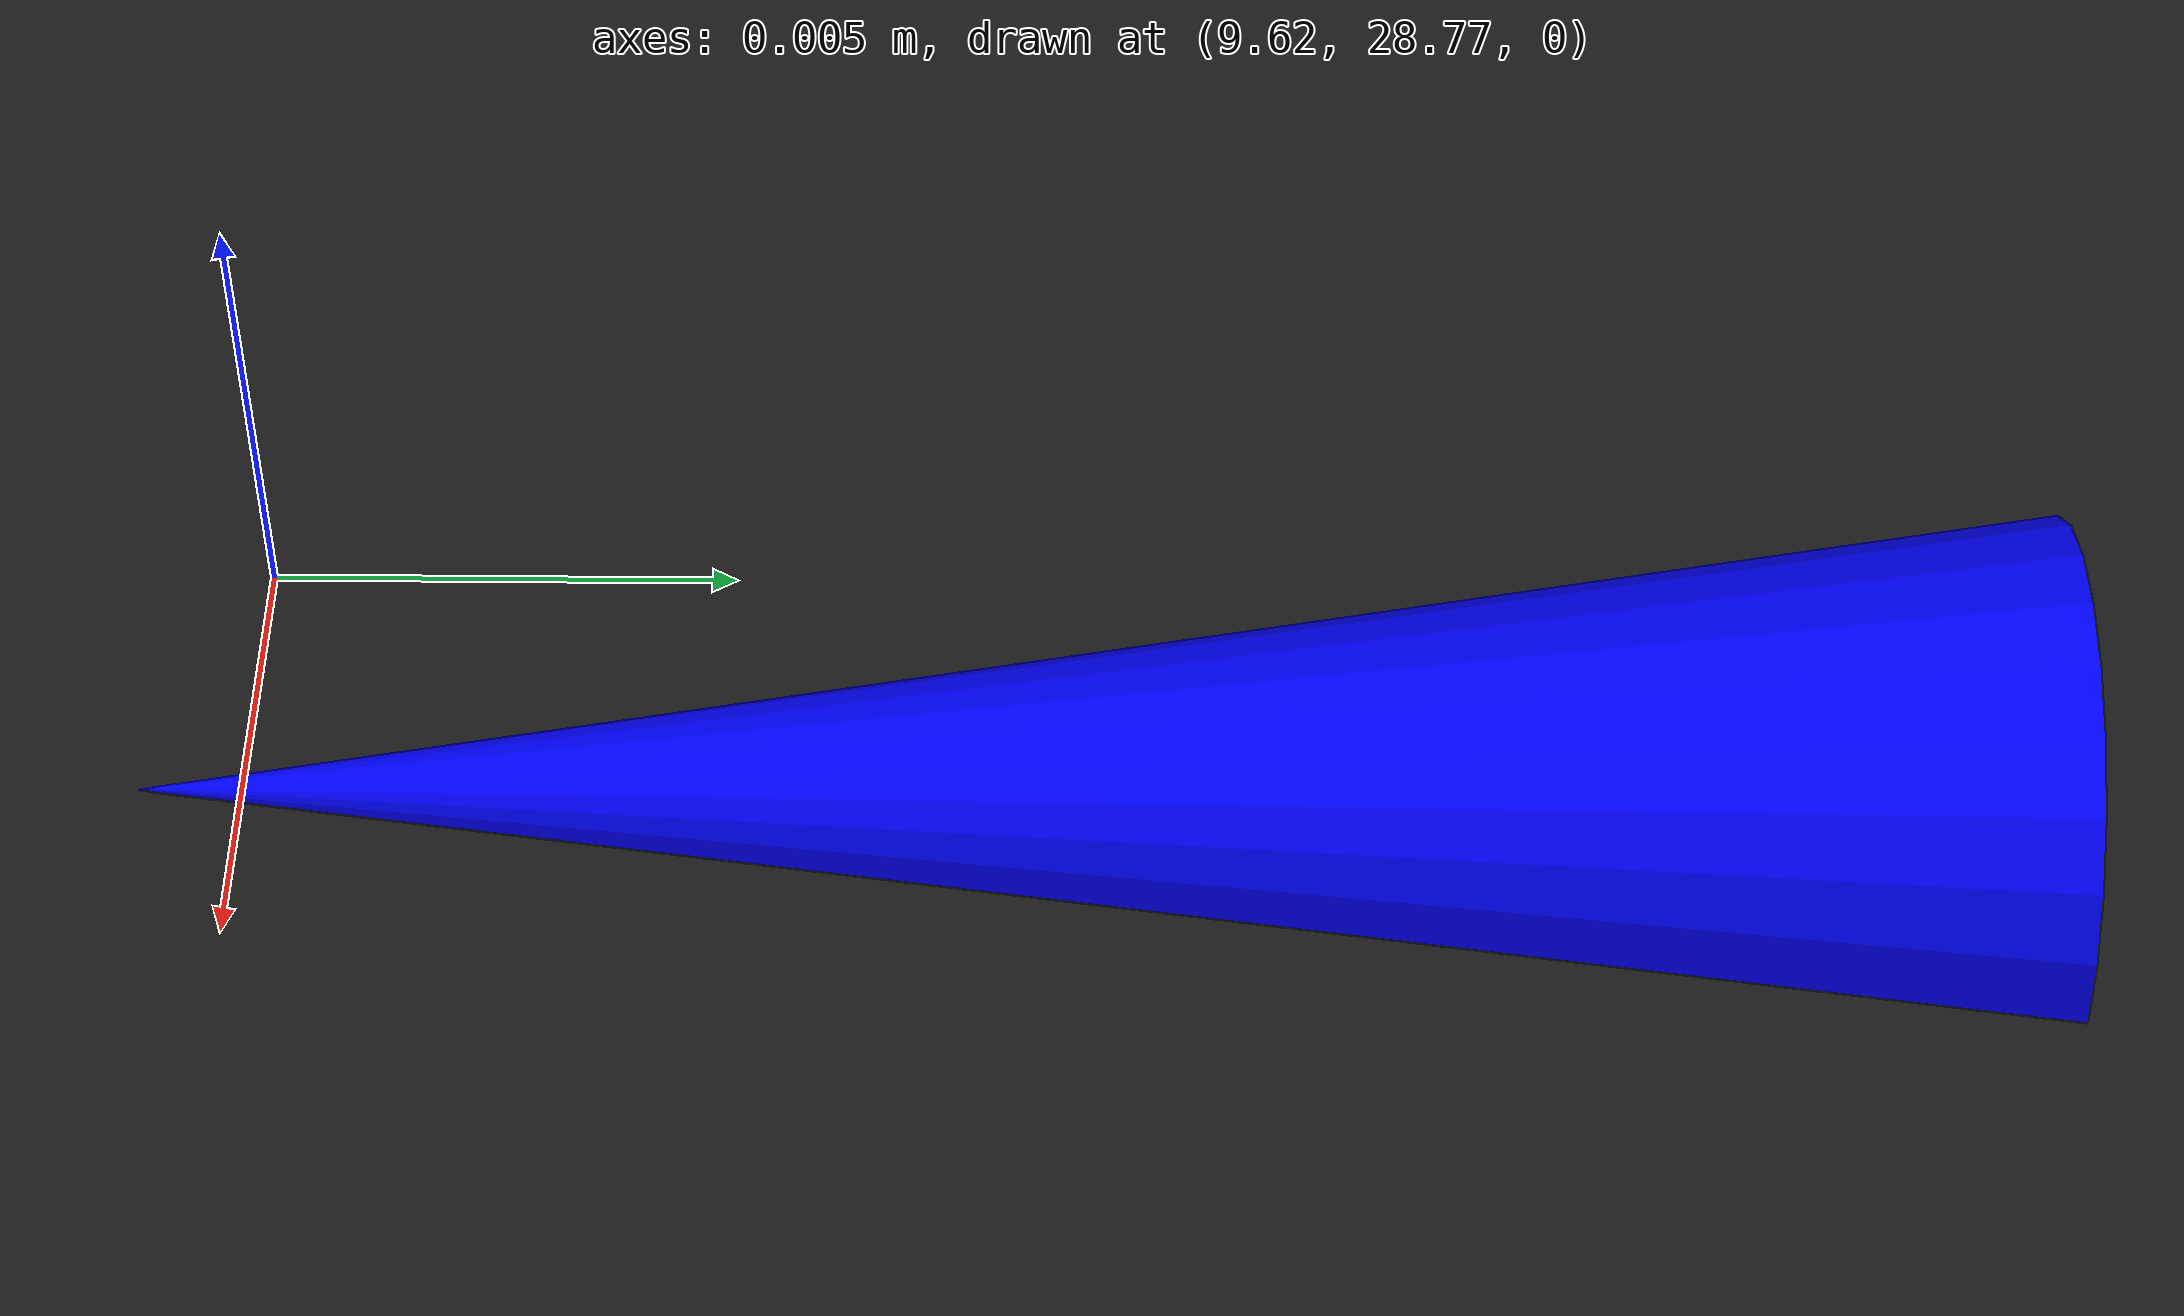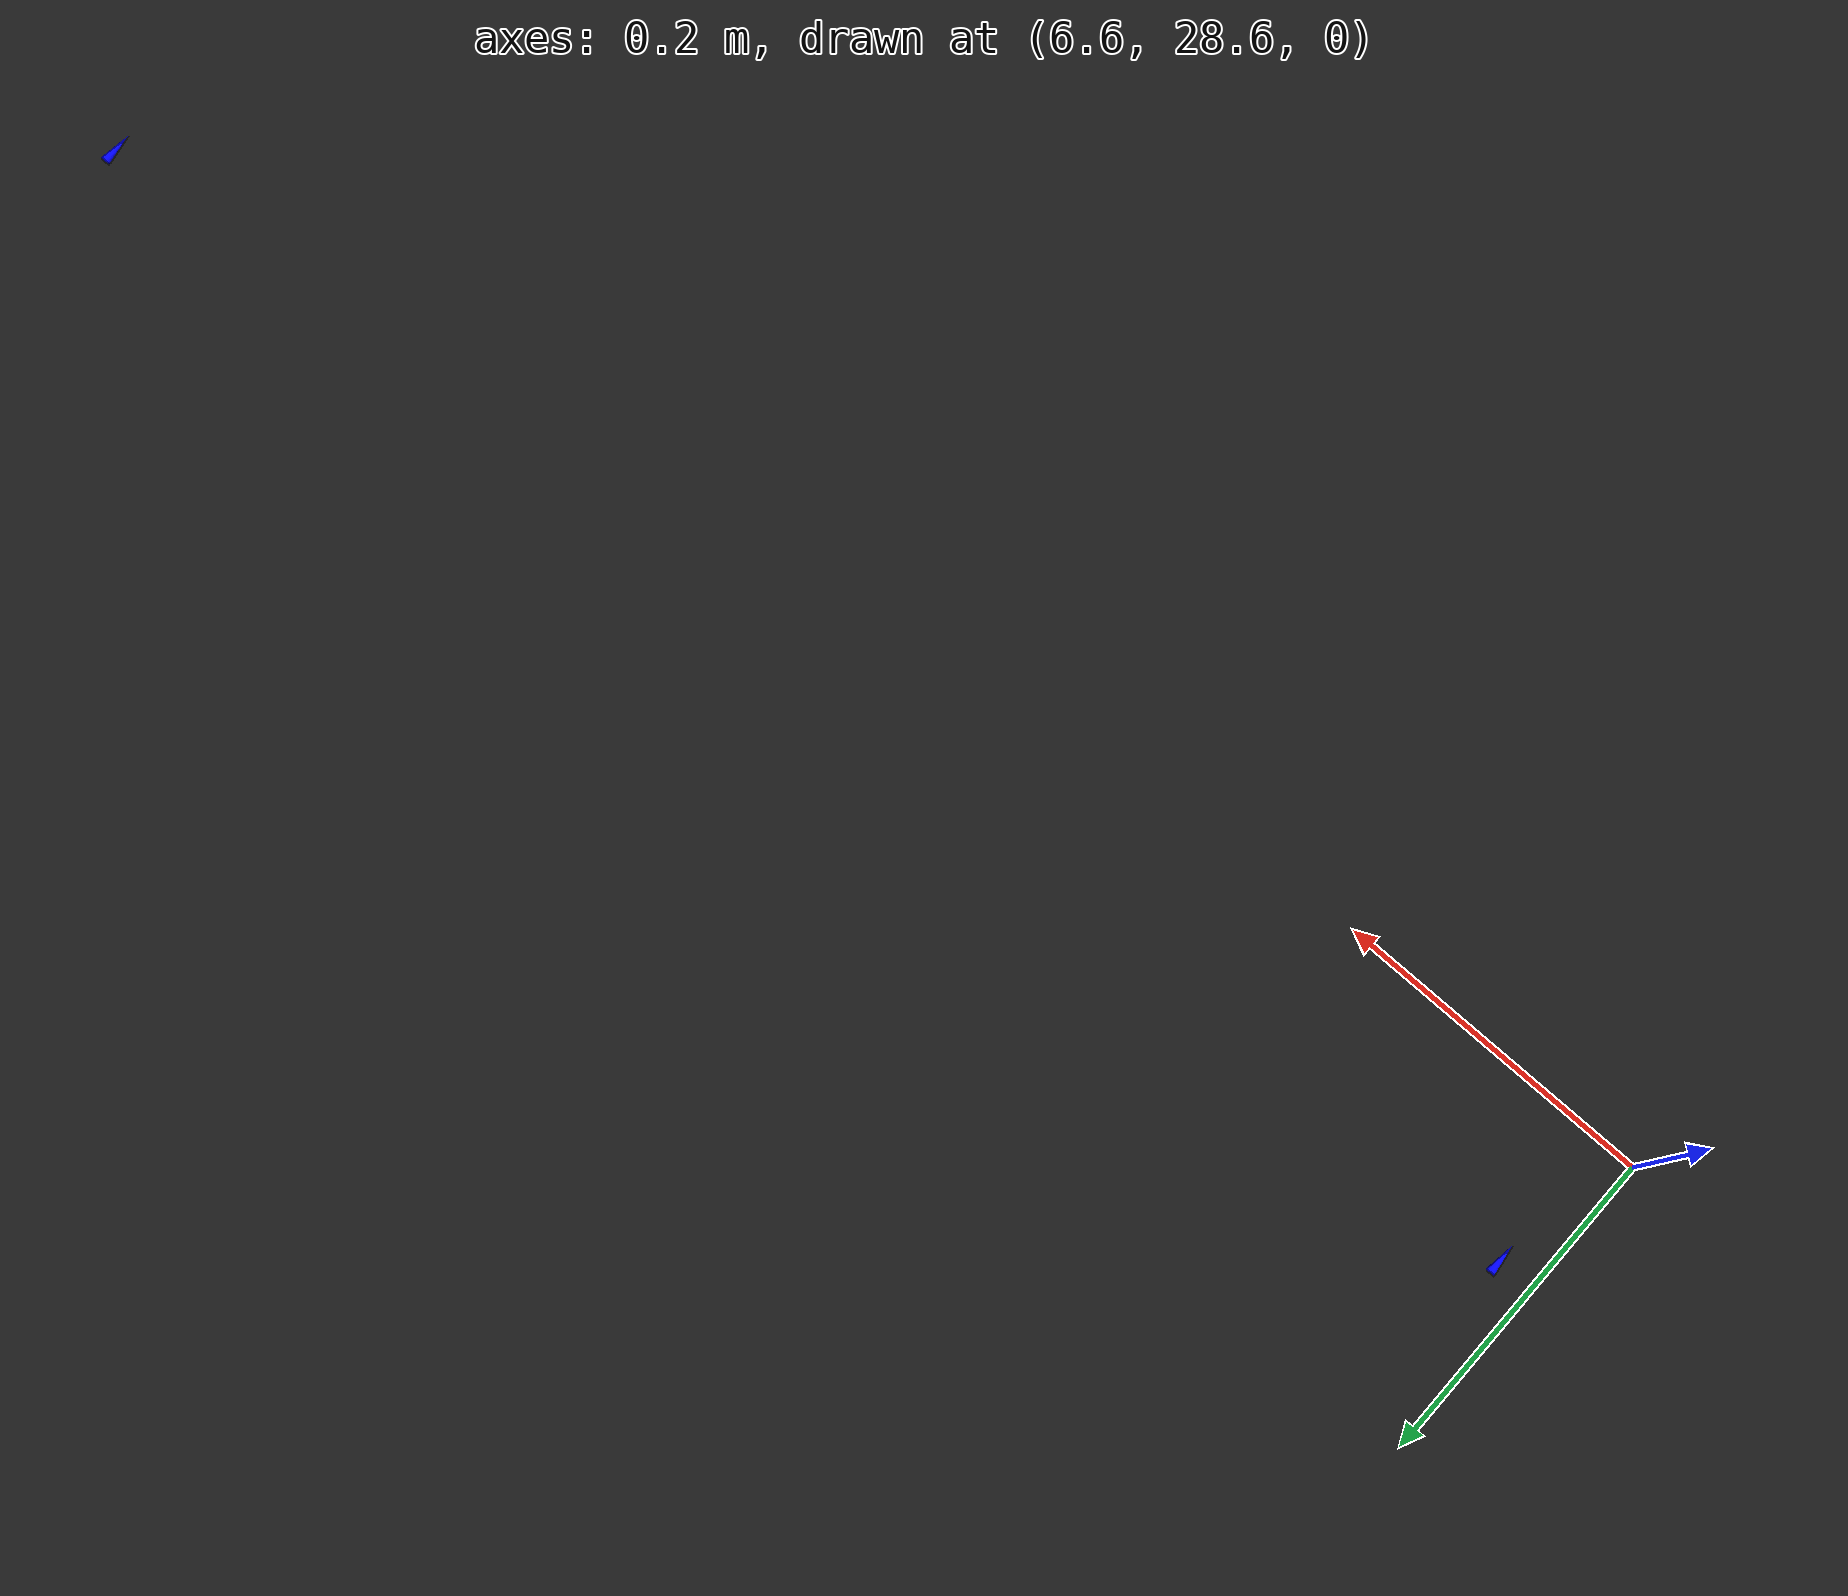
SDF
<sdf version="1.9">
	<world name="track">
		<physics name="1ms" type="ignored">
			<max_step_size>
				0.001
			</max_step_size>
			<real_time_factor>
				1.0
			</real_time_factor>
		</physics>
		<gravity>
			0 0 -9.8
		</gravity>
		<magnetic_field>
			6e-06 2.3e-05 -4.2e-05
		</magnetic_field>
		<atmosphere type="adiabatic" />
		<plugin name="gz::sim::systems::Physics" filename="gz-sim-physics-system" />
		<plugin name="gz::sim::systems::UserCommands" filename="gz-sim-user-commands-system" />
		<plugin name="gz::sim::systems::SceneBroadcaster" filename="gz-sim-scene-broadcaster-system" />
		<gui fullscreen="0">
			<plugin filename="MinimalScene" name="3D View">
				<gz-gui>
					<title>
						3D View
					</title>
					<property type="bool" key="showTitleBar">
						false
					</property>
					<property type="string" key="state">
						docked
					</property>
				</gz-gui>
				<engine>
					ogre2
				</engine>
				<scene>
					scene
				</scene>
				<ambient_light>
					0.4 0.4 0.4
				</ambient_light>
				<background_color>
					0.8 0.8 0.8
				</background_color>
				<camera_pose>
					-6 0 6 0 0.5 0
				</camera_pose>
			</plugin>
			<plugin filename="EntityContextMenuPlugin" name="Entity context menu">
				<gz-gui>
					<property key="state" type="string">
						floating
					</property>
					<property key="width" type="double">
						5
					</property>
					<property key="height" type="double">
						5
					</property>
					<property key="showTitleBar" type="bool">
						false
					</property>
				</gz-gui>
			</plugin>
			<plugin filename="GzSceneManager" name="Scene Manager">
				<gz-gui>
					<property key="resizable" type="bool">
						false
					</property>
					<property key="width" type="double">
						5
					</property>
					<property key="height" type="double">
						5
					</property>
					<property key="state" type="string">
						floating
					</property>
					<property key="showTitleBar" type="bool">
						false
					</property>
				</gz-gui>
			</plugin>
			<plugin filename="InteractiveViewControl" name="Interactive view control">
				<gz-gui>
					<property key="resizable" type="bool">
						false
					</property>
					<property key="width" type="double">
						5
					</property>
					<property key="height" type="double">
						5
					</property>
					<property key="state" type="string">
						floating
					</property>
					<property key="showTitleBar" type="bool">
						false
					</property>
				</gz-gui>
			</plugin>
			<plugin filename="CameraTracking" name="Camera Tracking">
				<gz-gui>
					<property key="resizable" type="bool">
						false
					</property>
					<property key="width" type="double">
						5
					</property>
					<property key="height" type="double">
						5
					</property>
					<property key="state" type="string">
						floating
					</property>
					<property key="showTitleBar" type="bool">
						false
					</property>
				</gz-gui>
			</plugin>
			<plugin name="World control" filename="WorldControl">
				<gz-gui>
					<title>
						World control
					</title>
					<property type="bool" key="showTitleBar">
						0
					</property>
					<property type="bool" key="resizable">
						0
					</property>
					<property type="double" key="height">
						72
					</property>
					<property type="double" key="z">
						1
					</property>
					<property type="string" key="state">
						floating
					</property>
					<anchors target="3D View">
						<line own="left" target="left" />
						<line own="bottom" target="bottom" />
					</anchors>
				</gz-gui>
				<play_pause>
					1
				</play_pause>
				<step>
					1
				</step>
				<start_paused>
					1
				</start_paused>
			</plugin>
			<plugin name="World stats" filename="WorldStats">
				<gz-gui>
					<title>
						World stats
					</title>
					<property type="bool" key="showTitleBar">
						0
					</property>
					<property type="bool" key="resizable">
						0
					</property>
					<property type="double" key="height">
						110
					</property>
					<property type="double" key="width">
						290
					</property>
					<property type="double" key="z">
						1
					</property>
					<property type="string" key="state">
						floating
					</property>
					<anchors target="3D View">
						<line own="right" target="right" />
						<line own="bottom" target="bottom" />
					</anchors>
				</gz-gui>
				<sim_time>
					1
				</sim_time>
				<real_time>
					1
				</real_time>
				<real_time_factor>
					1
				</real_time_factor>
				<iterations>
					1
				</iterations>
			</plugin>
			<plugin filename="VisualizeLidar" name="Visualize Lidar">
			</plugin>
			<plugin filename="ImageDisplay" name="Image Display">
			</plugin>
			<plugin filename="ComponentInspector" name="Component inspector">
				<ignition-gui>
					<property type="string" key="state">
						docked
					</property>
				</ignition-gui>
			</plugin>
			<plugin filename="EntityTree" name="Entity tree">
				<ignition-gui>
					<property type="string" key="state">
						docked
					</property>
				</ignition-gui>
			</plugin>
		</gui>
		<plugin filename="gz-sim-sensors-system" name="gz::sim::systems::Sensors">
			<render_engine>
				ogre2
			</render_engine>
		</plugin>
		<scene>
			<ambient>
				1 1 1 1
			</ambient>
			<background>
				0.8 0.8 0.8 1
			</background>
			<shadows>
				1
			</shadows>
		</scene>
		<light name="sun" type="directional">
			<cast_shadows>
				1
			</cast_shadows>
			<pose>
				0 0 10 0 0 0
			</pose>
			<diffuse>
				0.8 0.8 0.8 1
			</diffuse>
			<specular>
				0.8 0.8 0.8 1
			</specular>
			<attenuation>
				<range>
					1000
				</range>
				<constant>
					0.9
				</constant>
				<linear>
					0.01
				</linear>
				<quadratic>
					0.001
				</quadratic>
			</attenuation>
			<direction>
				-0.5 0.1 -0.9
			</direction>
		</light>
		<model name="ground_plane">
			<static>
				true
			</static>
			<link name="link">
				<collision name="collision">
					<geometry>
						<plane>
							<normal>
								0 0 1
							</normal>
							<size>
								100 100
							</size>
						</plane>
					</geometry>
					<surface>
						<friction>
							<dart />
						</friction>
						<bounce />
						<contact />
					</surface>
				</collision>
				<visual name="visual">
					<geometry>
						<plane>
							<normal>
								0 0 1
							</normal>
							<size>
								100 100
							</size>
						</plane>
					</geometry>
					<material>
						<ambient>
							0.1 0.1 0.1 1
						</ambient>
						<diffuse>
							0.1 0.1 0.1 1
						</diffuse>
						<specular>
							0.8 0.8 0.8 1
						</specular>
					</material>
				</visual>
				<pose>
					0 0 0 0 0 0
				</pose>
				<inertial>
					<pose>
						0 0 0 0 0.0 0
					</pose>
					<mass>
						1
					</mass>
					<inertia>
						<ixx>
							1
						</ixx>
						<ixy>
							0
						</ixy>
						<ixz>
							0
						</ixz>
						<iyy>
							1
						</iyy>
						<iyz>
							0
						</iyz>
						<izz>
							1
						</izz>
					</inertia>
				</inertial>
				<enable_wind>
					false
				</enable_wind>
			</link>
			<pose>
				0 0 0 0 0 0
			</pose>
			<self_collide>
				false
			</self_collide>
		</model>
		<model name="cones">
			<pose>
				0 0 0 0 0 0
			</pose>
			<link name="cone_0_link">
				<visual name="cone_0_visual">
					<geometry>
						<mesh>
							<uri>
								/home/ubuntu/psd_ws/src/psd_gazebo_sim/psd_gazebo_worlds/world/models/cone/meshes/cone.stl
							</uri>
							<scale>
								0.001 0.001 0.001
							</scale>
						</mesh>
					</geometry>
					<material>
						<ambient>
							1 1 0 1
						</ambient>
						<diffuse>
							1 1 0 1
						</diffuse>
						<specular>
							1 1 0 1
						</specular>
					</material>
				</visual>
				<pose>
					5.688073933774838 25.57597586423841 0.0 1.57 0 0
				</pose>
				<enable_wind>
					false
				</enable_wind>
			</link>
			<link name="cone_1_link">
				<visual name="cone_1_visual">
					<geometry>
						<mesh>
							<uri>
								/home/ubuntu/psd_ws/src/psd_gazebo_sim/psd_gazebo_worlds/world/models/cone/meshes/cone.stl
							</uri>
							<scale>
								0.001 0.001 0.001
							</scale>
						</mesh>
					</geometry>
					<material>
						<ambient>
							1 1 0 1
						</ambient>
						<diffuse>
							1 1 0 1
						</diffuse>
						<specular>
							1 1 0 1
						</specular>
					</material>
				</visual>
				<pose>
					6.686783433774838 25.60839286423841 0.0 1.57 0 0
				</pose>
				<enable_wind>
					false
				</enable_wind>
			</link>
			<link name="cone_2_link">
				<visual name="cone_2_visual">
					<geometry>
						<mesh>
							<uri>
								/home/ubuntu/psd_ws/src/psd_gazebo_sim/psd_gazebo_worlds/world/models/cone/meshes/cone.stl
							</uri>
							<scale>
								0.001 0.001 0.001
							</scale>
						</mesh>
					</geometry>
					<material>
						<ambient>
							1 1 0 1
						</ambient>
						<diffuse>
							1 1 0 1
						</diffuse>
						<specular>
							1 1 0 1
						</specular>
					</material>
				</visual>
				<pose>
					7.683275433774838 25.641048864238407 0.0 1.57 0 0
				</pose>
				<enable_wind>
					false
				</enable_wind>
			</link>
			<link name="cone_3_link">
				<visual name="cone_3_visual">
					<geometry>
						<mesh>
							<uri>
								/home/ubuntu/psd_ws/src/psd_gazebo_sim/psd_gazebo_worlds/world/models/cone/meshes/cone.stl
							</uri>
							<scale>
								0.001 0.001 0.001
							</scale>
						</mesh>
					</geometry>
					<material>
						<ambient>
							1 1 0 1
						</ambient>
						<diffuse>
							1 1 0 1
						</diffuse>
						<specular>
							1 1 0 1
						</specular>
					</material>
				</visual>
				<pose>
					8.677596433774838 25.67247836423841 0.0 1.57 0 0
				</pose>
				<enable_wind>
					false
				</enable_wind>
			</link>
			<link name="cone_4_link">
				<visual name="cone_4_visual">
					<geometry>
						<mesh>
							<uri>
								/home/ubuntu/psd_ws/src/psd_gazebo_sim/psd_gazebo_worlds/world/models/cone/meshes/cone.stl
							</uri>
							<scale>
								0.001 0.001 0.001
							</scale>
						</mesh>
					</geometry>
					<material>
						<ambient>
							1 1 0 1
						</ambient>
						<diffuse>
							1 1 0 1
						</diffuse>
						<specular>
							1 1 0 1
						</specular>
					</material>
				</visual>
				<pose>
					9.669788433774837 25.70122536423841 0.0 1.57 0 0
				</pose>
				<enable_wind>
					false
				</enable_wind>
			</link>
			<link name="cone_5_link">
				<visual name="cone_5_visual">
					<geometry>
						<mesh>
							<uri>
								/home/ubuntu/psd_ws/src/psd_gazebo_sim/psd_gazebo_worlds/world/models/cone/meshes/cone.stl
							</uri>
							<scale>
								0.001 0.001 0.001
							</scale>
						</mesh>
					</geometry>
					<material>
						<ambient>
							1 1 0 1
						</ambient>
						<diffuse>
							1 1 0 1
						</diffuse>
						<specular>
							1 1 0 1
						</specular>
					</material>
				</visual>
				<pose>
					10.659880933774836 25.72584286423841 0.0 1.57 0 0
				</pose>
				<enable_wind>
					false
				</enable_wind>
			</link>
			<link name="cone_6_link">
				<visual name="cone_6_visual">
					<geometry>
						<mesh>
							<uri>
								/home/ubuntu/psd_ws/src/psd_gazebo_sim/psd_gazebo_worlds/world/models/cone/meshes/cone.stl
							</uri>
							<scale>
								0.001 0.001 0.001
							</scale>
						</mesh>
					</geometry>
					<material>
						<ambient>
							1 1 0 1
						</ambient>
						<diffuse>
							1 1 0 1
						</diffuse>
						<specular>
							1 1 0 1
						</specular>
					</material>
				</visual>
				<pose>
					13.617552433774838 25.760592364238413 0.0 1.57 0 0
				</pose>
				<enable_wind>
					false
				</enable_wind>
			</link>
			<link name="cone_7_link">
				<visual name="cone_7_visual">
					<geometry>
						<mesh>
							<uri>
								/home/ubuntu/psd_ws/src/psd_gazebo_sim/psd_gazebo_worlds/world/models/cone/meshes/cone.stl
							</uri>
							<scale>
								0.001 0.001 0.001
							</scale>
						</mesh>
					</geometry>
					<material>
						<ambient>
							1 1 0 1
						</ambient>
						<diffuse>
							1 1 0 1
						</diffuse>
						<specular>
							1 1 0 1
						</specular>
					</material>
				</visual>
				<pose>
					14.59909143377484 25.754414864238413 0.0 1.57 0 0
				</pose>
				<enable_wind>
					false
				</enable_wind>
			</link>
			<link name="cone_8_link">
				<visual name="cone_8_visual">
					<geometry>
						<mesh>
							<uri>
								/home/ubuntu/psd_ws/src/psd_gazebo_sim/psd_gazebo_worlds/world/models/cone/meshes/cone.stl
							</uri>
							<scale>
								0.001 0.001 0.001
							</scale>
						</mesh>
					</geometry>
					<material>
						<ambient>
							1 1 0 1
						</ambient>
						<diffuse>
							1 1 0 1
						</diffuse>
						<specular>
							1 1 0 1
						</specular>
					</material>
				</visual>
				<pose>
					15.578284933774837 25.73701836423841 0.0 1.57 0 0
				</pose>
				<enable_wind>
					false
				</enable_wind>
			</link>
			<link name="cone_9_link">
				<visual name="cone_9_visual">
					<geometry>
						<mesh>
							<uri>
								/home/ubuntu/psd_ws/src/psd_gazebo_sim/psd_gazebo_worlds/world/models/cone/meshes/cone.stl
							</uri>
							<scale>
								0.001 0.001 0.001
							</scale>
						</mesh>
					</geometry>
					<material>
						<ambient>
							1 1 0 1
						</ambient>
						<diffuse>
							1 1 0 1
						</diffuse>
						<specular>
							1 1 0 1
						</specular>
					</material>
				</visual>
				<pose>
					16.554961433774835 25.707018364238408 0.0 1.57 0 0
				</pose>
				<enable_wind>
					false
				</enable_wind>
			</link>
			<link name="cone_10_link">
				<visual name="cone_10_visual">
					<geometry>
						<mesh>
							<uri>
								/home/ubuntu/psd_ws/src/psd_gazebo_sim/psd_gazebo_worlds/world/models/cone/meshes/cone.stl
							</uri>
							<scale>
								0.001 0.001 0.001
							</scale>
						</mesh>
					</geometry>
					<material>
						<ambient>
							1 1 0 1
						</ambient>
						<diffuse>
							1 1 0 1
						</diffuse>
						<specular>
							1 1 0 1
						</specular>
					</material>
				</visual>
				<pose>
					17.528895433774835 25.663042364238407 0.0 1.57 0 0
				</pose>
				<enable_wind>
					false
				</enable_wind>
			</link>
			<link name="cone_11_link">
				<visual name="cone_11_visual">
					<geometry>
						<mesh>
							<uri>
								/home/ubuntu/psd_ws/src/psd_gazebo_sim/psd_gazebo_worlds/world/models/cone/meshes/cone.stl
							</uri>
							<scale>
								0.001 0.001 0.001
							</scale>
						</mesh>
					</geometry>
					<material>
						<ambient>
							1 1 0 1
						</ambient>
						<diffuse>
							1 1 0 1
						</diffuse>
						<specular>
							1 1 0 1
						</specular>
					</material>
				</visual>
				<pose>
					18.480635433774836 25.60132436423841 0.0 1.57 0 0
				</pose>
				<enable_wind>
					false
				</enable_wind>
			</link>
			<link name="cone_12_link">
				<visual name="cone_12_visual">
					<geometry>
						<mesh>
							<uri>
								/home/ubuntu/psd_ws/src/psd_gazebo_sim/psd_gazebo_worlds/world/models/cone/meshes/cone.stl
							</uri>
							<scale>
								0.001 0.001 0.001
							</scale>
						</mesh>
					</geometry>
					<material>
						<ambient>
							1 1 0 1
						</ambient>
						<diffuse>
							1 1 0 1
						</diffuse>
						<specular>
							1 1 0 1
						</specular>
					</material>
				</visual>
				<pose>
					19.381697933774838 25.50222886423841 0.0 1.57 0 0
				</pose>
				<enable_wind>
					false
				</enable_wind>
			</link>
			<link name="cone_13_link">
				<visual name="cone_13_visual">
					<geometry>
						<mesh>
							<uri>
								/home/ubuntu/psd_ws/src/psd_gazebo_sim/psd_gazebo_worlds/world/models/cone/meshes/cone.stl
							</uri>
							<scale>
								0.001 0.001 0.001
							</scale>
						</mesh>
					</geometry>
					<material>
						<ambient>
							1 1 0 1
						</ambient>
						<diffuse>
							1 1 0 1
						</diffuse>
						<specular>
							1 1 0 1
						</specular>
					</material>
				</visual>
				<pose>
					21.00274043377484 25.108634364238412 0.0 1.57 0 0
				</pose>
				<enable_wind>
					false
				</enable_wind>
			</link>
			<link name="cone_14_link">
				<visual name="cone_14_visual">
					<geometry>
						<mesh>
							<uri>
								/home/ubuntu/psd_ws/src/psd_gazebo_sim/psd_gazebo_worlds/world/models/cone/meshes/cone.stl
							</uri>
							<scale>
								0.001 0.001 0.001
							</scale>
						</mesh>
					</geometry>
					<material>
						<ambient>
							1 1 0 1
						</ambient>
						<diffuse>
							1 1 0 1
						</diffuse>
						<specular>
							1 1 0 1
						</specular>
					</material>
				</visual>
				<pose>
					21.69623793377484 24.78811186423841 0.0 1.57 0 0
				</pose>
				<enable_wind>
					false
				</enable_wind>
			</link>
			<link name="cone_15_link">
				<visual name="cone_15_visual">
					<geometry>
						<mesh>
							<uri>
								/home/ubuntu/psd_ws/src/psd_gazebo_sim/psd_gazebo_worlds/world/models/cone/meshes/cone.stl
							</uri>
							<scale>
								0.001 0.001 0.001
							</scale>
						</mesh>
					</geometry>
					<material>
						<ambient>
							1 1 0 1
						</ambient>
						<diffuse>
							1 1 0 1
						</diffuse>
						<specular>
							1 1 0 1
						</specular>
					</material>
				</visual>
				<pose>
					22.815745433774836 23.855563864238412 0.0 1.57 0 0
				</pose>
				<enable_wind>
					false
				</enable_wind>
			</link>
			<link name="cone_16_link">
				<visual name="cone_16_visual">
					<geometry>
						<mesh>
							<uri>
								/home/ubuntu/psd_ws/src/psd_gazebo_sim/psd_gazebo_worlds/world/models/cone/meshes/cone.stl
							</uri>
							<scale>
								0.001 0.001 0.001
							</scale>
						</mesh>
					</geometry>
					<material>
						<ambient>
							1 1 0 1
						</ambient>
						<diffuse>
							1 1 0 1
						</diffuse>
						<specular>
							1 1 0 1
						</specular>
					</material>
				</visual>
				<pose>
					23.26223843377484 23.23515736423841 0.0 1.57 0 0
				</pose>
				<enable_wind>
					false
				</enable_wind>
			</link>
			<link name="cone_17_link">
				<visual name="cone_17_visual">
					<geometry>
						<mesh>
							<uri>
								/home/ubuntu/psd_ws/src/psd_gazebo_sim/psd_gazebo_worlds/world/models/cone/meshes/cone.stl
							</uri>
							<scale>
								0.001 0.001 0.001
							</scale>
						</mesh>
					</geometry>
					<material>
						<ambient>
							1 1 0 1
						</ambient>
						<diffuse>
							1 1 0 1
						</diffuse>
						<specular>
							1 1 0 1
						</specular>
					</material>
				</visual>
				<pose>
					23.625085433774842 22.533576864238412 0.0 1.57 0 0
				</pose>
				<enable_wind>
					false
				</enable_wind>
			</link>
			<link name="cone_18_link">
				<visual name="cone_18_visual">
					<geometry>
						<mesh>
							<uri>
								/home/ubuntu/psd_ws/src/psd_gazebo_sim/psd_gazebo_worlds/world/models/cone/meshes/cone.stl
							</uri>
							<scale>
								0.001 0.001 0.001
							</scale>
						</mesh>
					</geometry>
					<material>
						<ambient>
							1 1 0 1
						</ambient>
						<diffuse>
							1 1 0 1
						</diffuse>
						<specular>
							1 1 0 1
						</specular>
					</material>
				</visual>
				<pose>
					23.90270843377484 21.767563364238413 0.0 1.57 0 0
				</pose>
				<enable_wind>
					false
				</enable_wind>
			</link>
			<link name="cone_19_link">
				<visual name="cone_19_visual">
					<geometry>
						<mesh>
							<uri>
								/home/ubuntu/psd_ws/src/psd_gazebo_sim/psd_gazebo_worlds/world/models/cone/meshes/cone.stl
							</uri>
							<scale>
								0.001 0.001 0.001
							</scale>
						</mesh>
					</geometry>
					<material>
						<ambient>
							1 1 0 1
						</ambient>
						<diffuse>
							1 1 0 1
						</diffuse>
						<specular>
							1 1 0 1
						</specular>
					</material>
				</visual>
				<pose>
					24.168956933774837 20.17743936423841 0.0 1.57 0 0
				</pose>
				<enable_wind>
					false
				</enable_wind>
			</link>
			<link name="cone_20_link">
				<visual name="cone_20_visual">
					<geometry>
						<mesh>
							<uri>
								/home/ubuntu/psd_ws/src/psd_gazebo_sim/psd_gazebo_worlds/world/models/cone/meshes/cone.stl
							</uri>
							<scale>
								0.001 0.001 0.001
							</scale>
						</mesh>
					</geometry>
					<material>
						<ambient>
							1 1 0 1
						</ambient>
						<diffuse>
							1 1 0 1
						</diffuse>
						<specular>
							1 1 0 1
						</specular>
					</material>
				</visual>
				<pose>
					24.14292943377484 19.390641364238405 0.0 1.57 0 0
				</pose>
				<enable_wind>
					false
				</enable_wind>
			</link>
			<link name="cone_21_link">
				<visual name="cone_21_visual">
					<geometry>
						<mesh>
							<uri>
								/home/ubuntu/psd_ws/src/psd_gazebo_sim/psd_gazebo_worlds/world/models/cone/meshes/cone.stl
							</uri>
							<scale>
								0.001 0.001 0.001
							</scale>
						</mesh>
					</geometry>
					<material>
						<ambient>
							1 1 0 1
						</ambient>
						<diffuse>
							1 1 0 1
						</diffuse>
						<specular>
							1 1 0 1
						</specular>
					</material>
				</visual>
				<pose>
					24.006382933774837 18.629237364238406 0.0 1.57 0 0
				</pose>
				<enable_wind>
					false
				</enable_wind>
			</link>
			<link name="cone_22_link">
				<visual name="cone_22_visual">
					<geometry>
						<mesh>
							<uri>
								/home/ubuntu/psd_ws/src/psd_gazebo_sim/psd_gazebo_worlds/world/models/cone/meshes/cone.stl
							</uri>
							<scale>
								0.001 0.001 0.001
							</scale>
						</mesh>
					</geometry>
					<material>
						<ambient>
							1 1 0 1
						</ambient>
						<diffuse>
							1 1 0 1
						</diffuse>
						<specular>
							1 1 0 1
						</specular>
					</material>
				</visual>
				<pose>
					23.759506933774837 17.91058686423841 0.0 1.57 0 0
				</pose>
				<enable_wind>
					false
				</enable_wind>
			</link>
			<link name="cone_23_link">
				<visual name="cone_23_visual">
					<geometry>
						<mesh>
							<uri>
								/home/ubuntu/psd_ws/src/psd_gazebo_sim/psd_gazebo_worlds/world/models/cone/meshes/cone.stl
							</uri>
							<scale>
								0.001 0.001 0.001
							</scale>
						</mesh>
					</geometry>
					<material>
						<ambient>
							1 1 0 1
						</ambient>
						<diffuse>
							1 1 0 1
						</diffuse>
						<specular>
							1 1 0 1
						</specular>
					</material>
				</visual>
				<pose>
					23.40151843377484 17.24270186423841 0.0 1.57 0 0
				</pose>
				<enable_wind>
					false
				</enable_wind>
			</link>
			<link name="cone_24_link">
				<visual name="cone_24_visual">
					<geometry>
						<mesh>
							<uri>
								/home/ubuntu/psd_ws/src/psd_gazebo_sim/psd_gazebo_worlds/world/models/cone/meshes/cone.stl
							</uri>
							<scale>
								0.001 0.001 0.001
							</scale>
						</mesh>
					</geometry>
					<material>
						<ambient>
							1 1 0 1
						</ambient>
						<diffuse>
							1 1 0 1
						</diffuse>
						<specular>
							1 1 0 1
						</specular>
					</material>
				</visual>
				<pose>
					22.365507433774837 16.04319436423841 0.0 1.57 0 0
				</pose>
				<enable_wind>
					false
				</enable_wind>
			</link>
			<link name="cone_25_link">
				<visual name="cone_25_visual">
					<geometry>
						<mesh>
							<uri>
								/home/ubuntu/psd_ws/src/psd_gazebo_sim/psd_gazebo_worlds/world/models/cone/meshes/cone.stl
							</uri>
							<scale>
								0.001 0.001 0.001
							</scale>
						</mesh>
					</geometry>
					<material>
						<ambient>
							1 1 0 1
						</ambient>
						<diffuse>
							1 1 0 1
						</diffuse>
						<specular>
							1 1 0 1
						</specular>
					</material>
				</visual>
				<pose>
					21.007376433774837 15.072803364238407 0.0 1.57 0 0
				</pose>
				<enable_wind>
					false
				</enable_wind>
			</link>
			<link name="cone_26_link">
				<visual name="cone_26_visual">
					<geometry>
						<mesh>
							<uri>
								/home/ubuntu/psd_ws/src/psd_gazebo_sim/psd_gazebo_worlds/world/models/cone/meshes/cone.stl
							</uri>
							<scale>
								0.001 0.001 0.001
							</scale>
						</mesh>
					</geometry>
					<material>
						<ambient>
							1 1 0 1
						</ambient>
						<diffuse>
							1 1 0 1
						</diffuse>
						<specular>
							1 1 0 1
						</specular>
					</material>
				</visual>
				<pose>
					20.26277543377484 14.703898364238409 0.0 1.57 0 0
				</pose>
				<enable_wind>
					false
				</enable_wind>
			</link>
			<link name="cone_27_link">
				<visual name="cone_27_visual">
					<geometry>
						<mesh>
							<uri>
								/home/ubuntu/psd_ws/src/psd_gazebo_sim/psd_gazebo_worlds/world/models/cone/meshes/cone.stl
							</uri>
							<scale>
								0.001 0.001 0.001
							</scale>
						</mesh>
					</geometry>
					<material>
						<ambient>
							1 1 0 1
						</ambient>
						<diffuse>
							1 1 0 1
						</diffuse>
						<specular>
							1 1 0 1
						</specular>
					</material>
				</visual>
				<pose>
					19.489347933774837 14.42485286423841 0.0 1.57 0 0
				</pose>
				<enable_wind>
					false
				</enable_wind>
			</link>
			<link name="cone_28_link">
				<visual name="cone_28_visual">
					<geometry>
						<mesh>
							<uri>
								/home/ubuntu/psd_ws/src/psd_gazebo_sim/psd_gazebo_worlds/world/models/cone/meshes/cone.stl
							</uri>
							<scale>
								0.001 0.001 0.001
							</scale>
						</mesh>
					</geometry>
					<material>
						<ambient>
							1 1 0 1
						</ambient>
						<diffuse>
							1 1 0 1
						</diffuse>
						<specular>
							1 1 0 1
						</specular>
					</material>
				</visual>
				<pose>
					18.69668843377484 14.242005364238409 0.0 1.57 0 0
				</pose>
				<enable_wind>
					false
				</enable_wind>
			</link>
			<link name="cone_29_link">
				<visual name="cone_29_visual">
					<geometry>
						<mesh>
							<uri>
								/home/ubuntu/psd_ws/src/psd_gazebo_sim/psd_gazebo_worlds/world/models/cone/meshes/cone.stl
							</uri>
							<scale>
								0.001 0.001 0.001
							</scale>
						</mesh>
					</geometry>
					<material>
						<ambient>
							1 1 0 1
						</ambient>
						<diffuse>
							1 1 0 1
						</diffuse>
						<specular>
							1 1 0 1
						</specular>
					</material>
				</visual>
				<pose>
					17.896095933774838 14.16057736423841 0.0 1.57 0 0
				</pose>
				<enable_wind>
					false
				</enable_wind>
			</link>
			<link name="cone_30_link">
				<visual name="cone_30_visual">
					<geometry>
						<mesh>
							<uri>
								/home/ubuntu/psd_ws/src/psd_gazebo_sim/psd_gazebo_worlds/world/models/cone/meshes/cone.stl
							</uri>
							<scale>
								0.001 0.001 0.001
							</scale>
						</mesh>
					</geometry>
					<material>
						<ambient>
							1 1 0 1
						</ambient>
						<diffuse>
							1 1 0 1
						</diffuse>
						<specular>
							1 1 0 1
						</specular>
					</material>
				</visual>
				<pose>
					17.093347933774837 14.183804864238407 0.0 1.57 0 0
				</pose>
				<enable_wind>
					false
				</enable_wind>
			</link>
			<link name="cone_31_link">
				<visual name="cone_31_visual">
					<geometry>
						<mesh>
							<uri>
								/home/ubuntu/psd_ws/src/psd_gazebo_sim/psd_gazebo_worlds/world/models/cone/meshes/cone.stl
							</uri>
							<scale>
								0.001 0.001 0.001
							</scale>
						</mesh>
					</geometry>
					<material>
						<ambient>
							1 1 0 1
						</ambient>
						<diffuse>
							1 1 0 1
						</diffuse>
						<specular>
							1 1 0 1
						</specular>
					</material>
				</visual>
				<pose>
					16.283429433774835 14.30878436423841 0.0 1.57 0 0
				</pose>
				<enable_wind>
					false
				</enable_wind>
			</link>
			<link name="cone_32_link">
				<visual name="cone_32_visual">
					<geometry>
						<mesh>
							<uri>
								/home/ubuntu/psd_ws/src/psd_gazebo_sim/psd_gazebo_worlds/world/models/cone/meshes/cone.stl
							</uri>
							<scale>
								0.001 0.001 0.001
							</scale>
						</mesh>
					</geometry>
					<material>
						<ambient>
							1 1 0 1
						</ambient>
						<diffuse>
							1 1 0 1
						</diffuse>
						<specular>
							1 1 0 1
						</specular>
					</material>
				</visual>
				<pose>
					14.678793433774837 14.83505986423841 0.0 1.57 0 0
				</pose>
				<enable_wind>
					false
				</enable_wind>
			</link>
			<link name="cone_33_link">
				<visual name="cone_33_visual">
					<geometry>
						<mesh>
							<uri>
								/home/ubuntu/psd_ws/src/psd_gazebo_sim/psd_gazebo_worlds/world/models/cone/meshes/cone.stl
							</uri>
							<scale>
								0.001 0.001 0.001
							</scale>
						</mesh>
					</geometry>
					<material>
						<ambient>
							1 1 0 1
						</ambient>
						<diffuse>
							1 1 0 1
						</diffuse>
						<specular>
							1 1 0 1
						</specular>
					</material>
				</visual>
				<pose>
					13.12512243377484 15.67540736423841 0.0 1.57 0 0
				</pose>
				<enable_wind>
					false
				</enable_wind>
			</link>
			<link name="cone_34_link">
				<visual name="cone_34_visual">
					<geometry>
						<mesh>
							<uri>
								/home/ubuntu/psd_ws/src/psd_gazebo_sim/psd_gazebo_worlds/world/models/cone/meshes/cone.stl
							</uri>
							<scale>
								0.001 0.001 0.001
							</scale>
						</mesh>
					</geometry>
					<material>
						<ambient>
							1 1 0 1
						</ambient>
						<diffuse>
							1 1 0 1
						</diffuse>
						<specular>
							1 1 0 1
						</specular>
					</material>
				</visual>
				<pose>
					12.344447433774839 16.19527936423841 0.0 1.57 0 0
				</pose>
				<enable_wind>
					false
				</enable_wind>
			</link>
			<link name="cone_35_link">
				<visual name="cone_35_visual">
					<geometry>
						<mesh>
							<uri>
								/home/ubuntu/psd_ws/src/psd_gazebo_sim/psd_gazebo_worlds/world/models/cone/meshes/cone.stl
							</uri>
							<scale>
								0.001 0.001 0.001
							</scale>
						</mesh>
					</geometry>
					<material>
						<ambient>
							1 1 0 1
						</ambient>
						<diffuse>
							1 1 0 1
						</diffuse>
						<specular>
							1 1 0 1
						</specular>
					</material>
				</visual>
				<pose>
					11.542868933774837 16.75925436423841 0.0 1.57 0 0
				</pose>
				<enable_wind>
					false
				</enable_wind>
			</link>
			<link name="cone_36_link">
				<visual name="cone_36_visual">
					<geometry>
						<mesh>
							<uri>
								/home/ubuntu/psd_ws/src/psd_gazebo_sim/psd_gazebo_worlds/world/models/cone/meshes/cone.stl
							</uri>
							<scale>
								0.001 0.001 0.001
							</scale>
						</mesh>
					</geometry>
					<material>
						<ambient>
							1 1 0 1
						</ambient>
						<diffuse>
							1 1 0 1
						</diffuse>
						<specular>
							1 1 0 1
						</specular>
					</material>
				</visual>
				<pose>
					10.705428933774837 17.34542386423841 0.0 1.57 0 0
				</pose>
				<enable_wind>
					false
				</enable_wind>
			</link>
			<link name="cone_37_link">
				<visual name="cone_37_visual">
					<geometry>
						<mesh>
							<uri>
								/home/ubuntu/psd_ws/src/psd_gazebo_sim/psd_gazebo_worlds/world/models/cone/meshes/cone.stl
							</uri>
							<scale>
								0.001 0.001 0.001
							</scale>
						</mesh>
					</geometry>
					<material>
						<ambient>
							1 1 0 1
						</ambient>
						<diffuse>
							1 1 0 1
						</diffuse>
						<specular>
							1 1 0 1
						</specular>
					</material>
				</visual>
				<pose>
					9.815351933774838 17.92882986423841 0.0 1.57 0 0
				</pose>
				<enable_wind>
					false
				</enable_wind>
			</link>
			<link name="cone_38_link">
				<visual name="cone_38_visual">
					<geometry>
						<mesh>
							<uri>
								/home/ubuntu/psd_ws/src/psd_gazebo_sim/psd_gazebo_worlds/world/models/cone/meshes/cone.stl
							</uri>
							<scale>
								0.001 0.001 0.001
							</scale>
						</mesh>
					</geometry>
					<material>
						<ambient>
							1 1 0 1
						</ambient>
						<diffuse>
							1 1 0 1
						</diffuse>
						<specular>
							1 1 0 1
						</specular>
					</material>
				</visual>
				<pose>
					7.819146433774838 18.96266636423841 0.0 1.57 0 0
				</pose>
				<enable_wind>
					false
				</enable_wind>
			</link>
			<link name="cone_39_link">
				<visual name="cone_39_visual">
					<geometry>
						<mesh>
							<uri>
								/home/ubuntu/psd_ws/src/psd_gazebo_sim/psd_gazebo_worlds/world/models/cone/meshes/cone.stl
							</uri>
							<scale>
								0.001 0.001 0.001
							</scale>
						</mesh>
					</geometry>
					<material>
						<ambient>
							1 1 0 1
						</ambient>
						<diffuse>
							1 1 0 1
						</diffuse>
						<specular>
							1 1 0 1
						</specular>
					</material>
				</visual>
				<pose>
					6.736016433774838 19.340075864238408 0.0 1.57 0 0
				</pose>
				<enable_wind>
					false
				</enable_wind>
			</link>
			<link name="cone_40_link">
				<visual name="cone_40_visual">
					<geometry>
						<mesh>
							<uri>
								/home/ubuntu/psd_ws/src/psd_gazebo_sim/psd_gazebo_worlds/world/models/cone/meshes/cone.stl
							</uri>
							<scale>
								0.001 0.001 0.001
							</scale>
						</mesh>
					</geometry>
					<material>
						<ambient>
							1 1 0 1
						</ambient>
						<diffuse>
							1 1 0 1
						</diffuse>
						<specular>
							1 1 0 1
						</specular>
					</material>
				</visual>
				<pose>
					5.6256884337748385 19.60826686423841 0.0 1.57 0 0
				</pose>
				<enable_wind>
					false
				</enable_wind>
			</link>
			<link name="cone_41_link">
				<visual name="cone_41_visual">
					<geometry>
						<mesh>
							<uri>
								/home/ubuntu/psd_ws/src/psd_gazebo_sim/psd_gazebo_worlds/world/models/cone/meshes/cone.stl
							</uri>
							<scale>
								0.001 0.001 0.001
							</scale>
						</mesh>
					</geometry>
					<material>
						<ambient>
							1 1 0 1
						</ambient>
						<diffuse>
							1 1 0 1
						</diffuse>
						<specular>
							1 1 0 1
						</specular>
					</material>
				</visual>
				<pose>
					4.499605933774838 19.769138864238407 0.0 1.57 0 0
				</pose>
				<enable_wind>
					false
				</enable_wind>
			</link>
			<link name="cone_42_link">
				<visual name="cone_42_visual">
					<geometry>
						<mesh>
							<uri>
								/home/ubuntu/psd_ws/src/psd_gazebo_sim/psd_gazebo_worlds/world/models/cone/meshes/cone.stl
							</uri>
							<scale>
								0.001 0.001 0.001
							</scale>
						</mesh>
					</geometry>
					<material>
						<ambient>
							1 1 0 1
						</ambient>
						<diffuse>
							1 1 0 1
						</diffuse>
						<specular>
							1 1 0 1
						</specular>
					</material>
				</visual>
				<pose>
					2.237851433774838 19.78154936423841 0.0 1.57 0 0
				</pose>
				<enable_wind>
					false
				</enable_wind>
			</link>
			<link name="cone_43_link">
				<visual name="cone_43_visual">
					<geometry>
						<mesh>
							<uri>
								/home/ubuntu/psd_ws/src/psd_gazebo_sim/psd_gazebo_worlds/world/models/cone/meshes/cone.stl
							</uri>
							<scale>
								0.001 0.001 0.001
							</scale>
						</mesh>
					</geometry>
					<material>
						<ambient>
							1 1 0 1
						</ambient>
						<diffuse>
							1 1 0 1
						</diffuse>
						<specular>
							1 1 0 1
						</specular>
					</material>
				</visual>
				<pose>
					1.062135933774838 19.61069536423841 0.0 1.57 0 0
				</pose>
				<enable_wind>
					false
				</enable_wind>
			</link>
			<link name="cone_44_link">
				<visual name="cone_44_visual">
					<geometry>
						<mesh>
							<uri>
								/home/ubuntu/psd_ws/src/psd_gazebo_sim/psd_gazebo_worlds/world/models/cone/meshes/cone.stl
							</uri>
							<scale>
								0.001 0.001 0.001
							</scale>
						</mesh>
					</geometry>
					<material>
						<ambient>
							1 1 0 1
						</ambient>
						<diffuse>
							1 1 0 1
						</diffuse>
						<specular>
							1 1 0 1
						</specular>
					</material>
				</visual>
				<pose>
					-1.3243260662251615 18.588025364238412 0.0 1.57 0 0
				</pose>
				<enable_wind>
					false
				</enable_wind>
			</link>
			<link name="cone_45_link">
				<visual name="cone_45_visual">
					<geometry>
						<mesh>
							<uri>
								/home/ubuntu/psd_ws/src/psd_gazebo_sim/psd_gazebo_worlds/world/models/cone/meshes/cone.stl
							</uri>
							<scale>
								0.001 0.001 0.001
							</scale>
						</mesh>
					</geometry>
					<material>
						<ambient>
							1 1 0 1
						</ambient>
						<diffuse>
							1 1 0 1
						</diffuse>
						<specular>
							1 1 0 1
						</specular>
					</material>
				</visual>
				<pose>
					-2.338573566225162 17.62455036423841 0.0 1.57 0 0
				</pose>
				<enable_wind>
					false
				</enable_wind>
			</link>
			<link name="cone_46_link">
				<visual name="cone_46_visual">
					<geometry>
						<mesh>
							<uri>
								/home/ubuntu/psd_ws/src/psd_gazebo_sim/psd_gazebo_worlds/world/models/cone/meshes/cone.stl
							</uri>
							<scale>
								0.001 0.001 0.001
							</scale>
						</mesh>
					</geometry>
					<material>
						<ambient>
							1 1 0 1
						</ambient>
						<diffuse>
							1 1 0 1
						</diffuse>
						<specular>
							1 1 0 1
						</specular>
					</material>
				</visual>
				<pose>
					-3.057532566225162 16.428847364238408 0.0 1.57 0 0
				</pose>
				<enable_wind>
					false
				</enable_wind>
			</link>
			<link name="cone_47_link">
				<visual name="cone_47_visual">
					<geometry>
						<mesh>
							<uri>
								/home/ubuntu/psd_ws/src/psd_gazebo_sim/psd_gazebo_worlds/world/models/cone/meshes/cone.stl
							</uri>
							<scale>
								0.001 0.001 0.001
							</scale>
						</mesh>
					</geometry>
					<material>
						<ambient>
							1 1 0 1
						</ambient>
						<diffuse>
							1 1 0 1
						</diffuse>
						<specular>
							1 1 0 1
						</specular>
					</material>
				</visual>
				<pose>
					-3.4357090662251633 15.092927864238408 0.0 1.57 0 0
				</pose>
				<enable_wind>
					false
				</enable_wind>
			</link>
			<link name="cone_48_link">
				<visual name="cone_48_visual">
					<geometry>
						<mesh>
							<uri>
								/home/ubuntu/psd_ws/src/psd_gazebo_sim/psd_gazebo_worlds/world/models/cone/meshes/cone.stl
							</uri>
							<scale>
								0.001 0.001 0.001
							</scale>
						</mesh>
					</geometry>
					<material>
						<ambient>
							1 1 0 1
						</ambient>
						<diffuse>
							1 1 0 1
						</diffuse>
						<specular>
							1 1 0 1
						</specular>
					</material>
				</visual>
				<pose>
					-3.4564395662251624 13.71146436423841 0.0 1.57 0 0
				</pose>
				<enable_wind>
					false
				</enable_wind>
			</link>
			<link name="cone_49_link">
				<visual name="cone_49_visual">
					<geometry>
						<mesh>
							<uri>
								/home/ubuntu/psd_ws/src/psd_gazebo_sim/psd_gazebo_worlds/world/models/cone/meshes/cone.stl
							</uri>
							<scale>
								0.001 0.001 0.001
							</scale>
						</mesh>
					</geometry>
					<material>
						<ambient>
							1 1 0 1
						</ambient>
						<diffuse>
							1 1 0 1
						</diffuse>
						<specular>
							1 1 0 1
						</specular>
					</material>
				</visual>
				<pose>
					-3.1280155662251623 12.37644986423841 0.0 1.57 0 0
				</pose>
				<enable_wind>
					false
				</enable_wind>
			</link>
			<link name="cone_50_link">
				<visual name="cone_50_visual">
					<geometry>
						<mesh>
							<uri>
								/home/ubuntu/psd_ws/src/psd_gazebo_sim/psd_gazebo_worlds/world/models/cone/meshes/cone.stl
							</uri>
							<scale>
								0.001 0.001 0.001
							</scale>
						</mesh>
					</geometry>
					<material>
						<ambient>
							1 1 0 1
						</ambient>
						<diffuse>
							1 1 0 1
						</diffuse>
						<specular>
							1 1 0 1
						</specular>
					</material>
				</visual>
				<pose>
					-2.4808110662251623 11.171215864238409 0.0 1.57 0 0
				</pose>
				<enable_wind>
					false
				</enable_wind>
			</link>
			<link name="cone_51_link">
				<visual name="cone_51_visual">
					<geometry>
						<mesh>
							<uri>
								/home/ubuntu/psd_ws/src/psd_gazebo_sim/psd_gazebo_worlds/world/models/cone/meshes/cone.stl
							</uri>
							<scale>
								0.001 0.001 0.001
							</scale>
						</mesh>
					</geometry>
					<material>
						<ambient>
							1 1 0 1
						</ambient>
						<diffuse>
							1 1 0 1
						</diffuse>
						<specular>
							1 1 0 1
						</specular>
					</material>
				</visual>
				<pose>
					0.2815134337748386 8.87010936423841 0.0 1.57 0 0
				</pose>
				<enable_wind>
					false
				</enable_wind>
			</link>
			<link name="cone_52_link">
				<visual name="cone_52_visual">
					<geometry>
						<mesh>
							<uri>
								/home/ubuntu/psd_ws/src/psd_gazebo_sim/psd_gazebo_worlds/world/models/cone/meshes/cone.stl
							</uri>
							<scale>
								0.001 0.001 0.001
							</scale>
						</mesh>
					</geometry>
					<material>
						<ambient>
							1 1 0 1
						</ambient>
						<diffuse>
							1 1 0 1
						</diffuse>
						<specular>
							1 1 0 1
						</specular>
					</material>
				</visual>
				<pose>
					1.116728933774838 8.374944864238408 0.0 1.57 0 0
				</pose>
				<enable_wind>
					false
				</enable_wind>
			</link>
			<link name="cone_53_link">
				<visual name="cone_53_visual">
					<geometry>
						<mesh>
							<uri>
								/home/ubuntu/psd_ws/src/psd_gazebo_sim/psd_gazebo_worlds/world/models/cone/meshes/cone.stl
							</uri>
							<scale>
								0.001 0.001 0.001
							</scale>
						</mesh>
					</geometry>
					<material>
						<ambient>
							1 1 0 1
						</ambient>
						<diffuse>
							1 1 0 1
						</diffuse>
						<specular>
							1 1 0 1
						</specular>
					</material>
				</visual>
				<pose>
					1.823856933774838 7.899865864238409 0.0 1.57 0 0
				</pose>
				<enable_wind>
					false
				</enable_wind>
			</link>
			<link name="cone_54_link">
				<visual name="cone_54_visual">
					<geometry>
						<mesh>
							<uri>
								/home/ubuntu/psd_ws/src/psd_gazebo_sim/psd_gazebo_worlds/world/models/cone/meshes/cone.stl
							</uri>
							<scale>
								0.001 0.001 0.001
							</scale>
						</mesh>
					</geometry>
					<material>
						<ambient>
							1 1 0 1
						</ambient>
						<diffuse>
							1 1 0 1
						</diffuse>
						<specular>
							1 1 0 1
						</specular>
					</material>
				</visual>
				<pose>
					2.371257933774838 7.413073364238409 0.0 1.57 0 0
				</pose>
				<enable_wind>
					false
				</enable_wind>
			</link>
			<link name="cone_55_link">
				<visual name="cone_55_visual">
					<geometry>
						<mesh>
							<uri>
								/home/ubuntu/psd_ws/src/psd_gazebo_sim/psd_gazebo_worlds/world/models/cone/meshes/cone.stl
							</uri>
							<scale>
								0.001 0.001 0.001
							</scale>
						</mesh>
					</geometry>
					<material>
						<ambient>
							1 1 0 1
						</ambient>
						<diffuse>
							1 1 0 1
						</diffuse>
						<specular>
							1 1 0 1
						</specular>
					</material>
				</visual>
				<pose>
					2.732435933774838 6.917680364238409 0.0 1.57 0 0
				</pose>
				<enable_wind>
					false
				</enable_wind>
			</link>
			<link name="cone_56_link">
				<visual name="cone_56_visual">
					<geometry>
						<mesh>
							<uri>
								/home/ubuntu/psd_ws/src/psd_gazebo_sim/psd_gazebo_worlds/world/models/cone/meshes/cone.stl
							</uri>
							<scale>
								0.001 0.001 0.001
							</scale>
						</mesh>
					</geometry>
					<material>
						<ambient>
							1 1 0 1
						</ambient>
						<diffuse>
							1 1 0 1
						</diffuse>
						<specular>
							1 1 0 1
						</specular>
					</material>
				</visual>
				<pose>
					2.945071433774838 6.3365203642384085 0.0 1.57 0 0
				</pose>
				<enable_wind>
					false
				</enable_wind>
			</link>
			<link name="cone_57_link">
				<visual name="cone_57_visual">
					<geometry>
						<mesh>
							<uri>
								/home/ubuntu/psd_ws/src/psd_gazebo_sim/psd_gazebo_worlds/world/models/cone/meshes/cone.stl
							</uri>
							<scale>
								0.001 0.001 0.001
							</scale>
						</mesh>
					</geometry>
					<material>
						<ambient>
							1 1 0 1
						</ambient>
						<diffuse>
							1 1 0 1
						</diffuse>
						<specular>
							1 1 0 1
						</specular>
					</material>
				</visual>
				<pose>
					3.153098933774838 4.588815364238409 0.0 1.57 0 0
				</pose>
				<enable_wind>
					false
				</enable_wind>
			</link>
			<link name="cone_58_link">
				<visual name="cone_58_visual">
					<geometry>
						<mesh>
							<uri>
								/home/ubuntu/psd_ws/src/psd_gazebo_sim/psd_gazebo_worlds/world/models/cone/meshes/cone.stl
							</uri>
							<scale>
								0.001 0.001 0.001
							</scale>
						</mesh>
					</geometry>
					<material>
						<ambient>
							1 1 0 1
						</ambient>
						<diffuse>
							1 1 0 1
						</diffuse>
						<specular>
							1 1 0 1
						</specular>
					</material>
				</visual>
				<pose>
					3.294686933774838 3.4557338642384083 0.0 1.57 0 0
				</pose>
				<enable_wind>
					false
				</enable_wind>
			</link>
			<link name="cone_59_link">
				<visual name="cone_59_visual">
					<geometry>
						<mesh>
							<uri>
								/home/ubuntu/psd_ws/src/psd_gazebo_sim/psd_gazebo_worlds/world/models/cone/meshes/cone.stl
							</uri>
							<scale>
								0.001 0.001 0.001
							</scale>
						</mesh>
					</geometry>
					<material>
						<ambient>
							1 1 0 1
						</ambient>
						<diffuse>
							1 1 0 1
						</diffuse>
						<specular>
							1 1 0 1
						</specular>
					</material>
				</visual>
				<pose>
					3.657816433774838 2.192788864238409 0.0 1.57 0 0
				</pose>
				<enable_wind>
					false
				</enable_wind>
			</link>
			<link name="cone_60_link">
				<visual name="cone_60_visual">
					<geometry>
						<mesh>
							<uri>
								/home/ubuntu/psd_ws/src/psd_gazebo_sim/psd_gazebo_worlds/world/models/cone/meshes/cone.stl
							</uri>
							<scale>
								0.001 0.001 0.001
							</scale>
						</mesh>
					</geometry>
					<material>
						<ambient>
							1 1 0 1
						</ambient>
						<diffuse>
							1 1 0 1
						</diffuse>
						<specular>
							1 1 0 1
						</specular>
					</material>
				</visual>
				<pose>
					5.391431933774838 0.02531336423840891 0.0 1.57 0 0
				</pose>
				<enable_wind>
					false
				</enable_wind>
			</link>
			<link name="cone_61_link">
				<visual name="cone_61_visual">
					<geometry>
						<mesh>
							<uri>
								/home/ubuntu/psd_ws/src/psd_gazebo_sim/psd_gazebo_worlds/world/models/cone/meshes/cone.stl
							</uri>
							<scale>
								0.001 0.001 0.001
							</scale>
						</mesh>
					</geometry>
					<material>
						<ambient>
							1 1 0 1
						</ambient>
						<diffuse>
							1 1 0 1
						</diffuse>
						<specular>
							1 1 0 1
						</specular>
					</material>
				</visual>
				<pose>
					6.506933933774838 -0.6296326357615918 0.0 1.57 0 0
				</pose>
				<enable_wind>
					false
				</enable_wind>
			</link>
			<link name="cone_62_link">
				<visual name="cone_62_visual">
					<geometry>
						<mesh>
							<uri>
								/home/ubuntu/psd_ws/src/psd_gazebo_sim/psd_gazebo_worlds/world/models/cone/meshes/cone.stl
							</uri>
							<scale>
								0.001 0.001 0.001
							</scale>
						</mesh>
					</geometry>
					<material>
						<ambient>
							1 1 0 1
						</ambient>
						<diffuse>
							1 1 0 1
						</diffuse>
						<specular>
							1 1 0 1
						</specular>
					</material>
				</visual>
				<pose>
					7.646262433774838 -1.0559386357615903 0.0 1.57 0 0
				</pose>
				<enable_wind>
					false
				</enable_wind>
			</link>
			<link name="cone_63_link">
				<visual name="cone_63_visual">
					<geometry>
						<mesh>
							<uri>
								/home/ubuntu/psd_ws/src/psd_gazebo_sim/psd_gazebo_worlds/world/models/cone/meshes/cone.stl
							</uri>
							<scale>
								0.001 0.001 0.001
							</scale>
						</mesh>
					</geometry>
					<material>
						<ambient>
							1 1 0 1
						</ambient>
						<diffuse>
							1 1 0 1
						</diffuse>
						<specular>
							1 1 0 1
						</specular>
					</material>
				</visual>
				<pose>
					9.799566933774837 -1.5015961357615915 0.0 1.57 0 0
				</pose>
				<enable_wind>
					false
				</enable_wind>
			</link>
			<link name="cone_64_link">
				<visual name="cone_64_visual">
					<geometry>
						<mesh>
							<uri>
								/home/ubuntu/psd_ws/src/psd_gazebo_sim/psd_gazebo_worlds/world/models/cone/meshes/cone.stl
							</uri>
							<scale>
								0.001 0.001 0.001
							</scale>
						</mesh>
					</geometry>
					<material>
						<ambient>
							1 1 0 1
						</ambient>
						<diffuse>
							1 1 0 1
						</diffuse>
						<specular>
							1 1 0 1
						</specular>
					</material>
				</visual>
				<pose>
					10.771437933774838 -1.6502506357615925 0.0 1.57 0 0
				</pose>
				<enable_wind>
					false
				</enable_wind>
			</link>
			<link name="cone_65_link">
				<visual name="cone_65_visual">
					<geometry>
						<mesh>
							<uri>
								/home/ubuntu/psd_ws/src/psd_gazebo_sim/psd_gazebo_worlds/world/models/cone/meshes/cone.stl
							</uri>
							<scale>
								0.001 0.001 0.001
							</scale>
						</mesh>
					</geometry>
					<material>
						<ambient>
							1 1 0 1
						</ambient>
						<diffuse>
							1 1 0 1
						</diffuse>
						<specular>
							1 1 0 1
						</specular>
					</material>
				</visual>
				<pose>
					11.674297933774838 -1.8198636357615907 0.0 1.57 0 0
				</pose>
				<enable_wind>
					false
				</enable_wind>
			</link>
			<link name="cone_66_link">
				<visual name="cone_66_visual">
					<geometry>
						<mesh>
							<uri>
								/home/ubuntu/psd_ws/src/psd_gazebo_sim/psd_gazebo_worlds/world/models/cone/meshes/cone.stl
							</uri>
							<scale>
								0.001 0.001 0.001
							</scale>
						</mesh>
					</geometry>
					<material>
						<ambient>
							1 1 0 1
						</ambient>
						<diffuse>
							1 1 0 1
						</diffuse>
						<specular>
							1 1 0 1
						</specular>
					</material>
				</visual>
				<pose>
					12.566516933774839 -2.0385931357615927 0.0 1.57 0 0
				</pose>
				<enable_wind>
					false
				</enable_wind>
			</link>
			<link name="cone_67_link">
				<visual name="cone_67_visual">
					<geometry>
						<mesh>
							<uri>
								/home/ubuntu/psd_ws/src/psd_gazebo_sim/psd_gazebo_worlds/world/models/cone/meshes/cone.stl
							</uri>
							<scale>
								0.001 0.001 0.001
							</scale>
						</mesh>
					</geometry>
					<material>
						<ambient>
							1 1 0 1
						</ambient>
						<diffuse>
							1 1 0 1
						</diffuse>
						<specular>
							1 1 0 1
						</specular>
					</material>
				</visual>
				<pose>
					13.45458993377484 -2.3038846357615927 0.0 1.57 0 0
				</pose>
				<enable_wind>
					false
				</enable_wind>
			</link>
			<link name="cone_68_link">
				<visual name="cone_68_visual">
					<geometry>
						<mesh>
							<uri>
								/home/ubuntu/psd_ws/src/psd_gazebo_sim/psd_gazebo_worlds/world/models/cone/meshes/cone.stl
							</uri>
							<scale>
								0.001 0.001 0.001
							</scale>
						</mesh>
					</geometry>
					<material>
						<ambient>
							1 1 0 1
						</ambient>
						<diffuse>
							1 1 0 1
						</diffuse>
						<specular>
							1 1 0 1
						</specular>
					</material>
				</visual>
				<pose>
					14.33776243377484 -2.6110431357615926 0.0 1.57 0 0
				</pose>
				<enable_wind>
					false
				</enable_wind>
			</link>
			<link name="cone_69_link">
				<visual name="cone_69_visual">
					<geometry>
						<mesh>
							<uri>
								/home/ubuntu/psd_ws/src/psd_gazebo_sim/psd_gazebo_worlds/world/models/cone/meshes/cone.stl
							</uri>
							<scale>
								0.001 0.001 0.001
							</scale>
						</mesh>
					</geometry>
					<material>
						<ambient>
							1 1 0 1
						</ambient>
						<diffuse>
							1 1 0 1
						</diffuse>
						<specular>
							1 1 0 1
						</specular>
					</material>
				</visual>
				<pose>
					16.959865433774837 -3.7367231357615918 0.0 1.57 0 0
				</pose>
				<enable_wind>
					false
				</enable_wind>
			</link>
			<link name="cone_70_link">
				<visual name="cone_70_visual">
					<geometry>
						<mesh>
							<uri>
								/home/ubuntu/psd_ws/src/psd_gazebo_sim/psd_gazebo_worlds/world/models/cone/meshes/cone.stl
							</uri>
							<scale>
								0.001 0.001 0.001
							</scale>
						</mesh>
					</geometry>
					<material>
						<ambient>
							1 1 0 1
						</ambient>
						<diffuse>
							1 1 0 1
						</diffuse>
						<specular>
							1 1 0 1
						</specular>
					</material>
				</visual>
				<pose>
					17.82491893377484 -4.163111135761591 0.0 1.57 0 0
				</pose>
				<enable_wind>
					false
				</enable_wind>
			</link>
			<link name="cone_71_link">
				<visual name="cone_71_visual">
					<geometry>
						<mesh>
							<uri>
								/home/ubuntu/psd_ws/src/psd_gazebo_sim/psd_gazebo_worlds/world/models/cone/meshes/cone.stl
							</uri>
							<scale>
								0.001 0.001 0.001
							</scale>
						</mesh>
					</geometry>
					<material>
						<ambient>
							1 1 0 1
						</ambient>
						<diffuse>
							1 1 0 1
						</diffuse>
						<specular>
							1 1 0 1
						</specular>
					</material>
				</visual>
				<pose>
					18.62887693377484 -4.595470135761593 0.0 1.57 0 0
				</pose>
				<enable_wind>
					false
				</enable_wind>
			</link>
			<link name="cone_72_link">
				<visual name="cone_72_visual">
					<geometry>
						<mesh>
							<uri>
								/home/ubuntu/psd_ws/src/psd_gazebo_sim/psd_gazebo_worlds/world/models/cone/meshes/cone.stl
							</uri>
							<scale>
								0.001 0.001 0.001
							</scale>
						</mesh>
					</geometry>
					<material>
						<ambient>
							1 1 0 1
						</ambient>
						<diffuse>
							1 1 0 1
						</diffuse>
						<specular>
							1 1 0 1
						</specular>
					</material>
				</visual>
				<pose>
					19.33572493377484 -5.051798635761591 0.0 1.57 0 0
				</pose>
				<enable_wind>
					false
				</enable_wind>
			</link>
			<link name="cone_73_link">
				<visual name="cone_73_visual">
					<geometry>
						<mesh>
							<uri>
								/home/ubuntu/psd_ws/src/psd_gazebo_sim/psd_gazebo_worlds/world/models/cone/meshes/cone.stl
							</uri>
							<scale>
								0.001 0.001 0.001
							</scale>
						</mesh>
					</geometry>
					<material>
						<ambient>
							1 1 0 1
						</ambient>
						<diffuse>
							1 1 0 1
						</diffuse>
						<specular>
							1 1 0 1
						</specular>
					</material>
				</visual>
				<pose>
					19.92420443377484 -5.548002635761593 0.0 1.57 0 0
				</pose>
				<enable_wind>
					false
				</enable_wind>
			</link>
			<link name="cone_74_link">
				<visual name="cone_74_visual">
					<geometry>
						<mesh>
							<uri>
								/home/ubuntu/psd_ws/src/psd_gazebo_sim/psd_gazebo_worlds/world/models/cone/meshes/cone.stl
							</uri>
							<scale>
								0.001 0.001 0.001
							</scale>
						</mesh>
					</geometry>
					<material>
						<ambient>
							1 1 0 1
						</ambient>
						<diffuse>
							1 1 0 1
						</diffuse>
						<specular>
							1 1 0 1
						</specular>
					</material>
				</visual>
				<pose>
					20.371580933774837 -6.08391863576159 0.0 1.57 0 0
				</pose>
				<enable_wind>
					false
				</enable_wind>
			</link>
			<link name="cone_75_link">
				<visual name="cone_75_visual">
					<geometry>
						<mesh>
							<uri>
								/home/ubuntu/psd_ws/src/psd_gazebo_sim/psd_gazebo_worlds/world/models/cone/meshes/cone.stl
							</uri>
							<scale>
								0.001 0.001 0.001
							</scale>
						</mesh>
					</geometry>
					<material>
						<ambient>
							1 1 0 1
						</ambient>
						<diffuse>
							1 1 0 1
						</diffuse>
						<specular>
							1 1 0 1
						</specular>
					</material>
				</visual>
				<pose>
					20.671480933774838 -6.666045135761591 0.0 1.57 0 0
				</pose>
				<enable_wind>
					false
				</enable_wind>
			</link>
			<link name="cone_76_link">
				<visual name="cone_76_visual">
					<geometry>
						<mesh>
							<uri>
								/home/ubuntu/psd_ws/src/psd_gazebo_sim/psd_gazebo_worlds/world/models/cone/meshes/cone.stl
							</uri>
							<scale>
								0.001 0.001 0.001
							</scale>
						</mesh>
					</geometry>
					<material>
						<ambient>
							1 1 0 1
						</ambient>
						<diffuse>
							1 1 0 1
						</diffuse>
						<specular>
							1 1 0 1
						</specular>
					</material>
				</visual>
				<pose>
					20.87641193377484 -8.021375135761593 0.0 1.57 0 0
				</pose>
				<enable_wind>
					false
				</enable_wind>
			</link>
			<link name="cone_77_link">
				<visual name="cone_77_visual">
					<geometry>
						<mesh>
							<uri>
								/home/ubuntu/psd_ws/src/psd_gazebo_sim/psd_gazebo_worlds/world/models/cone/meshes/cone.stl
							</uri>
							<scale>
								0.001 0.001 0.001
							</scale>
						</mesh>
					</geometry>
					<material>
						<ambient>
							1 1 0 1
						</ambient>
						<diffuse>
							1 1 0 1
						</diffuse>
						<specular>
							1 1 0 1
						</specular>
					</material>
				</visual>
				<pose>
					20.77566843377484 -8.740012635761593 0.0 1.57 0 0
				</pose>
				<enable_wind>
					false
				</enable_wind>
			</link>
			<link name="cone_78_link">
				<visual name="cone_78_visual">
					<geometry>
						<mesh>
							<uri>
								/home/ubuntu/psd_ws/src/psd_gazebo_sim/psd_gazebo_worlds/world/models/cone/meshes/cone.stl
							</uri>
							<scale>
								0.001 0.001 0.001
							</scale>
						</mesh>
					</geometry>
					<material>
						<ambient>
							1 1 0 1
						</ambient>
						<diffuse>
							1 1 0 1
						</diffuse>
						<specular>
							1 1 0 1
						</specular>
					</material>
				</visual>
				<pose>
					20.19961193377484 -10.136850135761593 0.0 1.57 0 0
				</pose>
				<enable_wind>
					false
				</enable_wind>
			</link>
			<link name="cone_79_link">
				<visual name="cone_79_visual">
					<geometry>
						<mesh>
							<uri>
								/home/ubuntu/psd_ws/src/psd_gazebo_sim/psd_gazebo_worlds/world/models/cone/meshes/cone.stl
							</uri>
							<scale>
								0.001 0.001 0.001
							</scale>
						</mesh>
					</geometry>
					<material>
						<ambient>
							1 1 0 1
						</ambient>
						<diffuse>
							1 1 0 1
						</diffuse>
						<specular>
							1 1 0 1
						</specular>
					</material>
				</visual>
				<pose>
					19.75928943377484 -10.74403813576159 0.0 1.57 0 0
				</pose>
				<enable_wind>
					false
				</enable_wind>
			</link>
			<link name="cone_80_link">
				<visual name="cone_80_visual">
					<geometry>
						<mesh>
							<uri>
								/home/ubuntu/psd_ws/src/psd_gazebo_sim/psd_gazebo_worlds/world/models/cone/meshes/cone.stl
							</uri>
							<scale>
								0.001 0.001 0.001
							</scale>
						</mesh>
					</geometry>
					<material>
						<ambient>
							1 1 0 1
						</ambient>
						<diffuse>
							1 1 0 1
						</diffuse>
						<specular>
							1 1 0 1
						</specular>
					</material>
				</visual>
				<pose>
					19.23525193377484 -11.255146635761593 0.0 1.57 0 0
				</pose>
				<enable_wind>
					false
				</enable_wind>
			</link>
			<link name="cone_81_link">
				<visual name="cone_81_visual">
					<geometry>
						<mesh>
							<uri>
								/home/ubuntu/psd_ws/src/psd_gazebo_sim/psd_gazebo_worlds/world/models/cone/meshes/cone.stl
							</uri>
							<scale>
								0.001 0.001 0.001
							</scale>
						</mesh>
					</geometry>
					<material>
						<ambient>
							1 1 0 1
						</ambient>
						<diffuse>
							1 1 0 1
						</diffuse>
						<specular>
							1 1 0 1
						</specular>
					</material>
				</visual>
				<pose>
					18.642170933774842 -11.65268013576159 0.0 1.57 0 0
				</pose>
				<enable_wind>
					false
				</enable_wind>
			</link>
			<link name="cone_82_link">
				<visual name="cone_82_visual">
					<geometry>
						<mesh>
							<uri>
								/home/ubuntu/psd_ws/src/psd_gazebo_sim/psd_gazebo_worlds/world/models/cone/meshes/cone.stl
							</uri>
							<scale>
								0.001 0.001 0.001
							</scale>
						</mesh>
					</geometry>
					<material>
						<ambient>
							1 1 0 1
						</ambient>
						<diffuse>
							1 1 0 1
						</diffuse>
						<specular>
							1 1 0 1
						</specular>
					</material>
				</visual>
				<pose>
					17.25138893377484 -12.087780135761589 0.0 1.57 0 0
				</pose>
				<enable_wind>
					false
				</enable_wind>
			</link>
			<link name="cone_83_link">
				<visual name="cone_83_visual">
					<geometry>
						<mesh>
							<uri>
								/home/ubuntu/psd_ws/src/psd_gazebo_sim/psd_gazebo_worlds/world/models/cone/meshes/cone.stl
							</uri>
							<scale>
								0.001 0.001 0.001
							</scale>
						</mesh>
					</geometry>
					<material>
						<ambient>
							1 1 0 1
						</ambient>
						<diffuse>
							1 1 0 1
						</diffuse>
						<specular>
							1 1 0 1
						</specular>
					</material>
				</visual>
				<pose>
					16.43329793377484 -12.15198913576159 0.0 1.57 0 0
				</pose>
				<enable_wind>
					false
				</enable_wind>
			</link>
			<link name="cone_84_link">
				<visual name="cone_84_visual">
					<geometry>
						<mesh>
							<uri>
								/home/ubuntu/psd_ws/src/psd_gazebo_sim/psd_gazebo_worlds/world/models/cone/meshes/cone.stl
							</uri>
							<scale>
								0.001 0.001 0.001
							</scale>
						</mesh>
					</geometry>
					<material>
						<ambient>
							1 1 0 1
						</ambient>
						<diffuse>
							1 1 0 1
						</diffuse>
						<specular>
							1 1 0 1
						</specular>
					</material>
				</visual>
				<pose>
					15.549992933774837 -12.13588063576159 0.0 1.57 0 0
				</pose>
				<enable_wind>
					false
				</enable_wind>
			</link>
			<link name="cone_85_link">
				<visual name="cone_85_visual">
					<geometry>
						<mesh>
							<uri>
								/home/ubuntu/psd_ws/src/psd_gazebo_sim/psd_gazebo_worlds/world/models/cone/meshes/cone.stl
							</uri>
							<scale>
								0.001 0.001 0.001
							</scale>
						</mesh>
					</geometry>
					<material>
						<ambient>
							1 1 0 1
						</ambient>
						<diffuse>
							1 1 0 1
						</diffuse>
						<specular>
							1 1 0 1
						</specular>
					</material>
				</visual>
				<pose>
					14.606317933774838 -12.06676363576159 0.0 1.57 0 0
				</pose>
				<enable_wind>
					false
				</enable_wind>
			</link>
			<link name="cone_86_link">
				<visual name="cone_86_visual">
					<geometry>
						<mesh>
							<uri>
								/home/ubuntu/psd_ws/src/psd_gazebo_sim/psd_gazebo_worlds/world/models/cone/meshes/cone.stl
							</uri>
							<scale>
								0.001 0.001 0.001
							</scale>
						</mesh>
					</geometry>
					<material>
						<ambient>
							1 1 0 1
						</ambient>
						<diffuse>
							1 1 0 1
						</diffuse>
						<specular>
							1 1 0 1
						</specular>
					</material>
				</visual>
				<pose>
					13.601240933774838 -11.979810135761591 0.0 1.57 0 0
				</pose>
				<enable_wind>
					false
				</enable_wind>
			</link>
			<link name="cone_87_link">
				<visual name="cone_87_visual">
					<geometry>
						<mesh>
							<uri>
								/home/ubuntu/psd_ws/src/psd_gazebo_sim/psd_gazebo_worlds/world/models/cone/meshes/cone.stl
							</uri>
							<scale>
								0.001 0.001 0.001
							</scale>
						</mesh>
					</geometry>
					<material>
						<ambient>
							1 1 0 1
						</ambient>
						<diffuse>
							1 1 0 1
						</diffuse>
						<specular>
							1 1 0 1
						</specular>
					</material>
				</visual>
				<pose>
					11.50723893377484 -11.891699635761592 0.0 1.57 0 0
				</pose>
				<enable_wind>
					false
				</enable_wind>
			</link>
			<link name="cone_88_link">
				<visual name="cone_88_visual">
					<geometry>
						<mesh>
							<uri>
								/home/ubuntu/psd_ws/src/psd_gazebo_sim/psd_gazebo_worlds/world/models/cone/meshes/cone.stl
							</uri>
							<scale>
								0.001 0.001 0.001
							</scale>
						</mesh>
					</geometry>
					<material>
						<ambient>
							1 1 0 1
						</ambient>
						<diffuse>
							1 1 0 1
						</diffuse>
						<specular>
							1 1 0 1
						</specular>
					</material>
				</visual>
				<pose>
					9.512333933774837 -11.88007763576159 0.0 1.57 0 0
				</pose>
				<enable_wind>
					false
				</enable_wind>
			</link>
			<link name="cone_89_link">
				<visual name="cone_89_visual">
					<geometry>
						<mesh>
							<uri>
								/home/ubuntu/psd_ws/src/psd_gazebo_sim/psd_gazebo_worlds/world/models/cone/meshes/cone.stl
							</uri>
							<scale>
								0.001 0.001 0.001
							</scale>
						</mesh>
					</geometry>
					<material>
						<ambient>
							1 1 0 1
						</ambient>
						<diffuse>
							1 1 0 1
						</diffuse>
						<specular>
							1 1 0 1
						</specular>
					</material>
				</visual>
				<pose>
					8.556512933774838 -11.856823635761591 0.0 1.57 0 0
				</pose>
				<enable_wind>
					false
				</enable_wind>
			</link>
			<link name="cone_90_link">
				<visual name="cone_90_visual">
					<geometry>
						<mesh>
							<uri>
								/home/ubuntu/psd_ws/src/psd_gazebo_sim/psd_gazebo_worlds/world/models/cone/meshes/cone.stl
							</uri>
							<scale>
								0.001 0.001 0.001
							</scale>
						</mesh>
					</geometry>
					<material>
						<ambient>
							1 1 0 1
						</ambient>
						<diffuse>
							1 1 0 1
						</diffuse>
						<specular>
							1 1 0 1
						</specular>
					</material>
				</visual>
				<pose>
					7.629755433774838 -11.80008213576159 0.0 1.57 0 0
				</pose>
				<enable_wind>
					false
				</enable_wind>
			</link>
			<link name="cone_91_link">
				<visual name="cone_91_visual">
					<geometry>
						<mesh>
							<uri>
								/home/ubuntu/psd_ws/src/psd_gazebo_sim/psd_gazebo_worlds/world/models/cone/meshes/cone.stl
							</uri>
							<scale>
								0.001 0.001 0.001
							</scale>
						</mesh>
					</geometry>
					<material>
						<ambient>
							1 1 0 1
						</ambient>
						<diffuse>
							1 1 0 1
						</diffuse>
						<specular>
							1 1 0 1
						</specular>
					</material>
				</visual>
				<pose>
					6.734984933774838 -11.69550863576159 0.0 1.57 0 0
				</pose>
				<enable_wind>
					false
				</enable_wind>
			</link>
			<link name="cone_92_link">
				<visual name="cone_92_visual">
					<geometry>
						<mesh>
							<uri>
								/home/ubuntu/psd_ws/src/psd_gazebo_sim/psd_gazebo_worlds/world/models/cone/meshes/cone.stl
							</uri>
							<scale>
								0.001 0.001 0.001
							</scale>
						</mesh>
					</geometry>
					<material>
						<ambient>
							1 1 0 1
						</ambient>
						<diffuse>
							1 1 0 1
						</diffuse>
						<specular>
							1 1 0 1
						</specular>
					</material>
				</visual>
				<pose>
					5.861160933774838 -11.529748135761592 0.0 1.57 0 0
				</pose>
				<enable_wind>
					false
				</enable_wind>
			</link>
			<link name="cone_93_link">
				<visual name="cone_93_visual">
					<geometry>
						<mesh>
							<uri>
								/home/ubuntu/psd_ws/src/psd_gazebo_sim/psd_gazebo_worlds/world/models/cone/meshes/cone.stl
							</uri>
							<scale>
								0.001 0.001 0.001
							</scale>
						</mesh>
					</geometry>
					<material>
						<ambient>
							1 1 0 1
						</ambient>
						<diffuse>
							1 1 0 1
						</diffuse>
						<specular>
							1 1 0 1
						</specular>
					</material>
				</visual>
				<pose>
					4.975887433774838 -11.302105135761591 0.0 1.57 0 0
				</pose>
				<enable_wind>
					false
				</enable_wind>
			</link>
			<link name="cone_94_link">
				<visual name="cone_94_visual">
					<geometry>
						<mesh>
							<uri>
								/home/ubuntu/psd_ws/src/psd_gazebo_sim/psd_gazebo_worlds/world/models/cone/meshes/cone.stl
							</uri>
							<scale>
								0.001 0.001 0.001
							</scale>
						</mesh>
					</geometry>
					<material>
						<ambient>
							1 1 0 1
						</ambient>
						<diffuse>
							1 1 0 1
						</diffuse>
						<specular>
							1 1 0 1
						</specular>
					</material>
				</visual>
				<pose>
					4.077450433774838 -11.025507135761591 0.0 1.57 0 0
				</pose>
				<enable_wind>
					false
				</enable_wind>
			</link>
			<link name="cone_95_link">
				<visual name="cone_95_visual">
					<geometry>
						<mesh>
							<uri>
								/home/ubuntu/psd_ws/src/psd_gazebo_sim/psd_gazebo_worlds/world/models/cone/meshes/cone.stl
							</uri>
							<scale>
								0.001 0.001 0.001
							</scale>
						</mesh>
					</geometry>
					<material>
						<ambient>
							1 1 0 1
						</ambient>
						<diffuse>
							1 1 0 1
						</diffuse>
						<specular>
							1 1 0 1
						</specular>
					</material>
				</visual>
				<pose>
					2.231493933774838 -10.383314635761591 0.0 1.57 0 0
				</pose>
				<enable_wind>
					false
				</enable_wind>
			</link>
			<link name="cone_96_link">
				<visual name="cone_96_visual">
					<geometry>
						<mesh>
							<uri>
								/home/ubuntu/psd_ws/src/psd_gazebo_sim/psd_gazebo_worlds/world/models/cone/meshes/cone.stl
							</uri>
							<scale>
								0.001 0.001 0.001
							</scale>
						</mesh>
					</geometry>
					<material>
						<ambient>
							1 1 0 1
						</ambient>
						<diffuse>
							1 1 0 1
						</diffuse>
						<specular>
							1 1 0 1
						</specular>
					</material>
				</visual>
				<pose>
					0.3926994337748386 -9.705391635761591 0.0 1.57 0 0
				</pose>
				<enable_wind>
					false
				</enable_wind>
			</link>
			<link name="cone_97_link">
				<visual name="cone_97_visual">
					<geometry>
						<mesh>
							<uri>
								/home/ubuntu/psd_ws/src/psd_gazebo_sim/psd_gazebo_worlds/world/models/cone/meshes/cone.stl
							</uri>
							<scale>
								0.001 0.001 0.001
							</scale>
						</mesh>
					</geometry>
					<material>
						<ambient>
							1 1 0 1
						</ambient>
						<diffuse>
							1 1 0 1
						</diffuse>
						<specular>
							1 1 0 1
						</specular>
					</material>
				</visual>
				<pose>
					-0.5051730662251614 -9.349622635761593 0.0 1.57 0 0
				</pose>
				<enable_wind>
					false
				</enable_wind>
			</link>
			<link name="cone_98_link">
				<visual name="cone_98_visual">
					<geometry>
						<mesh>
							<uri>
								/home/ubuntu/psd_ws/src/psd_gazebo_sim/psd_gazebo_worlds/world/models/cone/meshes/cone.stl
							</uri>
							<scale>
								0.001 0.001 0.001
							</scale>
						</mesh>
					</geometry>
					<material>
						<ambient>
							1 1 0 1
						</ambient>
						<diffuse>
							1 1 0 1
						</diffuse>
						<specular>
							1 1 0 1
						</specular>
					</material>
				</visual>
				<pose>
					-1.385441566225162 -8.975763135761591 0.0 1.57 0 0
				</pose>
				<enable_wind>
					false
				</enable_wind>
			</link>
			<link name="cone_99_link">
				<visual name="cone_99_visual">
					<geometry>
						<mesh>
							<uri>
								/home/ubuntu/psd_ws/src/psd_gazebo_sim/psd_gazebo_worlds/world/models/cone/meshes/cone.stl
							</uri>
							<scale>
								0.001 0.001 0.001
							</scale>
						</mesh>
					</geometry>
					<material>
						<ambient>
							1 1 0 1
						</ambient>
						<diffuse>
							1 1 0 1
						</diffuse>
						<specular>
							1 1 0 1
						</specular>
					</material>
				</visual>
				<pose>
					-2.2459410662251615 -8.57879063576159 0.0 1.57 0 0
				</pose>
				<enable_wind>
					false
				</enable_wind>
			</link>
			<link name="cone_100_link">
				<visual name="cone_100_visual">
					<geometry>
						<mesh>
							<uri>
								/home/ubuntu/psd_ws/src/psd_gazebo_sim/psd_gazebo_worlds/world/models/cone/meshes/cone.stl
							</uri>
							<scale>
								0.001 0.001 0.001
							</scale>
						</mesh>
					</geometry>
					<material>
						<ambient>
							1 1 0 1
						</ambient>
						<diffuse>
							1 1 0 1
						</diffuse>
						<specular>
							1 1 0 1
						</specular>
					</material>
				</visual>
				<pose>
					-3.0977895662251616 -8.151682135761591 0.0 1.57 0 0
				</pose>
				<enable_wind>
					false
				</enable_wind>
			</link>
			<link name="cone_101_link">
				<visual name="cone_101_visual">
					<geometry>
						<mesh>
							<uri>
								/home/ubuntu/psd_ws/src/psd_gazebo_sim/psd_gazebo_worlds/world/models/cone/meshes/cone.stl
							</uri>
							<scale>
								0.001 0.001 0.001
							</scale>
						</mesh>
					</geometry>
					<material>
						<ambient>
							1 1 0 1
						</ambient>
						<diffuse>
							1 1 0 1
						</diffuse>
						<specular>
							1 1 0 1
						</specular>
					</material>
				</visual>
				<pose>
					-4.797920566225162 -7.221601635761592 0.0 1.57 0 0
				</pose>
				<enable_wind>
					false
				</enable_wind>
			</link>
			<link name="cone_102_link">
				<visual name="cone_102_visual">
					<geometry>
						<mesh>
							<uri>
								/home/ubuntu/psd_ws/src/psd_gazebo_sim/psd_gazebo_worlds/world/models/cone/meshes/cone.stl
							</uri>
							<scale>
								0.001 0.001 0.001
							</scale>
						</mesh>
					</geometry>
					<material>
						<ambient>
							1 1 0 1
						</ambient>
						<diffuse>
							1 1 0 1
						</diffuse>
						<specular>
							1 1 0 1
						</specular>
					</material>
				</visual>
				<pose>
					-5.651779066225162 -6.730401135761591 0.0 1.57 0 0
				</pose>
				<enable_wind>
					false
				</enable_wind>
			</link>
			<link name="cone_103_link">
				<visual name="cone_103_visual">
					<geometry>
						<mesh>
							<uri>
								/home/ubuntu/psd_ws/src/psd_gazebo_sim/psd_gazebo_worlds/world/models/cone/meshes/cone.stl
							</uri>
							<scale>
								0.001 0.001 0.001
							</scale>
						</mesh>
					</geometry>
					<material>
						<ambient>
							1 1 0 1
						</ambient>
						<diffuse>
							1 1 0 1
						</diffuse>
						<specular>
							1 1 0 1
						</specular>
					</material>
				</visual>
				<pose>
					-6.51251106622516 -6.229704635761591 0.0 1.57 0 0
				</pose>
				<enable_wind>
					false
				</enable_wind>
			</link>
			<link name="cone_104_link">
				<visual name="cone_104_visual">
					<geometry>
						<mesh>
							<uri>
								/home/ubuntu/psd_ws/src/psd_gazebo_sim/psd_gazebo_worlds/world/models/cone/meshes/cone.stl
							</uri>
							<scale>
								0.001 0.001 0.001
							</scale>
						</mesh>
					</geometry>
					<material>
						<ambient>
							1 1 0 1
						</ambient>
						<diffuse>
							1 1 0 1
						</diffuse>
						<specular>
							1 1 0 1
						</specular>
					</material>
				</visual>
				<pose>
					-7.373207066225161 -5.729356635761592 0.0 1.57 0 0
				</pose>
				<enable_wind>
					false
				</enable_wind>
			</link>
			<link name="cone_105_link">
				<visual name="cone_105_visual">
					<geometry>
						<mesh>
							<uri>
								/home/ubuntu/psd_ws/src/psd_gazebo_sim/psd_gazebo_worlds/world/models/cone/meshes/cone.stl
							</uri>
							<scale>
								0.001 0.001 0.001
							</scale>
						</mesh>
					</geometry>
					<material>
						<ambient>
							1 1 0 1
						</ambient>
						<diffuse>
							1 1 0 1
						</diffuse>
						<specular>
							1 1 0 1
						</specular>
					</material>
				</visual>
				<pose>
					-9.02335456622516 -4.728330635761592 0.0 1.57 0 0
				</pose>
				<enable_wind>
					false
				</enable_wind>
			</link>
			<link name="cone_106_link">
				<visual name="cone_106_visual">
					<geometry>
						<mesh>
							<uri>
								/home/ubuntu/psd_ws/src/psd_gazebo_sim/psd_gazebo_worlds/world/models/cone/meshes/cone.stl
							</uri>
							<scale>
								0.001 0.001 0.001
							</scale>
						</mesh>
					</geometry>
					<material>
						<ambient>
							1 1 0 1
						</ambient>
						<diffuse>
							1 1 0 1
						</diffuse>
						<specular>
							1 1 0 1
						</specular>
					</material>
				</visual>
				<pose>
					-9.798702566225161 -4.207332135761591 0.0 1.57 0 0
				</pose>
				<enable_wind>
					false
				</enable_wind>
			</link>
			<link name="cone_107_link">
				<visual name="cone_107_visual">
					<geometry>
						<mesh>
							<uri>
								/home/ubuntu/psd_ws/src/psd_gazebo_sim/psd_gazebo_worlds/world/models/cone/meshes/cone.stl
							</uri>
							<scale>
								0.001 0.001 0.001
							</scale>
						</mesh>
					</geometry>
					<material>
						<ambient>
							1 1 0 1
						</ambient>
						<diffuse>
							1 1 0 1
						</diffuse>
						<specular>
							1 1 0 1
						</specular>
					</material>
				</visual>
				<pose>
					-11.21172556622516 -3.0835341357615906 0.0 1.57 0 0
				</pose>
				<enable_wind>
					false
				</enable_wind>
			</link>
			<link name="cone_108_link">
				<visual name="cone_108_visual">
					<geometry>
						<mesh>
							<uri>
								/home/ubuntu/psd_ws/src/psd_gazebo_sim/psd_gazebo_worlds/world/models/cone/meshes/cone.stl
							</uri>
							<scale>
								0.001 0.001 0.001
							</scale>
						</mesh>
					</geometry>
					<material>
						<ambient>
							1 1 0 1
						</ambient>
						<diffuse>
							1 1 0 1
						</diffuse>
						<specular>
							1 1 0 1
						</specular>
					</material>
				</visual>
				<pose>
					-11.831586066225162 -2.469988135761591 0.0 1.57 0 0
				</pose>
				<enable_wind>
					false
				</enable_wind>
			</link>
			<link name="cone_109_link">
				<visual name="cone_109_visual">
					<geometry>
						<mesh>
							<uri>
								/home/ubuntu/psd_ws/src/psd_gazebo_sim/psd_gazebo_worlds/world/models/cone/meshes/cone.stl
							</uri>
							<scale>
								0.001 0.001 0.001
							</scale>
						</mesh>
					</geometry>
					<material>
						<ambient>
							1 1 0 1
						</ambient>
						<diffuse>
							1 1 0 1
						</diffuse>
						<specular>
							1 1 0 1
						</specular>
					</material>
				</visual>
				<pose>
					-12.385673066225161 -1.8137216357615902 0.0 1.57 0 0
				</pose>
				<enable_wind>
					false
				</enable_wind>
			</link>
			<link name="cone_110_link">
				<visual name="cone_110_visual">
					<geometry>
						<mesh>
							<uri>
								/home/ubuntu/psd_ws/src/psd_gazebo_sim/psd_gazebo_worlds/world/models/cone/meshes/cone.stl
							</uri>
							<scale>
								0.001 0.001 0.001
							</scale>
						</mesh>
					</geometry>
					<material>
						<ambient>
							1 1 0 1
						</ambient>
						<diffuse>
							1 1 0 1
						</diffuse>
						<specular>
							1 1 0 1
						</specular>
					</material>
				</visual>
				<pose>
					-12.881382566225161 -1.1052136357615918 0.0 1.57 0 0
				</pose>
				<enable_wind>
					false
				</enable_wind>
			</link>
			<link name="cone_111_link">
				<visual name="cone_111_visual">
					<geometry>
						<mesh>
							<uri>
								/home/ubuntu/psd_ws/src/psd_gazebo_sim/psd_gazebo_worlds/world/models/cone/meshes/cone.stl
							</uri>
							<scale>
								0.001 0.001 0.001
							</scale>
						</mesh>
					</geometry>
					<material>
						<ambient>
							1 1 0 1
						</ambient>
						<diffuse>
							1 1 0 1
						</diffuse>
						<specular>
							1 1 0 1
						</specular>
					</material>
				</visual>
				<pose>
					-13.317642066225163 -0.35079763576159273 0.0 1.57 0 0
				</pose>
				<enable_wind>
					false
				</enable_wind>
			</link>
			<link name="cone_112_link">
				<visual name="cone_112_visual">
					<geometry>
						<mesh>
							<uri>
								/home/ubuntu/psd_ws/src/psd_gazebo_sim/psd_gazebo_worlds/world/models/cone/meshes/cone.stl
							</uri>
							<scale>
								0.001 0.001 0.001
							</scale>
						</mesh>
					</geometry>
					<material>
						<ambient>
							1 1 0 1
						</ambient>
						<diffuse>
							1 1 0 1
						</diffuse>
						<specular>
							1 1 0 1
						</specular>
					</material>
				</visual>
				<pose>
					-13.693775066225163 0.4428243642384082 0.0 1.57 0 0
				</pose>
				<enable_wind>
					false
				</enable_wind>
			</link>
			<link name="cone_113_link">
				<visual name="cone_113_visual">
					<geometry>
						<mesh>
							<uri>
								/home/ubuntu/psd_ws/src/psd_gazebo_sim/psd_gazebo_worlds/world/models/cone/meshes/cone.stl
							</uri>
							<scale>
								0.001 0.001 0.001
							</scale>
						</mesh>
					</geometry>
					<material>
						<ambient>
							1 1 0 1
						</ambient>
						<diffuse>
							1 1 0 1
						</diffuse>
						<specular>
							1 1 0 1
						</specular>
					</material>
				</visual>
				<pose>
					-14.009993066225162 1.2694153642384087 0.0 1.57 0 0
				</pose>
				<enable_wind>
					false
				</enable_wind>
			</link>
			<link name="cone_114_link">
				<visual name="cone_114_visual">
					<geometry>
						<mesh>
							<uri>
								/home/ubuntu/psd_ws/src/psd_gazebo_sim/psd_gazebo_worlds/world/models/cone/meshes/cone.stl
							</uri>
							<scale>
								0.001 0.001 0.001
							</scale>
						</mesh>
					</geometry>
					<material>
						<ambient>
							1 1 0 1
						</ambient>
						<diffuse>
							1 1 0 1
						</diffuse>
						<specular>
							1 1 0 1
						</specular>
					</material>
				</visual>
				<pose>
					-14.61716506622516 3.9025013642384083 0.0 1.57 0 0
				</pose>
				<enable_wind>
					false
				</enable_wind>
			</link>
			<link name="cone_115_link">
				<visual name="cone_115_visual">
					<geometry>
						<mesh>
							<uri>
								/home/ubuntu/psd_ws/src/psd_gazebo_sim/psd_gazebo_worlds/world/models/cone/meshes/cone.stl
							</uri>
							<scale>
								0.001 0.001 0.001
							</scale>
						</mesh>
					</geometry>
					<material>
						<ambient>
							1 1 0 1
						</ambient>
						<diffuse>
							1 1 0 1
						</diffuse>
						<specular>
							1 1 0 1
						</specular>
					</material>
				</visual>
				<pose>
					-14.72224256622516 4.825181364238409 0.0 1.57 0 0
				</pose>
				<enable_wind>
					false
				</enable_wind>
			</link>
			<link name="cone_116_link">
				<visual name="cone_116_visual">
					<geometry>
						<mesh>
							<uri>
								/home/ubuntu/psd_ws/src/psd_gazebo_sim/psd_gazebo_worlds/world/models/cone/meshes/cone.stl
							</uri>
							<scale>
								0.001 0.001 0.001
							</scale>
						</mesh>
					</geometry>
					<material>
						<ambient>
							1 1 0 1
						</ambient>
						<diffuse>
							1 1 0 1
						</diffuse>
						<specular>
							1 1 0 1
						</specular>
					</material>
				</visual>
				<pose>
					-14.790370566225162 5.765924864238409 0.0 1.57 0 0
				</pose>
				<enable_wind>
					false
				</enable_wind>
			</link>
			<link name="cone_117_link">
				<visual name="cone_117_visual">
					<geometry>
						<mesh>
							<uri>
								/home/ubuntu/psd_ws/src/psd_gazebo_sim/psd_gazebo_worlds/world/models/cone/meshes/cone.stl
							</uri>
							<scale>
								0.001 0.001 0.001
							</scale>
						</mesh>
					</geometry>
					<material>
						<ambient>
							1 1 0 1
						</ambient>
						<diffuse>
							1 1 0 1
						</diffuse>
						<specular>
							1 1 0 1
						</specular>
					</material>
				</visual>
				<pose>
					-14.82951406622516 6.7228883642384085 0.0 1.57 0 0
				</pose>
				<enable_wind>
					false
				</enable_wind>
			</link>
			<link name="cone_118_link">
				<visual name="cone_118_visual">
					<geometry>
						<mesh>
							<uri>
								/home/ubuntu/psd_ws/src/psd_gazebo_sim/psd_gazebo_worlds/world/models/cone/meshes/cone.stl
							</uri>
							<scale>
								0.001 0.001 0.001
							</scale>
						</mesh>
					</geometry>
					<material>
						<ambient>
							1 1 0 1
						</ambient>
						<diffuse>
							1 1 0 1
						</diffuse>
						<specular>
							1 1 0 1
						</specular>
					</material>
				</visual>
				<pose>
					-14.848138566225161 7.695023364238409 0.0 1.57 0 0
				</pose>
				<enable_wind>
					false
				</enable_wind>
			</link>
			<link name="cone_119_link">
				<visual name="cone_119_visual">
					<geometry>
						<mesh>
							<uri>
								/home/ubuntu/psd_ws/src/psd_gazebo_sim/psd_gazebo_worlds/world/models/cone/meshes/cone.stl
							</uri>
							<scale>
								0.001 0.001 0.001
							</scale>
						</mesh>
					</geometry>
					<material>
						<ambient>
							1 1 0 1
						</ambient>
						<diffuse>
							1 1 0 1
						</diffuse>
						<specular>
							1 1 0 1
						</specular>
					</material>
				</visual>
				<pose>
					-14.85516506622516 8.681853864238409 0.0 1.57 0 0
				</pose>
				<enable_wind>
					false
				</enable_wind>
			</link>
			<link name="cone_120_link">
				<visual name="cone_120_visual">
					<geometry>
						<mesh>
							<uri>
								/home/ubuntu/psd_ws/src/psd_gazebo_sim/psd_gazebo_worlds/world/models/cone/meshes/cone.stl
							</uri>
							<scale>
								0.001 0.001 0.001
							</scale>
						</mesh>
					</geometry>
					<material>
						<ambient>
							1 1 0 1
						</ambient>
						<diffuse>
							1 1 0 1
						</diffuse>
						<specular>
							1 1 0 1
						</specular>
					</material>
				</visual>
				<pose>
					-14.86931256622516 10.687939364238408 0.0 1.57 0 0
				</pose>
				<enable_wind>
					false
				</enable_wind>
			</link>
			<link name="cone_121_link">
				<visual name="cone_121_visual">
					<geometry>
						<mesh>
							<uri>
								/home/ubuntu/psd_ws/src/psd_gazebo_sim/psd_gazebo_worlds/world/models/cone/meshes/cone.stl
							</uri>
							<scale>
								0.001 0.001 0.001
							</scale>
						</mesh>
					</geometry>
					<material>
						<ambient>
							1 1 0 1
						</ambient>
						<diffuse>
							1 1 0 1
						</diffuse>
						<specular>
							1 1 0 1
						</specular>
					</material>
				</visual>
				<pose>
					-14.882338066225161 11.68934386423841 0.0 1.57 0 0
				</pose>
				<enable_wind>
					false
				</enable_wind>
			</link>
			<link name="cone_122_link">
				<visual name="cone_122_visual">
					<geometry>
						<mesh>
							<uri>
								/home/ubuntu/psd_ws/src/psd_gazebo_sim/psd_gazebo_worlds/world/models/cone/meshes/cone.stl
							</uri>
							<scale>
								0.001 0.001 0.001
							</scale>
						</mesh>
					</geometry>
					<material>
						<ambient>
							1 1 0 1
						</ambient>
						<diffuse>
							1 1 0 1
						</diffuse>
						<specular>
							1 1 0 1
						</specular>
					</material>
				</visual>
				<pose>
					-14.89673956622516 12.687345364238409 0.0 1.57 0 0
				</pose>
				<enable_wind>
					false
				</enable_wind>
			</link>
			<link name="cone_123_link">
				<visual name="cone_123_visual">
					<geometry>
						<mesh>
							<uri>
								/home/ubuntu/psd_ws/src/psd_gazebo_sim/psd_gazebo_worlds/world/models/cone/meshes/cone.stl
							</uri>
							<scale>
								0.001 0.001 0.001
							</scale>
						</mesh>
					</geometry>
					<material>
						<ambient>
							1 1 0 1
						</ambient>
						<diffuse>
							1 1 0 1
						</diffuse>
						<specular>
							1 1 0 1
						</specular>
					</material>
				</visual>
				<pose>
					-14.920679566225163 14.673256864238407 0.0 1.57 0 0
				</pose>
				<enable_wind>
					false
				</enable_wind>
			</link>
			<link name="cone_124_link">
				<visual name="cone_124_visual">
					<geometry>
						<mesh>
							<uri>
								/home/ubuntu/psd_ws/src/psd_gazebo_sim/psd_gazebo_worlds/world/models/cone/meshes/cone.stl
							</uri>
							<scale>
								0.001 0.001 0.001
							</scale>
						</mesh>
					</geometry>
					<material>
						<ambient>
							1 1 0 1
						</ambient>
						<diffuse>
							1 1 0 1
						</diffuse>
						<specular>
							1 1 0 1
						</specular>
					</material>
				</visual>
				<pose>
					-14.925779566225161 15.661195864238408 0.0 1.57 0 0
				</pose>
				<enable_wind>
					false
				</enable_wind>
			</link>
			<link name="cone_125_link">
				<visual name="cone_125_visual">
					<geometry>
						<mesh>
							<uri>
								/home/ubuntu/psd_ws/src/psd_gazebo_sim/psd_gazebo_worlds/world/models/cone/meshes/cone.stl
							</uri>
							<scale>
								0.001 0.001 0.001
							</scale>
						</mesh>
					</geometry>
					<material>
						<ambient>
							1 1 0 1
						</ambient>
						<diffuse>
							1 1 0 1
						</diffuse>
						<specular>
							1 1 0 1
						</specular>
					</material>
				</visual>
				<pose>
					-14.923379066225161 16.64575936423841 0.0 1.57 0 0
				</pose>
				<enable_wind>
					false
				</enable_wind>
			</link>
			<link name="cone_126_link">
				<visual name="cone_126_visual">
					<geometry>
						<mesh>
							<uri>
								/home/ubuntu/psd_ws/src/psd_gazebo_sim/psd_gazebo_worlds/world/models/cone/meshes/cone.stl
							</uri>
							<scale>
								0.001 0.001 0.001
							</scale>
						</mesh>
					</geometry>
					<material>
						<ambient>
							1 1 0 1
						</ambient>
						<diffuse>
							1 1 0 1
						</diffuse>
						<specular>
							1 1 0 1
						</specular>
					</material>
				</visual>
				<pose>
					-14.882481566225161 18.572523864238406 0.0 1.57 0 0
				</pose>
				<enable_wind>
					false
				</enable_wind>
			</link>
			<link name="cone_127_link">
				<visual name="cone_127_visual">
					<geometry>
						<mesh>
							<uri>
								/home/ubuntu/psd_ws/src/psd_gazebo_sim/psd_gazebo_worlds/world/models/cone/meshes/cone.stl
							</uri>
							<scale>
								0.001 0.001 0.001
							</scale>
						</mesh>
					</geometry>
					<material>
						<ambient>
							1 1 0 1
						</ambient>
						<diffuse>
							1 1 0 1
						</diffuse>
						<specular>
							1 1 0 1
						</specular>
					</material>
				</visual>
				<pose>
					-14.80355756622516 19.433125864238406 0.0 1.57 0 0
				</pose>
				<enable_wind>
					false
				</enable_wind>
			</link>
			<link name="cone_128_link">
				<visual name="cone_128_visual">
					<geometry>
						<mesh>
							<uri>
								/home/ubuntu/psd_ws/src/psd_gazebo_sim/psd_gazebo_worlds/world/models/cone/meshes/cone.stl
							</uri>
							<scale>
								0.001 0.001 0.001
							</scale>
						</mesh>
					</geometry>
					<material>
						<ambient>
							1 1 0 1
						</ambient>
						<diffuse>
							1 1 0 1
						</diffuse>
						<specular>
							1 1 0 1
						</specular>
					</material>
				</visual>
				<pose>
					-14.642862066225161 20.198195864238407 0.0 1.57 0 0
				</pose>
				<enable_wind>
					false
				</enable_wind>
			</link>
			<link name="cone_129_link">
				<visual name="cone_129_visual">
					<geometry>
						<mesh>
							<uri>
								/home/ubuntu/psd_ws/src/psd_gazebo_sim/psd_gazebo_worlds/world/models/cone/meshes/cone.stl
							</uri>
							<scale>
								0.001 0.001 0.001
							</scale>
						</mesh>
					</geometry>
					<material>
						<ambient>
							1 1 0 1
						</ambient>
						<diffuse>
							1 1 0 1
						</diffuse>
						<specular>
							1 1 0 1
						</specular>
					</material>
				</visual>
				<pose>
					-14.38533156622516 20.84827036423841 0.0 1.57 0 0
				</pose>
				<enable_wind>
					false
				</enable_wind>
			</link>
			<link name="cone_130_link">
				<visual name="cone_130_visual">
					<geometry>
						<mesh>
							<uri>
								/home/ubuntu/psd_ws/src/psd_gazebo_sim/psd_gazebo_worlds/world/models/cone/meshes/cone.stl
							</uri>
							<scale>
								0.001 0.001 0.001
							</scale>
						</mesh>
					</geometry>
					<material>
						<ambient>
							1 1 0 1
						</ambient>
						<diffuse>
							1 1 0 1
						</diffuse>
						<specular>
							1 1 0 1
						</specular>
					</material>
				</visual>
				<pose>
					-14.036184066225163 21.35657286423841 0.0 1.57 0 0
				</pose>
				<enable_wind>
					false
				</enable_wind>
			</link>
			<link name="cone_131_link">
				<visual name="cone_131_visual">
					<geometry>
						<mesh>
							<uri>
								/home/ubuntu/psd_ws/src/psd_gazebo_sim/psd_gazebo_worlds/world/models/cone/meshes/cone.stl
							</uri>
							<scale>
								0.001 0.001 0.001
							</scale>
						</mesh>
					</geometry>
					<material>
						<ambient>
							1 1 0 1
						</ambient>
						<diffuse>
							1 1 0 1
						</diffuse>
						<specular>
							1 1 0 1
						</specular>
					</material>
				</visual>
				<pose>
					-13.566856066225162 21.746126364238407 0.0 1.57 0 0
				</pose>
				<enable_wind>
					false
				</enable_wind>
			</link>
			<link name="cone_132_link">
				<visual name="cone_132_visual">
					<geometry>
						<mesh>
							<uri>
								/home/ubuntu/psd_ws/src/psd_gazebo_sim/psd_gazebo_worlds/world/models/cone/meshes/cone.stl
							</uri>
							<scale>
								0.001 0.001 0.001
							</scale>
						</mesh>
					</geometry>
					<material>
						<ambient>
							1 1 0 1
						</ambient>
						<diffuse>
							1 1 0 1
						</diffuse>
						<specular>
							1 1 0 1
						</specular>
					</material>
				</visual>
				<pose>
					-11.952523066225163 22.55788186423841 0.0 1.57 0 0
				</pose>
				<enable_wind>
					false
				</enable_wind>
			</link>
			<link name="cone_133_link">
				<visual name="cone_133_visual">
					<geometry>
						<mesh>
							<uri>
								/home/ubuntu/psd_ws/src/psd_gazebo_sim/psd_gazebo_worlds/world/models/cone/meshes/cone.stl
							</uri>
							<scale>
								0.001 0.001 0.001
							</scale>
						</mesh>
					</geometry>
					<material>
						<ambient>
							1 1 0 1
						</ambient>
						<diffuse>
							1 1 0 1
						</diffuse>
						<specular>
							1 1 0 1
						</specular>
					</material>
				</visual>
				<pose>
					-10.996015566225163 23.05988536423841 0.0 1.57 0 0
				</pose>
				<enable_wind>
					false
				</enable_wind>
			</link>
			<link name="cone_134_link">
				<visual name="cone_134_visual">
					<geometry>
						<mesh>
							<uri>
								/home/ubuntu/psd_ws/src/psd_gazebo_sim/psd_gazebo_worlds/world/models/cone/meshes/cone.stl
							</uri>
							<scale>
								0.001 0.001 0.001
							</scale>
						</mesh>
					</geometry>
					<material>
						<ambient>
							1 1 0 1
						</ambient>
						<diffuse>
							1 1 0 1
						</diffuse>
						<specular>
							1 1 0 1
						</specular>
					</material>
				</visual>
				<pose>
					-8.440353566225161 24.504453364238408 0.0 1.57 0 0
				</pose>
				<enable_wind>
					false
				</enable_wind>
			</link>
			<link name="cone_135_link">
				<visual name="cone_135_visual">
					<geometry>
						<mesh>
							<uri>
								/home/ubuntu/psd_ws/src/psd_gazebo_sim/psd_gazebo_worlds/world/models/cone/meshes/cone.stl
							</uri>
							<scale>
								0.001 0.001 0.001
							</scale>
						</mesh>
					</geometry>
					<material>
						<ambient>
							1 1 0 1
						</ambient>
						<diffuse>
							1 1 0 1
						</diffuse>
						<specular>
							1 1 0 1
						</specular>
					</material>
				</visual>
				<pose>
					-7.630093566225161 24.88401986423841 0.0 1.57 0 0
				</pose>
				<enable_wind>
					false
				</enable_wind>
			</link>
			<link name="cone_136_link">
				<visual name="cone_136_visual">
					<geometry>
						<mesh>
							<uri>
								/home/ubuntu/psd_ws/src/psd_gazebo_sim/psd_gazebo_worlds/world/models/cone/meshes/cone.stl
							</uri>
							<scale>
								0.001 0.001 0.001
							</scale>
						</mesh>
					</geometry>
					<material>
						<ambient>
							1 1 0 1
						</ambient>
						<diffuse>
							1 1 0 1
						</diffuse>
						<specular>
							1 1 0 1
						</specular>
					</material>
				</visual>
				<pose>
					-6.8234760662251634 25.18635186423841 0.0 1.57 0 0
				</pose>
				<enable_wind>
					false
				</enable_wind>
			</link>
			<link name="cone_137_link">
				<visual name="cone_137_visual">
					<geometry>
						<mesh>
							<uri>
								/home/ubuntu/psd_ws/src/psd_gazebo_sim/psd_gazebo_worlds/world/models/cone/meshes/cone.stl
							</uri>
							<scale>
								0.001 0.001 0.001
							</scale>
						</mesh>
					</geometry>
					<material>
						<ambient>
							1 1 0 1
						</ambient>
						<diffuse>
							1 1 0 1
						</diffuse>
						<specular>
							1 1 0 1
						</specular>
					</material>
				</visual>
				<pose>
					-6.02262006622516 25.396812864238413 0.0 1.57 0 0
				</pose>
				<enable_wind>
					false
				</enable_wind>
			</link>
			<link name="cone_138_link">
				<visual name="cone_138_visual">
					<geometry>
						<mesh>
							<uri>
								/home/ubuntu/psd_ws/src/psd_gazebo_sim/psd_gazebo_worlds/world/models/cone/meshes/cone.stl
							</uri>
							<scale>
								0.001 0.001 0.001
							</scale>
						</mesh>
					</geometry>
					<material>
						<ambient>
							1 1 0 1
						</ambient>
						<diffuse>
							1 1 0 1
						</diffuse>
						<specular>
							1 1 0 1
						</specular>
					</material>
				</visual>
				<pose>
					-5.206541566225162 25.509522364238407 0.0 1.57 0 0
				</pose>
				<enable_wind>
					false
				</enable_wind>
			</link>
			<link name="cone_139_link">
				<visual name="cone_139_visual">
					<geometry>
						<mesh>
							<uri>
								/home/ubuntu/psd_ws/src/psd_gazebo_sim/psd_gazebo_worlds/world/models/cone/meshes/cone.stl
							</uri>
							<scale>
								0.001 0.001 0.001
							</scale>
						</mesh>
					</geometry>
					<material>
						<ambient>
							1 1 0 1
						</ambient>
						<diffuse>
							1 1 0 1
						</diffuse>
						<specular>
							1 1 0 1
						</specular>
					</material>
				</visual>
				<pose>
					-4.324767566225162 25.545404364238408 0.0 1.57 0 0
				</pose>
				<enable_wind>
					false
				</enable_wind>
			</link>
			<link name="cone_140_link">
				<visual name="cone_140_visual">
					<geometry>
						<mesh>
							<uri>
								/home/ubuntu/psd_ws/src/psd_gazebo_sim/psd_gazebo_worlds/world/models/cone/meshes/cone.stl
							</uri>
							<scale>
								0.001 0.001 0.001
							</scale>
						</mesh>
					</geometry>
					<material>
						<ambient>
							1 1 0 1
						</ambient>
						<diffuse>
							1 1 0 1
						</diffuse>
						<specular>
							1 1 0 1
						</specular>
					</material>
				</visual>
				<pose>
					-2.3806095662251616 25.49918386423841 0.0 1.57 0 0
				</pose>
				<enable_wind>
					false
				</enable_wind>
			</link>
			<link name="cone_141_link">
				<visual name="cone_141_visual">
					<geometry>
						<mesh>
							<uri>
								/home/ubuntu/psd_ws/src/psd_gazebo_sim/psd_gazebo_worlds/world/models/cone/meshes/cone.stl
							</uri>
							<scale>
								0.001 0.001 0.001
							</scale>
						</mesh>
					</geometry>
					<material>
						<ambient>
							1 1 0 1
						</ambient>
						<diffuse>
							1 1 0 1
						</diffuse>
						<specular>
							1 1 0 1
						</specular>
					</material>
				</visual>
				<pose>
					-1.3647270662251625 25.47759786423841 0.0 1.57 0 0
				</pose>
				<enable_wind>
					false
				</enable_wind>
			</link>
			<link name="cone_142_link">
				<visual name="cone_142_visual">
					<geometry>
						<mesh>
							<uri>
								/home/ubuntu/psd_ws/src/psd_gazebo_sim/psd_gazebo_worlds/world/models/cone/meshes/cone.stl
							</uri>
							<scale>
								0.001 0.001 0.001
							</scale>
						</mesh>
					</geometry>
					<material>
						<ambient>
							1 1 0 1
						</ambient>
						<diffuse>
							1 1 0 1
						</diffuse>
						<specular>
							1 1 0 1
						</specular>
					</material>
				</visual>
				<pose>
					-0.35075556622516224 25.467822864238407 0.0 1.57 0 0
				</pose>
				<enable_wind>
					false
				</enable_wind>
			</link>
			<link name="cone_143_link">
				<visual name="cone_143_visual">
					<geometry>
						<mesh>
							<uri>
								/home/ubuntu/psd_ws/src/psd_gazebo_sim/psd_gazebo_worlds/world/models/cone/meshes/cone.stl
							</uri>
							<scale>
								0.001 0.001 0.001
							</scale>
						</mesh>
					</geometry>
					<material>
						<ambient>
							1 1 0 1
						</ambient>
						<diffuse>
							1 1 0 1
						</diffuse>
						<specular>
							1 1 0 1
						</specular>
					</material>
				</visual>
				<pose>
					1.6709574337748379 25.47787086423841 0.0 1.57 0 0
				</pose>
				<enable_wind>
					false
				</enable_wind>
			</link>
			<link name="cone_144_link">
				<visual name="cone_144_visual">
					<geometry>
						<mesh>
							<uri>
								/home/ubuntu/psd_ws/src/psd_gazebo_sim/psd_gazebo_worlds/world/models/cone/meshes/cone.stl
							</uri>
							<scale>
								0.001 0.001 0.001
							</scale>
						</mesh>
					</geometry>
					<material>
						<ambient>
							1 1 0 1
						</ambient>
						<diffuse>
							1 1 0 1
						</diffuse>
						<specular>
							1 1 0 1
						</specular>
					</material>
				</visual>
				<pose>
					2.6785534337748382 25.49479686423841 0.0 1.57 0 0
				</pose>
				<enable_wind>
					false
				</enable_wind>
			</link>
			<link name="cone_145_link">
				<visual name="cone_145_visual">
					<geometry>
						<mesh>
							<uri>
								/home/ubuntu/psd_ws/src/psd_gazebo_sim/psd_gazebo_worlds/world/models/cone/meshes/cone.stl
							</uri>
							<scale>
								0.001 0.001 0.001
							</scale>
						</mesh>
					</geometry>
					<material>
						<ambient>
							1 1 0 1
						</ambient>
						<diffuse>
							1 1 0 1
						</diffuse>
						<specular>
							1 1 0 1
						</specular>
					</material>
				</visual>
				<pose>
					3.6839364337748384 25.517739864238408 0.0 1.57 0 0
				</pose>
				<enable_wind>
					false
				</enable_wind>
			</link>
			<link name="cone_146_link">
				<visual name="cone_146_visual">
					<geometry>
						<mesh>
							<uri>
								/home/ubuntu/psd_ws/src/psd_gazebo_sim/psd_gazebo_worlds/world/models/cone/meshes/cone.stl
							</uri>
							<scale>
								0.001 0.001 0.001
							</scale>
						</mesh>
					</geometry>
					<material>
						<ambient>
							1 1 0 1
						</ambient>
						<diffuse>
							1 1 0 1
						</diffuse>
						<specular>
							1 1 0 1
						</specular>
					</material>
				</visual>
				<pose>
					5.688073933774838 25.57597586423841 0.0 1.57 0 0
				</pose>
				<enable_wind>
					false
				</enable_wind>
			</link>
			<link name="cone_147_link">
				<visual name="cone_147_visual">
					<geometry>
						<mesh>
							<uri>
								/home/ubuntu/psd_ws/src/psd_gazebo_sim/psd_gazebo_worlds/world/models/cone/meshes/cone.stl
							</uri>
							<scale>
								0.001 0.001 0.001
							</scale>
						</mesh>
					</geometry>
					<material>
						<ambient>
							1 1 0 1
						</ambient>
						<diffuse>
							1 1 0 1
						</diffuse>
						<specular>
							1 1 0 1
						</specular>
					</material>
				</visual>
				<pose>
					6.686783433774838 25.60839286423841 0.0 1.57 0 0
				</pose>
				<enable_wind>
					false
				</enable_wind>
			</link>
			<link name="cone_148_link">
				<visual name="cone_148_visual">
					<geometry>
						<mesh>
							<uri>
								/home/ubuntu/psd_ws/src/psd_gazebo_sim/psd_gazebo_worlds/world/models/cone/meshes/cone.stl
							</uri>
							<scale>
								0.001 0.001 0.001
							</scale>
						</mesh>
					</geometry>
					<material>
						<ambient>
							1 1 0 1
						</ambient>
						<diffuse>
							1 1 0 1
						</diffuse>
						<specular>
							1 1 0 1
						</specular>
					</material>
				</visual>
				<pose>
					7.683275433774838 25.641048864238407 0.0 1.57 0 0
				</pose>
				<enable_wind>
					false
				</enable_wind>
			</link>
			<link name="cone_149_link">
				<visual name="cone_149_visual">
					<geometry>
						<mesh>
							<uri>
								/home/ubuntu/psd_ws/src/psd_gazebo_sim/psd_gazebo_worlds/world/models/cone/meshes/cone.stl
							</uri>
							<scale>
								0.001 0.001 0.001
							</scale>
						</mesh>
					</geometry>
					<material>
						<ambient>
							1 1 0 1
						</ambient>
						<diffuse>
							1 1 0 1
						</diffuse>
						<specular>
							1 1 0 1
						</specular>
					</material>
				</visual>
				<pose>
					8.677596433774838 25.67247836423841 0.0 1.57 0 0
				</pose>
				<enable_wind>
					false
				</enable_wind>
			</link>
			<link name="cone_150_link">
				<visual name="cone_150_visual">
					<geometry>
						<mesh>
							<uri>
								/home/ubuntu/psd_ws/src/psd_gazebo_sim/psd_gazebo_worlds/world/models/cone/meshes/cone.stl
							</uri>
							<scale>
								0.001 0.001 0.001
							</scale>
						</mesh>
					</geometry>
					<material>
						<ambient>
							1 1 0 1
						</ambient>
						<diffuse>
							1 1 0 1
						</diffuse>
						<specular>
							1 1 0 1
						</specular>
					</material>
				</visual>
				<pose>
					9.669788433774837 25.70122536423841 0.0 1.57 0 0
				</pose>
				<enable_wind>
					false
				</enable_wind>
			</link>
			<link name="cone_152_link">
				<visual name="cone_152_visual">
					<geometry>
						<mesh>
							<uri>
								/home/ubuntu/psd_ws/src/psd_gazebo_sim/psd_gazebo_worlds/world/models/cone/meshes/cone.stl
							</uri>
							<scale>
								0.001 0.001 0.001
							</scale>
						</mesh>
					</geometry>
					<material>
						<ambient>
							0 0 1 1
						</ambient>
						<diffuse>
							0 0 1 1
						</diffuse>
						<specular>
							0 0 1 1
						</specular>
					</material>
				</visual>
				<pose>
					6.622972188741721 28.69554315562914 0.0 1.57 0 0
				</pose>
				<enable_wind>
					false
				</enable_wind>
			</link>
			<link name="cone_153_link">
				<visual name="cone_153_visual">
					<geometry>
						<mesh>
							<uri>
								/home/ubuntu/psd_ws/src/psd_gazebo_sim/psd_gazebo_worlds/world/models/cone/meshes/cone.stl
							</uri>
							<scale>
								0.001 0.001 0.001
							</scale>
						</mesh>
					</geometry>
					<material>
						<ambient>
							0 0 1 1
						</ambient>
						<diffuse>
							0 0 1 1
						</diffuse>
						<specular>
							0 0 1 1
						</specular>
					</material>
				</visual>
				<pose>
					7.620737188741721 28.728241155629142 0.0 1.57 0 0
				</pose>
				<enable_wind>
					false
				</enable_wind>
			</link>
			<link name="cone_154_link">
				<visual name="cone_154_visual">
					<geometry>
						<mesh>
							<uri>
								/home/ubuntu/psd_ws/src/psd_gazebo_sim/psd_gazebo_worlds/world/models/cone/meshes/cone.stl
							</uri>
							<scale>
								0.001 0.001 0.001
							</scale>
						</mesh>
					</geometry>
					<material>
						<ambient>
							0 0 1 1
						</ambient>
						<diffuse>
							0 0 1 1
						</diffuse>
						<specular>
							0 0 1 1
						</specular>
					</material>
				</visual>
				<pose>
					8.620747688741721 28.75984965562914 0.0 1.57 0 0
				</pose>
				<enable_wind>
					false
				</enable_wind>
			</link>
			<link name="cone_155_link">
				<visual name="cone_155_visual">
					<geometry>
						<mesh>
							<uri>
								/home/ubuntu/psd_ws/src/psd_gazebo_sim/psd_gazebo_worlds/world/models/cone/meshes/cone.stl
							</uri>
							<scale>
								0.001 0.001 0.001
							</scale>
						</mesh>
					</geometry>
					<material>
						<ambient>
							0 0 1 1
						</ambient>
						<diffuse>
							0 0 1 1
						</diffuse>
						<specular>
							0 0 1 1
						</specular>
					</material>
				</visual>
				<pose>
					9.623046188741721 28.788888155629138 0.0 1.57 0 0
				</pose>
				<enable_wind>
					false
				</enable_wind>
			</link>
			<link name="cone_156_link">
				<visual name="cone_156_visual">
					<geometry>
						<mesh>
							<uri>
								/home/ubuntu/psd_ws/src/psd_gazebo_sim/psd_gazebo_worlds/world/models/cone/meshes/cone.stl
							</uri>
							<scale>
								0.001 0.001 0.001
							</scale>
						</mesh>
					</geometry>
					<material>
						<ambient>
							0 0 1 1
						</ambient>
						<diffuse>
							0 0 1 1
						</diffuse>
						<specular>
							0 0 1 1
						</specular>
					</material>
				</visual>
				<pose>
					10.627663188741721 28.81386465562914 0.0 1.57 0 0
				</pose>
				<enable_wind>
					false
				</enable_wind>
			</link>
			<link name="cone_157_link">
				<visual name="cone_157_visual">
					<geometry>
						<mesh>
							<uri>
								/home/ubuntu/psd_ws/src/psd_gazebo_sim/psd_gazebo_worlds/world/models/cone/meshes/cone.stl
							</uri>
							<scale>
								0.001 0.001 0.001
							</scale>
						</mesh>
					</geometry>
					<material>
						<ambient>
							0 0 1 1
						</ambient>
						<diffuse>
							0 0 1 1
						</diffuse>
						<specular>
							0 0 1 1
						</specular>
					</material>
				</visual>
				<pose>
					11.634611688741721 28.833278155629138 0.0 1.57 0 0
				</pose>
				<enable_wind>
					false
				</enable_wind>
			</link>
			<link name="cone_158_link">
				<visual name="cone_158_visual">
					<geometry>
						<mesh>
							<uri>
								/home/ubuntu/psd_ws/src/psd_gazebo_sim/psd_gazebo_worlds/world/models/cone/meshes/cone.stl
							</uri>
							<scale>
								0.001 0.001 0.001
							</scale>
						</mesh>
					</geometry>
					<material>
						<ambient>
							0 0 1 1
						</ambient>
						<diffuse>
							0 0 1 1
						</diffuse>
						<specular>
							0 0 1 1
						</specular>
					</material>
				</visual>
				<pose>
					14.66916518874172 28.84297515562914 0.0 1.57 0 0
				</pose>
				<enable_wind>
					false
				</enable_wind>
			</link>
			<link name="cone_159_link">
				<visual name="cone_159_visual">
					<geometry>
						<mesh>
							<uri>
								/home/ubuntu/psd_ws/src/psd_gazebo_sim/psd_gazebo_worlds/world/models/cone/meshes/cone.stl
							</uri>
							<scale>
								0.001 0.001 0.001
							</scale>
						</mesh>
					</geometry>
					<material>
						<ambient>
							0 0 1 1
						</ambient>
						<diffuse>
							0 0 1 1
						</diffuse>
						<specular>
							0 0 1 1
						</specular>
					</material>
				</visual>
				<pose>
					15.684972188741721 28.824923655629142 0.0 1.57 0 0
				</pose>
				<enable_wind>
					false
				</enable_wind>
			</link>
			<link name="cone_160_link">
				<visual name="cone_160_visual">
					<geometry>
						<mesh>
							<uri>
								/home/ubuntu/psd_ws/src/psd_gazebo_sim/psd_gazebo_worlds/world/models/cone/meshes/cone.stl
							</uri>
							<scale>
								0.001 0.001 0.001
							</scale>
						</mesh>
					</geometry>
					<material>
						<ambient>
							0 0 1 1
						</ambient>
						<diffuse>
							0 0 1 1
						</diffuse>
						<specular>
							0 0 1 1
						</specular>
					</material>
				</visual>
				<pose>
					16.70266718874172 28.793658655629137 0.0 1.57 0 0
				</pose>
				<enable_wind>
					false
				</enable_wind>
			</link>
			<link name="cone_161_link">
				<visual name="cone_161_visual">
					<geometry>
						<mesh>
							<uri>
								/home/ubuntu/psd_ws/src/psd_gazebo_sim/psd_gazebo_worlds/world/models/cone/meshes/cone.stl
							</uri>
							<scale>
								0.001 0.001 0.001
							</scale>
						</mesh>
					</geometry>
					<material>
						<ambient>
							0 0 1 1
						</ambient>
						<diffuse>
							0 0 1 1
						</diffuse>
						<specular>
							0 0 1 1
						</specular>
					</material>
				</visual>
				<pose>
					17.72201068874172 28.74762665562914 0.0 1.57 0 0
				</pose>
				<enable_wind>
					false
				</enable_wind>
			</link>
			<link name="cone_162_link">
				<visual name="cone_162_visual">
					<geometry>
						<mesh>
							<uri>
								/home/ubuntu/psd_ws/src/psd_gazebo_sim/psd_gazebo_worlds/world/models/cone/meshes/cone.stl
							</uri>
							<scale>
								0.001 0.001 0.001
							</scale>
						</mesh>
					</geometry>
					<material>
						<ambient>
							0 0 1 1
						</ambient>
						<diffuse>
							0 0 1 1
						</diffuse>
						<specular>
							0 0 1 1
						</specular>
					</material>
				</visual>
				<pose>
					18.76132918874172 28.679992155629137 0.0 1.57 0 0
				</pose>
				<enable_wind>
					false
				</enable_wind>
			</link>
			<link name="cone_163_link">
				<visual name="cone_163_visual">
					<geometry>
						<mesh>
							<uri>
								/home/ubuntu/psd_ws/src/psd_gazebo_sim/psd_gazebo_worlds/world/models/cone/meshes/cone.stl
							</uri>
							<scale>
								0.001 0.001 0.001
							</scale>
						</mesh>
					</geometry>
					<material>
						<ambient>
							0 0 1 1
						</ambient>
						<diffuse>
							0 0 1 1
						</diffuse>
						<specular>
							0 0 1 1
						</specular>
					</material>
				</visual>
				<pose>
					19.84327268874172 28.560474655629143 0.0 1.57 0 0
				</pose>
				<enable_wind>
					false
				</enable_wind>
			</link>
			<link name="cone_164_link">
				<visual name="cone_164_visual">
					<geometry>
						<mesh>
							<uri>
								/home/ubuntu/psd_ws/src/psd_gazebo_sim/psd_gazebo_worlds/world/models/cone/meshes/cone.stl
							</uri>
							<scale>
								0.001 0.001 0.001
							</scale>
						</mesh>
					</geometry>
					<material>
						<ambient>
							0 0 1 1
						</ambient>
						<diffuse>
							0 0 1 1
						</diffuse>
						<specular>
							0 0 1 1
						</specular>
					</material>
				</visual>
				<pose>
					20.95914968874172 28.349835155629137 0.0 1.57 0 0
				</pose>
				<enable_wind>
					false
				</enable_wind>
			</link>
			<link name="cone_165_link">
				<visual name="cone_165_visual">
					<geometry>
						<mesh>
							<uri>
								/home/ubuntu/psd_ws/src/psd_gazebo_sim/psd_gazebo_worlds/world/models/cone/meshes/cone.stl
							</uri>
							<scale>
								0.001 0.001 0.001
							</scale>
						</mesh>
					</geometry>
					<material>
						<ambient>
							0 0 1 1
						</ambient>
						<diffuse>
							0 0 1 1
						</diffuse>
						<specular>
							0 0 1 1
						</specular>
					</material>
				</visual>
				<pose>
					23.20595918874172 27.48922915562914 0.0 1.57 0 0
				</pose>
				<enable_wind>
					false
				</enable_wind>
			</link>
			<link name="cone_166_link">
				<visual name="cone_166_visual">
					<geometry>
						<mesh>
							<uri>
								/home/ubuntu/psd_ws/src/psd_gazebo_sim/psd_gazebo_worlds/world/models/cone/meshes/cone.stl
							</uri>
							<scale>
								0.001 0.001 0.001
							</scale>
						</mesh>
					</geometry>
					<material>
						<ambient>
							0 0 1 1
						</ambient>
						<diffuse>
							0 0 1 1
						</diffuse>
						<specular>
							0 0 1 1
						</specular>
					</material>
				</visual>
				<pose>
					24.249863688741723 26.768623155629143 0.0 1.57 0 0
				</pose>
				<enable_wind>
					false
				</enable_wind>
			</link>
			<link name="cone_167_link">
				<visual name="cone_167_visual">
					<geometry>
						<mesh>
							<uri>
								/home/ubuntu/psd_ws/src/psd_gazebo_sim/psd_gazebo_worlds/world/models/cone/meshes/cone.stl
							</uri>
							<scale>
								0.001 0.001 0.001
							</scale>
						</mesh>
					</geometry>
					<material>
						<ambient>
							0 0 1 1
						</ambient>
						<diffuse>
							0 0 1 1
						</diffuse>
						<specular>
							0 0 1 1
						</specular>
					</material>
				</visual>
				<pose>
					25.85744368874172 24.88722465562914 0.0 1.57 0 0
				</pose>
				<enable_wind>
					false
				</enable_wind>
			</link>
			<link name="cone_168_link">
				<visual name="cone_168_visual">
					<geometry>
						<mesh>
							<uri>
								/home/ubuntu/psd_ws/src/psd_gazebo_sim/psd_gazebo_worlds/world/models/cone/meshes/cone.stl
							</uri>
							<scale>
								0.001 0.001 0.001
							</scale>
						</mesh>
					</geometry>
					<material>
						<ambient>
							0 0 1 1
						</ambient>
						<diffuse>
							0 0 1 1
						</diffuse>
						<specular>
							0 0 1 1
						</specular>
					</material>
				</visual>
				<pose>
					26.411142188741724 23.81822615562914 0.0 1.57 0 0
				</pose>
				<enable_wind>
					false
				</enable_wind>
			</link>
			<link name="cone_169_link">
				<visual name="cone_169_visual">
					<geometry>
						<mesh>
							<uri>
								/home/ubuntu/psd_ws/src/psd_gazebo_sim/psd_gazebo_worlds/world/models/cone/meshes/cone.stl
							</uri>
							<scale>
								0.001 0.001 0.001
							</scale>
						</mesh>
					</geometry>
					<material>
						<ambient>
							0 0 1 1
						</ambient>
						<diffuse>
							0 0 1 1
						</diffuse>
						<specular>
							0 0 1 1
						</specular>
					</material>
				</visual>
				<pose>
					26.81350668874172 22.709655155629143 0.0 1.57 0 0
				</pose>
				<enable_wind>
					false
				</enable_wind>
			</link>
			<link name="cone_170_link">
				<visual name="cone_170_visual">
					<geometry>
						<mesh>
							<uri>
								/home/ubuntu/psd_ws/src/psd_gazebo_sim/psd_gazebo_worlds/world/models/cone/meshes/cone.stl
							</uri>
							<scale>
								0.001 0.001 0.001
							</scale>
						</mesh>
					</geometry>
					<material>
						<ambient>
							0 0 1 1
						</ambient>
						<diffuse>
							0 0 1 1
						</diffuse>
						<specular>
							0 0 1 1
						</specular>
					</material>
				</visual>
				<pose>
					27.08034318874172 21.56071215562914 0.0 1.57 0 0
				</pose>
				<enable_wind>
					false
				</enable_wind>
			</link>
			<link name="cone_171_link">
				<visual name="cone_171_visual">
					<geometry>
						<mesh>
							<uri>
								/home/ubuntu/psd_ws/src/psd_gazebo_sim/psd_gazebo_worlds/world/models/cone/meshes/cone.stl
							</uri>
							<scale>
								0.001 0.001 0.001
							</scale>
						</mesh>
					</geometry>
					<material>
						<ambient>
							0 0 1 1
						</ambient>
						<diffuse>
							0 0 1 1
						</diffuse>
						<specular>
							0 0 1 1
						</specular>
					</material>
				</visual>
				<pose>
					27.16145068874172 19.168101155629138 0.0 1.57 0 0
				</pose>
				<enable_wind>
					false
				</enable_wind>
			</link>
			<link name="cone_172_link">
				<visual name="cone_172_visual">
					<geometry>
						<mesh>
							<uri>
								/home/ubuntu/psd_ws/src/psd_gazebo_sim/psd_gazebo_worlds/world/models/cone/meshes/cone.stl
							</uri>
							<scale>
								0.001 0.001 0.001
							</scale>
						</mesh>
					</geometry>
					<material>
						<ambient>
							0 0 1 1
						</ambient>
						<diffuse>
							0 0 1 1
						</diffuse>
						<specular>
							0 0 1 1
						</specular>
					</material>
				</visual>
				<pose>
					26.94568168874172 17.96740165562914 0.0 1.57 0 0
				</pose>
				<enable_wind>
					false
				</enable_wind>
			</link>
			<link name="cone_173_link">
				<visual name="cone_173_visual">
					<geometry>
						<mesh>
							<uri>
								/home/ubuntu/psd_ws/src/psd_gazebo_sim/psd_gazebo_worlds/world/models/cone/meshes/cone.stl
							</uri>
							<scale>
								0.001 0.001 0.001
							</scale>
						</mesh>
					</geometry>
					<material>
						<ambient>
							0 0 1 1
						</ambient>
						<diffuse>
							0 0 1 1
						</diffuse>
						<specular>
							0 0 1 1
						</specular>
					</material>
				</visual>
				<pose>
					26.54452268874172 16.801082655629138 0.0 1.57 0 0
				</pose>
				<enable_wind>
					false
				</enable_wind>
			</link>
			<link name="cone_174_link">
				<visual name="cone_174_visual">
					<geometry>
						<mesh>
							<uri>
								/home/ubuntu/psd_ws/src/psd_gazebo_sim/psd_gazebo_worlds/world/models/cone/meshes/cone.stl
							</uri>
							<scale>
								0.001 0.001 0.001
							</scale>
						</mesh>
					</geometry>
					<material>
						<ambient>
							0 0 1 1
						</ambient>
						<diffuse>
							0 0 1 1
						</diffuse>
						<specular>
							0 0 1 1
						</specular>
					</material>
				</visual>
				<pose>
					25.961493688741722 15.711880655629137 0.0 1.57 0 0
				</pose>
				<enable_wind>
					false
				</enable_wind>
			</link>
			<link name="cone_175_link">
				<visual name="cone_175_visual">
					<geometry>
						<mesh>
							<uri>
								/home/ubuntu/psd_ws/src/psd_gazebo_sim/psd_gazebo_worlds/world/models/cone/meshes/cone.stl
							</uri>
							<scale>
								0.001 0.001 0.001
							</scale>
						</mesh>
					</geometry>
					<material>
						<ambient>
							0 0 1 1
						</ambient>
						<diffuse>
							0 0 1 1
						</diffuse>
						<specular>
							0 0 1 1
						</specular>
					</material>
				</visual>
				<pose>
					25.234750688741723 14.742166655629138 0.0 1.57 0 0
				</pose>
				<enable_wind>
					false
				</enable_wind>
			</link>
			<link name="cone_176_link">
				<visual name="cone_176_visual">
					<geometry>
						<mesh>
							<uri>
								/home/ubuntu/psd_ws/src/psd_gazebo_sim/psd_gazebo_worlds/world/models/cone/meshes/cone.stl
							</uri>
							<scale>
								0.001 0.001 0.001
							</scale>
						</mesh>
					</geometry>
					<material>
						<ambient>
							0 0 1 1
						</ambient>
						<diffuse>
							0 0 1 1
						</diffuse>
						<specular>
							0 0 1 1
						</specular>
					</material>
				</visual>
				<pose>
					23.49278118874172 13.17138165562914 0.0 1.57 0 0
				</pose>
				<enable_wind>
					false
				</enable_wind>
			</link>
			<link name="cone_177_link">
				<visual name="cone_177_visual">
					<geometry>
						<mesh>
							<uri>
								/home/ubuntu/psd_ws/src/psd_gazebo_sim/psd_gazebo_worlds/world/models/cone/meshes/cone.stl
							</uri>
							<scale>
								0.001 0.001 0.001
							</scale>
						</mesh>
					</geometry>
					<material>
						<ambient>
							0 0 1 1
						</ambient>
						<diffuse>
							0 0 1 1
						</diffuse>
						<specular>
							0 0 1 1
						</specular>
					</material>
				</visual>
				<pose>
					21.47676818874172 12.03416915562914 0.0 1.57 0 0
				</pose>
				<enable_wind>
					false
				</enable_wind>
			</link>
			<link name="cone_178_link">
				<visual name="cone_178_visual">
					<geometry>
						<mesh>
							<uri>
								/home/ubuntu/psd_ws/src/psd_gazebo_sim/psd_gazebo_worlds/world/models/cone/meshes/cone.stl
							</uri>
							<scale>
								0.001 0.001 0.001
							</scale>
						</mesh>
					</geometry>
					<material>
						<ambient>
							0 0 1 1
						</ambient>
						<diffuse>
							0 0 1 1
						</diffuse>
						<specular>
							0 0 1 1
						</specular>
					</material>
				</visual>
				<pose>
					20.374284688741724 11.636622155629139 0.0 1.57 0 0
				</pose>
				<enable_wind>
					false
				</enable_wind>
			</link>
			<link name="cone_179_link">
				<visual name="cone_179_visual">
					<geometry>
						<mesh>
							<uri>
								/home/ubuntu/psd_ws/src/psd_gazebo_sim/psd_gazebo_worlds/world/models/cone/meshes/cone.stl
							</uri>
							<scale>
								0.001 0.001 0.001
							</scale>
						</mesh>
					</geometry>
					<material>
						<ambient>
							0 0 1 1
						</ambient>
						<diffuse>
							0 0 1 1
						</diffuse>
						<specular>
							0 0 1 1
						</specular>
					</material>
				</visual>
				<pose>
					19.22384018874172 11.371465155629139 0.0 1.57 0 0
				</pose>
				<enable_wind>
					false
				</enable_wind>
			</link>
			<link name="cone_180_link">
				<visual name="cone_180_visual">
					<geometry>
						<mesh>
							<uri>
								/home/ubuntu/psd_ws/src/psd_gazebo_sim/psd_gazebo_worlds/world/models/cone/meshes/cone.stl
							</uri>
							<scale>
								0.001 0.001 0.001
							</scale>
						</mesh>
					</geometry>
					<material>
						<ambient>
							0 0 1 1
						</ambient>
						<diffuse>
							0 0 1 1
						</diffuse>
						<specular>
							0 0 1 1
						</specular>
					</material>
				</visual>
				<pose>
					18.04068318874172 11.25135865562914 0.0 1.57 0 0
				</pose>
				<enable_wind>
					false
				</enable_wind>
			</link>
			<link name="cone_181_link">
				<visual name="cone_181_visual">
					<geometry>
						<mesh>
							<uri>
								/home/ubuntu/psd_ws/src/psd_gazebo_sim/psd_gazebo_worlds/world/models/cone/meshes/cone.stl
							</uri>
							<scale>
								0.001 0.001 0.001
							</scale>
						</mesh>
					</geometry>
					<material>
						<ambient>
							0 0 1 1
						</ambient>
						<diffuse>
							0 0 1 1
						</diffuse>
						<specular>
							0 0 1 1
						</specular>
					</material>
				</visual>
				<pose>
					16.85032568874172 11.28545815562914 0.0 1.57 0 0
				</pose>
				<enable_wind>
					false
				</enable_wind>
			</link>
			<link name="cone_182_link">
				<visual name="cone_182_visual">
					<geometry>
						<mesh>
							<uri>
								/home/ubuntu/psd_ws/src/psd_gazebo_sim/psd_gazebo_worlds/world/models/cone/meshes/cone.stl
							</uri>
							<scale>
								0.001 0.001 0.001
							</scale>
						</mesh>
					</geometry>
					<material>
						<ambient>
							0 0 1 1
						</ambient>
						<diffuse>
							0 0 1 1
						</diffuse>
						<specular>
							0 0 1 1
						</specular>
					</material>
				</visual>
				<pose>
					15.689346188741721 11.46419165562914 0.0 1.57 0 0
				</pose>
				<enable_wind>
					false
				</enable_wind>
			</link>
			<link name="cone_183_link">
				<visual name="cone_183_visual">
					<geometry>
						<mesh>
							<uri>
								/home/ubuntu/psd_ws/src/psd_gazebo_sim/psd_gazebo_worlds/world/models/cone/meshes/cone.stl
							</uri>
							<scale>
								0.001 0.001 0.001
							</scale>
						</mesh>
					</geometry>
					<material>
						<ambient>
							0 0 1 1
						</ambient>
						<diffuse>
							0 0 1 1
						</diffuse>
						<specular>
							0 0 1 1
						</specular>
					</material>
				</visual>
				<pose>
					14.57232568874172 11.76790415562914 0.0 1.57 0 0
				</pose>
				<enable_wind>
					false
				</enable_wind>
			</link>
			<link name="cone_184_link">
				<visual name="cone_184_visual">
					<geometry>
						<mesh>
							<uri>
								/home/ubuntu/psd_ws/src/psd_gazebo_sim/psd_gazebo_worlds/world/models/cone/meshes/cone.stl
							</uri>
							<scale>
								0.001 0.001 0.001
							</scale>
						</mesh>
					</geometry>
					<material>
						<ambient>
							0 0 1 1
						</ambient>
						<diffuse>
							0 0 1 1
						</diffuse>
						<specular>
							0 0 1 1
						</specular>
					</material>
				</visual>
				<pose>
					12.499354688741722 12.672014155629139 0.0 1.57 0 0
				</pose>
				<enable_wind>
					false
				</enable_wind>
			</link>
			<link name="cone_185_link">
				<visual name="cone_185_visual">
					<geometry>
						<mesh>
							<uri>
								/home/ubuntu/psd_ws/src/psd_gazebo_sim/psd_gazebo_worlds/world/models/cone/meshes/cone.stl
							</uri>
							<scale>
								0.001 0.001 0.001
							</scale>
						</mesh>
					</geometry>
					<material>
						<ambient>
							0 0 1 1
						</ambient>
						<diffuse>
							0 0 1 1
						</diffuse>
						<specular>
							0 0 1 1
						</specular>
					</material>
				</visual>
				<pose>
					10.67314818874172 13.816355655629138 0.0 1.57 0 0
				</pose>
				<enable_wind>
					false
				</enable_wind>
			</link>
			<link name="cone_186_link">
				<visual name="cone_186_visual">
					<geometry>
						<mesh>
							<uri>
								/home/ubuntu/psd_ws/src/psd_gazebo_sim/psd_gazebo_worlds/world/models/cone/meshes/cone.stl
							</uri>
							<scale>
								0.001 0.001 0.001
							</scale>
						</mesh>
					</geometry>
					<material>
						<ambient>
							0 0 1 1
						</ambient>
						<diffuse>
							0 0 1 1
						</diffuse>
						<specular>
							0 0 1 1
						</specular>
					</material>
				</visual>
				<pose>
					9.842801688741721 14.400468155629138 0.0 1.57 0 0
				</pose>
				<enable_wind>
					false
				</enable_wind>
			</link>
			<link name="cone_187_link">
				<visual name="cone_187_visual">
					<geometry>
						<mesh>
							<uri>
								/home/ubuntu/psd_ws/src/psd_gazebo_sim/psd_gazebo_worlds/world/models/cone/meshes/cone.stl
							</uri>
							<scale>
								0.001 0.001 0.001
							</scale>
						</mesh>
					</geometry>
					<material>
						<ambient>
							0 0 1 1
						</ambient>
						<diffuse>
							0 0 1 1
						</diffuse>
						<specular>
							0 0 1 1
						</specular>
					</material>
				</visual>
				<pose>
					9.045653688741721 14.95857265562914 0.0 1.57 0 0
				</pose>
				<enable_wind>
					false
				</enable_wind>
			</link>
			<link name="cone_188_link">
				<visual name="cone_188_visual">
					<geometry>
						<mesh>
							<uri>
								/home/ubuntu/psd_ws/src/psd_gazebo_sim/psd_gazebo_worlds/world/models/cone/meshes/cone.stl
							</uri>
							<scale>
								0.001 0.001 0.001
							</scale>
						</mesh>
					</geometry>
					<material>
						<ambient>
							0 0 1 1
						</ambient>
						<diffuse>
							0 0 1 1
						</diffuse>
						<specular>
							0 0 1 1
						</specular>
					</material>
				</visual>
				<pose>
					8.26723218874172 15.469142655629138 0.0 1.57 0 0
				</pose>
				<enable_wind>
					false
				</enable_wind>
			</link>
			<link name="cone_189_link">
				<visual name="cone_189_visual">
					<geometry>
						<mesh>
							<uri>
								/home/ubuntu/psd_ws/src/psd_gazebo_sim/psd_gazebo_worlds/world/models/cone/meshes/cone.stl
							</uri>
							<scale>
								0.001 0.001 0.001
							</scale>
						</mesh>
					</geometry>
					<material>
						<ambient>
							0 0 1 1
						</ambient>
						<diffuse>
							0 0 1 1
						</diffuse>
						<specular>
							0 0 1 1
						</specular>
					</material>
				</visual>
				<pose>
					7.4969566887417205 15.912381155629138 0.0 1.57 0 0
				</pose>
				<enable_wind>
					false
				</enable_wind>
			</link>
			<link name="cone_190_link">
				<visual name="cone_190_visual">
					<geometry>
						<mesh>
							<uri>
								/home/ubuntu/psd_ws/src/psd_gazebo_sim/psd_gazebo_worlds/world/models/cone/meshes/cone.stl
							</uri>
							<scale>
								0.001 0.001 0.001
							</scale>
						</mesh>
					</geometry>
					<material>
						<ambient>
							0 0 1 1
						</ambient>
						<diffuse>
							0 0 1 1
						</diffuse>
						<specular>
							0 0 1 1
						</specular>
					</material>
				</visual>
				<pose>
					5.925589688741721 16.55035015562914 0.0 1.57 0 0
				</pose>
				<enable_wind>
					false
				</enable_wind>
			</link>
			<link name="cone_191_link">
				<visual name="cone_191_visual">
					<geometry>
						<mesh>
							<uri>
								/home/ubuntu/psd_ws/src/psd_gazebo_sim/psd_gazebo_worlds/world/models/cone/meshes/cone.stl
							</uri>
							<scale>
								0.001 0.001 0.001
							</scale>
						</mesh>
					</geometry>
					<material>
						<ambient>
							0 0 1 1
						</ambient>
						<diffuse>
							0 0 1 1
						</diffuse>
						<specular>
							0 0 1 1
						</specular>
					</material>
				</visual>
				<pose>
					5.097106688741721 16.75039465562914 0.0 1.57 0 0
				</pose>
				<enable_wind>
					false
				</enable_wind>
			</link>
			<link name="cone_192_link">
				<visual name="cone_192_visual">
					<geometry>
						<mesh>
							<uri>
								/home/ubuntu/psd_ws/src/psd_gazebo_sim/psd_gazebo_worlds/world/models/cone/meshes/cone.stl
							</uri>
							<scale>
								0.001 0.001 0.001
							</scale>
						</mesh>
					</geometry>
					<material>
						<ambient>
							0 0 1 1
						</ambient>
						<diffuse>
							0 0 1 1
						</diffuse>
						<specular>
							0 0 1 1
						</specular>
					</material>
				</visual>
				<pose>
					4.248626688741721 16.87154265562914 0.0 1.57 0 0
				</pose>
				<enable_wind>
					false
				</enable_wind>
			</link>
			<link name="cone_193_link">
				<visual name="cone_193_visual">
					<geometry>
						<mesh>
							<uri>
								/home/ubuntu/psd_ws/src/psd_gazebo_sim/psd_gazebo_worlds/world/models/cone/meshes/cone.stl
							</uri>
							<scale>
								0.001 0.001 0.001
							</scale>
						</mesh>
					</geometry>
					<material>
						<ambient>
							0 0 1 1
						</ambient>
						<diffuse>
							0 0 1 1
						</diffuse>
						<specular>
							0 0 1 1
						</specular>
					</material>
				</visual>
				<pose>
					3.387822688741721 16.91453665562914 0.0 1.57 0 0
				</pose>
				<enable_wind>
					false
				</enable_wind>
			</link>
			<link name="cone_194_link">
				<visual name="cone_194_visual">
					<geometry>
						<mesh>
							<uri>
								/home/ubuntu/psd_ws/src/psd_gazebo_sim/psd_gazebo_worlds/world/models/cone/meshes/cone.stl
							</uri>
							<scale>
								0.001 0.001 0.001
							</scale>
						</mesh>
					</geometry>
					<material>
						<ambient>
							0 0 1 1
						</ambient>
						<diffuse>
							0 0 1 1
						</diffuse>
						<specular>
							0 0 1 1
						</specular>
					</material>
				</visual>
				<pose>
					1.7273201887417207 16.76646015562914 0.0 1.57 0 0
				</pose>
				<enable_wind>
					false
				</enable_wind>
			</link>
			<link name="cone_195_link">
				<visual name="cone_195_visual">
					<geometry>
						<mesh>
							<uri>
								/home/ubuntu/psd_ws/src/psd_gazebo_sim/psd_gazebo_worlds/world/models/cone/meshes/cone.stl
							</uri>
							<scale>
								0.001 0.001 0.001
							</scale>
						</mesh>
					</geometry>
					<material>
						<ambient>
							0 0 1 1
						</ambient>
						<diffuse>
							0 0 1 1
						</diffuse>
						<specular>
							0 0 1 1
						</specular>
					</material>
				</visual>
				<pose>
					1.032496188741721 16.55471415562914 0.0 1.57 0 0
				</pose>
				<enable_wind>
					false
				</enable_wind>
			</link>
			<link name="cone_196_link">
				<visual name="cone_196_visual">
					<geometry>
						<mesh>
							<uri>
								/home/ubuntu/psd_ws/src/psd_gazebo_sim/psd_gazebo_worlds/world/models/cone/meshes/cone.stl
							</uri>
							<scale>
								0.001 0.001 0.001
							</scale>
						</mesh>
					</geometry>
					<material>
						<ambient>
							0 0 1 1
						</ambient>
						<diffuse>
							0 0 1 1
						</diffuse>
						<specular>
							0 0 1 1
						</specular>
					</material>
				</visual>
				<pose>
					0.03723768874172073 15.83734515562914 0.0 1.57 0 0
				</pose>
				<enable_wind>
					false
				</enable_wind>
			</link>
			<link name="cone_197_link">
				<visual name="cone_197_visual">
					<geometry>
						<mesh>
							<uri>
								/home/ubuntu/psd_ws/src/psd_gazebo_sim/psd_gazebo_worlds/world/models/cone/meshes/cone.stl
							</uri>
							<scale>
								0.001 0.001 0.001
							</scale>
						</mesh>
					</geometry>
					<material>
						<ambient>
							0 0 1 1
						</ambient>
						<diffuse>
							0 0 1 1
						</diffuse>
						<specular>
							0 0 1 1
						</specular>
					</material>
				</visual>
				<pose>
					-0.268747311258279 15.32803115562914 0.0 1.57 0 0
				</pose>
				<enable_wind>
					false
				</enable_wind>
			</link>
			<link name="cone_198_link">
				<visual name="cone_198_visual">
					<geometry>
						<mesh>
							<uri>
								/home/ubuntu/psd_ws/src/psd_gazebo_sim/psd_gazebo_worlds/world/models/cone/meshes/cone.stl
							</uri>
							<scale>
								0.001 0.001 0.001
							</scale>
						</mesh>
					</geometry>
					<material>
						<ambient>
							0 0 1 1
						</ambient>
						<diffuse>
							0 0 1 1
						</diffuse>
						<specular>
							0 0 1 1
						</specular>
					</material>
				</visual>
				<pose>
					-0.4322813112582793 14.74954315562914 0.0 1.57 0 0
				</pose>
				<enable_wind>
					false
				</enable_wind>
			</link>
			<link name="cone_199_link">
				<visual name="cone_199_visual">
					<geometry>
						<mesh>
							<uri>
								/home/ubuntu/psd_ws/src/psd_gazebo_sim/psd_gazebo_worlds/world/models/cone/meshes/cone.stl
							</uri>
							<scale>
								0.001 0.001 0.001
							</scale>
						</mesh>
					</geometry>
					<material>
						<ambient>
							0 0 1 1
						</ambient>
						<diffuse>
							0 0 1 1
						</diffuse>
						<specular>
							0 0 1 1
						</specular>
					</material>
				</visual>
				<pose>
					-0.44119081125827897 14.141452655629138 0.0 1.57 0 0
				</pose>
				<enable_wind>
					false
				</enable_wind>
			</link>
			<link name="cone_200_link">
				<visual name="cone_200_visual">
					<geometry>
						<mesh>
							<uri>
								/home/ubuntu/psd_ws/src/psd_gazebo_sim/psd_gazebo_worlds/world/models/cone/meshes/cone.stl
							</uri>
							<scale>
								0.001 0.001 0.001
							</scale>
						</mesh>
					</geometry>
					<material>
						<ambient>
							0 0 1 1
						</ambient>
						<diffuse>
							0 0 1 1
						</diffuse>
						<specular>
							0 0 1 1
						</specular>
					</material>
				</visual>
				<pose>
					-0.29403281125827974 13.54415965562914 0.0 1.57 0 0
				</pose>
				<enable_wind>
					false
				</enable_wind>
			</link>
			<link name="cone_201_link">
				<visual name="cone_201_visual">
					<geometry>
						<mesh>
							<uri>
								/home/ubuntu/psd_ws/src/psd_gazebo_sim/psd_gazebo_worlds/world/models/cone/meshes/cone.stl
							</uri>
							<scale>
								0.001 0.001 0.001
							</scale>
						</mesh>
					</geometry>
					<material>
						<ambient>
							0 0 1 1
						</ambient>
						<diffuse>
							0 0 1 1
						</diffuse>
						<specular>
							0 0 1 1
						</specular>
					</material>
				</visual>
				<pose>
					0.0004906887417206462 12.99613665562914 0.0 1.57 0 0
				</pose>
				<enable_wind>
					false
				</enable_wind>
			</link>
			<link name="cone_202_link">
				<visual name="cone_202_visual">
					<geometry>
						<mesh>
							<uri>
								/home/ubuntu/psd_ws/src/psd_gazebo_sim/psd_gazebo_worlds/world/models/cone/meshes/cone.stl
							</uri>
							<scale>
								0.001 0.001 0.001
							</scale>
						</mesh>
					</geometry>
					<material>
						<ambient>
							0 0 1 1
						</ambient>
						<diffuse>
							0 0 1 1
						</diffuse>
						<specular>
							0 0 1 1
						</specular>
					</material>
				</visual>
				<pose>
					0.4489656887417208 12.50067015562914 0.0 1.57 0 0
				</pose>
				<enable_wind>
					false
				</enable_wind>
			</link>
			<link name="cone_203_link">
				<visual name="cone_203_visual">
					<geometry>
						<mesh>
							<uri>
								/home/ubuntu/psd_ws/src/psd_gazebo_sim/psd_gazebo_worlds/world/models/cone/meshes/cone.stl
							</uri>
							<scale>
								0.001 0.001 0.001
							</scale>
						</mesh>
					</geometry>
					<material>
						<ambient>
							0 0 1 1
						</ambient>
						<diffuse>
							0 0 1 1
						</diffuse>
						<specular>
							0 0 1 1
						</specular>
					</material>
				</visual>
				<pose>
					2.721616188741721 11.01999365562914 0.0 1.57 0 0
				</pose>
				<enable_wind>
					false
				</enable_wind>
			</link>
			<link name="cone_204_link">
				<visual name="cone_204_visual">
					<geometry>
						<mesh>
							<uri>
								/home/ubuntu/psd_ws/src/psd_gazebo_sim/psd_gazebo_worlds/world/models/cone/meshes/cone.stl
							</uri>
							<scale>
								0.001 0.001 0.001
							</scale>
						</mesh>
					</geometry>
					<material>
						<ambient>
							0 0 1 1
						</ambient>
						<diffuse>
							0 0 1 1
						</diffuse>
						<specular>
							0 0 1 1
						</specular>
					</material>
				</visual>
				<pose>
					3.668824188741721 10.38091315562914 0.0 1.57 0 0
				</pose>
				<enable_wind>
					false
				</enable_wind>
			</link>
			<link name="cone_205_link">
				<visual name="cone_205_visual">
					<geometry>
						<mesh>
							<uri>
								/home/ubuntu/psd_ws/src/psd_gazebo_sim/psd_gazebo_worlds/world/models/cone/meshes/cone.stl
							</uri>
							<scale>
								0.001 0.001 0.001
							</scale>
						</mesh>
					</geometry>
					<material>
						<ambient>
							0 0 1 1
						</ambient>
						<diffuse>
							0 0 1 1
						</diffuse>
						<specular>
							0 0 1 1
						</specular>
					</material>
				</visual>
				<pose>
					4.60737518874172 9.539939155629138 0.0 1.57 0 0
				</pose>
				<enable_wind>
					false
				</enable_wind>
			</link>
			<link name="cone_206_link">
				<visual name="cone_206_visual">
					<geometry>
						<mesh>
							<uri>
								/home/ubuntu/psd_ws/src/psd_gazebo_sim/psd_gazebo_worlds/world/models/cone/meshes/cone.stl
							</uri>
							<scale>
								0.001 0.001 0.001
							</scale>
						</mesh>
					</geometry>
					<material>
						<ambient>
							0 0 1 1
						</ambient>
						<diffuse>
							0 0 1 1
						</diffuse>
						<specular>
							0 0 1 1
						</specular>
					</material>
				</visual>
				<pose>
					5.411871688741721 8.422593155629139 0.0 1.57 0 0
				</pose>
				<enable_wind>
					false
				</enable_wind>
			</link>
			<link name="cone_207_link">
				<visual name="cone_207_visual">
					<geometry>
						<mesh>
							<uri>
								/home/ubuntu/psd_ws/src/psd_gazebo_sim/psd_gazebo_worlds/world/models/cone/meshes/cone.stl
							</uri>
							<scale>
								0.001 0.001 0.001
							</scale>
						</mesh>
					</geometry>
					<material>
						<ambient>
							0 0 1 1
						</ambient>
						<diffuse>
							0 0 1 1
						</diffuse>
						<specular>
							0 0 1 1
						</specular>
					</material>
				</visual>
				<pose>
					5.8936981887417215 7.138823655629139 0.0 1.57 0 0
				</pose>
				<enable_wind>
					false
				</enable_wind>
			</link>
			<link name="cone_208_link">
				<visual name="cone_208_visual">
					<geometry>
						<mesh>
							<uri>
								/home/ubuntu/psd_ws/src/psd_gazebo_sim/psd_gazebo_worlds/world/models/cone/meshes/cone.stl
							</uri>
							<scale>
								0.001 0.001 0.001
							</scale>
						</mesh>
					</geometry>
					<material>
						<ambient>
							0 0 1 1
						</ambient>
						<diffuse>
							0 0 1 1
						</diffuse>
						<specular>
							0 0 1 1
						</specular>
					</material>
				</visual>
				<pose>
					6.08989768874172 5.954406655629139 0.0 1.57 0 0
				</pose>
				<enable_wind>
					false
				</enable_wind>
			</link>
			<link name="cone_209_link">
				<visual name="cone_209_visual">
					<geometry>
						<mesh>
							<uri>
								/home/ubuntu/psd_ws/src/psd_gazebo_sim/psd_gazebo_worlds/world/models/cone/meshes/cone.stl
							</uri>
							<scale>
								0.001 0.001 0.001
							</scale>
						</mesh>
					</geometry>
					<material>
						<ambient>
							0 0 1 1
						</ambient>
						<diffuse>
							0 0 1 1
						</diffuse>
						<specular>
							0 0 1 1
						</specular>
					</material>
				</visual>
				<pose>
					6.280396688741721 4.084540655629139 0.0 1.57 0 0
				</pose>
				<enable_wind>
					false
				</enable_wind>
			</link>
			<link name="cone_210_link">
				<visual name="cone_210_visual">
					<geometry>
						<mesh>
							<uri>
								/home/ubuntu/psd_ws/src/psd_gazebo_sim/psd_gazebo_worlds/world/models/cone/meshes/cone.stl
							</uri>
							<scale>
								0.001 0.001 0.001
							</scale>
						</mesh>
					</geometry>
					<material>
						<ambient>
							0 0 1 1
						</ambient>
						<diffuse>
							0 0 1 1
						</diffuse>
						<specular>
							0 0 1 1
						</specular>
					</material>
				</visual>
				<pose>
					6.46310068874172 3.4321931556291396 0.0 1.57 0 0
				</pose>
				<enable_wind>
					false
				</enable_wind>
			</link>
			<link name="cone_211_link">
				<visual name="cone_211_visual">
					<geometry>
						<mesh>
							<uri>
								/home/ubuntu/psd_ws/src/psd_gazebo_sim/psd_gazebo_worlds/world/models/cone/meshes/cone.stl
							</uri>
							<scale>
								0.001 0.001 0.001
							</scale>
						</mesh>
					</geometry>
					<material>
						<ambient>
							0 0 1 1
						</ambient>
						<diffuse>
							0 0 1 1
						</diffuse>
						<specular>
							0 0 1 1
						</specular>
					</material>
				</visual>
				<pose>
					6.7495651887417205 2.9552436556291397 0.0 1.57 0 0
				</pose>
				<enable_wind>
					false
				</enable_wind>
			</link>
			<link name="cone_212_link">
				<visual name="cone_212_visual">
					<geometry>
						<mesh>
							<uri>
								/home/ubuntu/psd_ws/src/psd_gazebo_sim/psd_gazebo_worlds/world/models/cone/meshes/cone.stl
							</uri>
							<scale>
								0.001 0.001 0.001
							</scale>
						</mesh>
					</geometry>
					<material>
						<ambient>
							0 0 1 1
						</ambient>
						<diffuse>
							0 0 1 1
						</diffuse>
						<specular>
							0 0 1 1
						</specular>
					</material>
				</visual>
				<pose>
					7.805621188741721 2.179867655629139 0.0 1.57 0 0
				</pose>
				<enable_wind>
					false
				</enable_wind>
			</link>
			<link name="cone_213_link">
				<visual name="cone_213_visual">
					<geometry>
						<mesh>
							<uri>
								/home/ubuntu/psd_ws/src/psd_gazebo_sim/psd_gazebo_worlds/world/models/cone/meshes/cone.stl
							</uri>
							<scale>
								0.001 0.001 0.001
							</scale>
						</mesh>
					</geometry>
					<material>
						<ambient>
							0 0 1 1
						</ambient>
						<diffuse>
							0 0 1 1
						</diffuse>
						<specular>
							0 0 1 1
						</specular>
					</material>
				</visual>
				<pose>
					8.533954688741721 1.909014155629139 0.0 1.57 0 0
				</pose>
				<enable_wind>
					false
				</enable_wind>
			</link>
			<link name="cone_214_link">
				<visual name="cone_214_visual">
					<geometry>
						<mesh>
							<uri>
								/home/ubuntu/psd_ws/src/psd_gazebo_sim/psd_gazebo_worlds/world/models/cone/meshes/cone.stl
							</uri>
							<scale>
								0.001 0.001 0.001
							</scale>
						</mesh>
					</geometry>
					<material>
						<ambient>
							0 0 1 1
						</ambient>
						<diffuse>
							0 0 1 1
						</diffuse>
						<specular>
							0 0 1 1
						</specular>
					</material>
				</visual>
				<pose>
					9.36581368874172 1.708981655629139 0.0 1.57 0 0
				</pose>
				<enable_wind>
					false
				</enable_wind>
			</link>
			<link name="cone_215_link">
				<visual name="cone_215_visual">
					<geometry>
						<mesh>
							<uri>
								/home/ubuntu/psd_ws/src/psd_gazebo_sim/psd_gazebo_worlds/world/models/cone/meshes/cone.stl
							</uri>
							<scale>
								0.001 0.001 0.001
							</scale>
						</mesh>
					</geometry>
					<material>
						<ambient>
							0 0 1 1
						</ambient>
						<diffuse>
							0 0 1 1
						</diffuse>
						<specular>
							0 0 1 1
						</specular>
					</material>
				</visual>
				<pose>
					11.28710968874172 1.3997146556291398 0.0 1.57 0 0
				</pose>
				<enable_wind>
					false
				</enable_wind>
			</link>
			<link name="cone_216_link">
				<visual name="cone_216_visual">
					<geometry>
						<mesh>
							<uri>
								/home/ubuntu/psd_ws/src/psd_gazebo_sim/psd_gazebo_worlds/world/models/cone/meshes/cone.stl
							</uri>
							<scale>
								0.001 0.001 0.001
							</scale>
						</mesh>
					</geometry>
					<material>
						<ambient>
							0 0 1 1
						</ambient>
						<diffuse>
							0 0 1 1
						</diffuse>
						<specular>
							0 0 1 1
						</specular>
					</material>
				</visual>
				<pose>
					12.344984688741722 1.2007211556291395 0.0 1.57 0 0
				</pose>
				<enable_wind>
					false
				</enable_wind>
			</link>
			<link name="cone_217_link">
				<visual name="cone_217_visual">
					<geometry>
						<mesh>
							<uri>
								/home/ubuntu/psd_ws/src/psd_gazebo_sim/psd_gazebo_worlds/world/models/cone/meshes/cone.stl
							</uri>
							<scale>
								0.001 0.001 0.001
							</scale>
						</mesh>
					</geometry>
					<material>
						<ambient>
							0 0 1 1
						</ambient>
						<diffuse>
							0 0 1 1
						</diffuse>
						<specular>
							0 0 1 1
						</specular>
					</material>
				</visual>
				<pose>
					13.390502688741721 0.9444901556291398 0.0 1.57 0 0
				</pose>
				<enable_wind>
					false
				</enable_wind>
			</link>
			<link name="cone_218_link">
				<visual name="cone_218_visual">
					<geometry>
						<mesh>
							<uri>
								/home/ubuntu/psd_ws/src/psd_gazebo_sim/psd_gazebo_worlds/world/models/cone/meshes/cone.stl
							</uri>
							<scale>
								0.001 0.001 0.001
							</scale>
						</mesh>
					</geometry>
					<material>
						<ambient>
							0 0 1 1
						</ambient>
						<diffuse>
							0 0 1 1
						</diffuse>
						<specular>
							0 0 1 1
						</specular>
					</material>
				</visual>
				<pose>
					14.414118188741721 0.6387806556291391 0.0 1.57 0 0
				</pose>
				<enable_wind>
					false
				</enable_wind>
			</link>
			<link name="cone_219_link">
				<visual name="cone_219_visual">
					<geometry>
						<mesh>
							<uri>
								/home/ubuntu/psd_ws/src/psd_gazebo_sim/psd_gazebo_worlds/world/models/cone/meshes/cone.stl
							</uri>
							<scale>
								0.001 0.001 0.001
							</scale>
						</mesh>
					</geometry>
					<material>
						<ambient>
							0 0 1 1
						</ambient>
						<diffuse>
							0 0 1 1
						</diffuse>
						<specular>
							0 0 1 1
						</specular>
					</material>
				</visual>
				<pose>
					15.41543118874172 0.29059815562913904 0.0 1.57 0 0
				</pose>
				<enable_wind>
					false
				</enable_wind>
			</link>
			<link name="cone_220_link">
				<visual name="cone_220_visual">
					<geometry>
						<mesh>
							<uri>
								/home/ubuntu/psd_ws/src/psd_gazebo_sim/psd_gazebo_worlds/world/models/cone/meshes/cone.stl
							</uri>
							<scale>
								0.001 0.001 0.001
							</scale>
						</mesh>
					</geometry>
					<material>
						<ambient>
							0 0 1 1
						</ambient>
						<diffuse>
							0 0 1 1
						</diffuse>
						<specular>
							0 0 1 1
						</specular>
					</material>
				</visual>
				<pose>
					16.394812688741723 -0.09334134437086128 0.0 1.57 0 0
				</pose>
				<enable_wind>
					false
				</enable_wind>
			</link>
			<link name="cone_221_link">
				<visual name="cone_221_visual">
					<geometry>
						<mesh>
							<uri>
								/home/ubuntu/psd_ws/src/psd_gazebo_sim/psd_gazebo_worlds/world/models/cone/meshes/cone.stl
							</uri>
							<scale>
								0.001 0.001 0.001
							</scale>
						</mesh>
					</geometry>
					<material>
						<ambient>
							0 0 1 1
						</ambient>
						<diffuse>
							0 0 1 1
						</diffuse>
						<specular>
							0 0 1 1
						</specular>
					</material>
				</visual>
				<pose>
					19.216988188741723 -1.398973844370861 0.0 1.57 0 0
				</pose>
				<enable_wind>
					false
				</enable_wind>
			</link>
			<link name="cone_222_link">
				<visual name="cone_222_visual">
					<geometry>
						<mesh>
							<uri>
								/home/ubuntu/psd_ws/src/psd_gazebo_sim/psd_gazebo_worlds/world/models/cone/meshes/cone.stl
							</uri>
							<scale>
								0.001 0.001 0.001
							</scale>
						</mesh>
					</geometry>
					<material>
						<ambient>
							0 0 1 1
						</ambient>
						<diffuse>
							0 0 1 1
						</diffuse>
						<specular>
							0 0 1 1
						</specular>
					</material>
				</visual>
				<pose>
					20.16976868874172 -1.9121998443708605 0.0 1.57 0 0
				</pose>
				<enable_wind>
					false
				</enable_wind>
			</link>
			<link name="cone_223_link">
				<visual name="cone_223_visual">
					<geometry>
						<mesh>
							<uri>
								/home/ubuntu/psd_ws/src/psd_gazebo_sim/psd_gazebo_worlds/world/models/cone/meshes/cone.stl
							</uri>
							<scale>
								0.001 0.001 0.001
							</scale>
						</mesh>
					</geometry>
					<material>
						<ambient>
							0 0 1 1
						</ambient>
						<diffuse>
							0 0 1 1
						</diffuse>
						<specular>
							0 0 1 1
						</specular>
					</material>
				</visual>
				<pose>
					21.13771518874172 -2.538829844370861 0.0 1.57 0 0
				</pose>
				<enable_wind>
					false
				</enable_wind>
			</link>
			<link name="cone_224_link">
				<visual name="cone_224_visual">
					<geometry>
						<mesh>
							<uri>
								/home/ubuntu/psd_ws/src/psd_gazebo_sim/psd_gazebo_worlds/world/models/cone/meshes/cone.stl
							</uri>
							<scale>
								0.001 0.001 0.001
							</scale>
						</mesh>
					</geometry>
					<material>
						<ambient>
							0 0 1 1
						</ambient>
						<diffuse>
							0 0 1 1
						</diffuse>
						<specular>
							0 0 1 1
						</specular>
					</material>
				</visual>
				<pose>
					22.07170318874172 -3.329408844370862 0.0 1.57 0 0
				</pose>
				<enable_wind>
					false
				</enable_wind>
			</link>
			<link name="cone_225_link">
				<visual name="cone_225_visual">
					<geometry>
						<mesh>
							<uri>
								/home/ubuntu/psd_ws/src/psd_gazebo_sim/psd_gazebo_worlds/world/models/cone/meshes/cone.stl
							</uri>
							<scale>
								0.001 0.001 0.001
							</scale>
						</mesh>
					</geometry>
					<material>
						<ambient>
							0 0 1 1
						</ambient>
						<diffuse>
							0 0 1 1
						</diffuse>
						<specular>
							0 0 1 1
						</specular>
					</material>
				</visual>
				<pose>
					22.898323688741723 -4.324877844370862 0.0 1.57 0 0
				</pose>
				<enable_wind>
					false
				</enable_wind>
			</link>
			<link name="cone_226_link">
				<visual name="cone_226_visual">
					<geometry>
						<mesh>
							<uri>
								/home/ubuntu/psd_ws/src/psd_gazebo_sim/psd_gazebo_worlds/world/models/cone/meshes/cone.stl
							</uri>
							<scale>
								0.001 0.001 0.001
							</scale>
						</mesh>
					</geometry>
					<material>
						<ambient>
							0 0 1 1
						</ambient>
						<diffuse>
							0 0 1 1
						</diffuse>
						<specular>
							0 0 1 1
						</specular>
					</material>
				</visual>
				<pose>
					23.510831188741722 -5.512366344370859 0.0 1.57 0 0
				</pose>
				<enable_wind>
					false
				</enable_wind>
			</link>
			<link name="cone_227_link">
				<visual name="cone_227_visual">
					<geometry>
						<mesh>
							<uri>
								/home/ubuntu/psd_ws/src/psd_gazebo_sim/psd_gazebo_worlds/world/models/cone/meshes/cone.stl
							</uri>
							<scale>
								0.001 0.001 0.001
							</scale>
						</mesh>
					</geometry>
					<material>
						<ambient>
							0 0 1 1
						</ambient>
						<diffuse>
							0 0 1 1
						</diffuse>
						<specular>
							0 0 1 1
						</specular>
					</material>
				</visual>
				<pose>
					23.842884688741723 -6.784549344370861 0.0 1.57 0 0
				</pose>
				<enable_wind>
					false
				</enable_wind>
			</link>
			<link name="cone_228_link">
				<visual name="cone_228_visual">
					<geometry>
						<mesh>
							<uri>
								/home/ubuntu/psd_ws/src/psd_gazebo_sim/psd_gazebo_worlds/world/models/cone/meshes/cone.stl
							</uri>
							<scale>
								0.001 0.001 0.001
							</scale>
						</mesh>
					</geometry>
					<material>
						<ambient>
							0 0 1 1
						</ambient>
						<diffuse>
							0 0 1 1
						</diffuse>
						<specular>
							0 0 1 1
						</specular>
					</material>
				</visual>
				<pose>
					23.73290918874172 -9.328633844370861 0.0 1.57 0 0
				</pose>
				<enable_wind>
					false
				</enable_wind>
			</link>
			<link name="cone_229_link">
				<visual name="cone_229_visual">
					<geometry>
						<mesh>
							<uri>
								/home/ubuntu/psd_ws/src/psd_gazebo_sim/psd_gazebo_worlds/world/models/cone/meshes/cone.stl
							</uri>
							<scale>
								0.001 0.001 0.001
							</scale>
						</mesh>
					</geometry>
					<material>
						<ambient>
							0 0 1 1
						</ambient>
						<diffuse>
							0 0 1 1
						</diffuse>
						<specular>
							0 0 1 1
						</specular>
					</material>
				</visual>
				<pose>
					23.35245718874172 -10.51193984437086 0.0 1.57 0 0
				</pose>
				<enable_wind>
					false
				</enable_wind>
			</link>
			<link name="cone_230_link">
				<visual name="cone_230_visual">
					<geometry>
						<mesh>
							<uri>
								/home/ubuntu/psd_ws/src/psd_gazebo_sim/psd_gazebo_worlds/world/models/cone/meshes/cone.stl
							</uri>
							<scale>
								0.001 0.001 0.001
							</scale>
						</mesh>
					</geometry>
					<material>
						<ambient>
							0 0 1 1
						</ambient>
						<diffuse>
							0 0 1 1
						</diffuse>
						<specular>
							0 0 1 1
						</specular>
					</material>
				</visual>
				<pose>
					22.067114188741723 -12.613069344370858 0.0 1.57 0 0
				</pose>
				<enable_wind>
					false
				</enable_wind>
			</link>
			<link name="cone_231_link">
				<visual name="cone_231_visual">
					<geometry>
						<mesh>
							<uri>
								/home/ubuntu/psd_ws/src/psd_gazebo_sim/psd_gazebo_worlds/world/models/cone/meshes/cone.stl
							</uri>
							<scale>
								0.001 0.001 0.001
							</scale>
						</mesh>
					</geometry>
					<material>
						<ambient>
							0 0 1 1
						</ambient>
						<diffuse>
							0 0 1 1
						</diffuse>
						<specular>
							0 0 1 1
						</specular>
					</material>
				</visual>
				<pose>
					21.164083188741724 -13.492819844370858 0.0 1.57 0 0
				</pose>
				<enable_wind>
					false
				</enable_wind>
			</link>
			<link name="cone_232_link">
				<visual name="cone_232_visual">
					<geometry>
						<mesh>
							<uri>
								/home/ubuntu/psd_ws/src/psd_gazebo_sim/psd_gazebo_worlds/world/models/cone/meshes/cone.stl
							</uri>
							<scale>
								0.001 0.001 0.001
							</scale>
						</mesh>
					</geometry>
					<material>
						<ambient>
							0 0 1 1
						</ambient>
						<diffuse>
							0 0 1 1
						</diffuse>
						<specular>
							0 0 1 1
						</specular>
					</material>
				</visual>
				<pose>
					20.10173868874172 -14.20394934437086 0.0 1.57 0 0
				</pose>
				<enable_wind>
					false
				</enable_wind>
			</link>
			<link name="cone_233_link">
				<visual name="cone_233_visual">
					<geometry>
						<mesh>
							<uri>
								/home/ubuntu/psd_ws/src/psd_gazebo_sim/psd_gazebo_worlds/world/models/cone/meshes/cone.stl
							</uri>
							<scale>
								0.001 0.001 0.001
							</scale>
						</mesh>
					</geometry>
					<material>
						<ambient>
							0 0 1 1
						</ambient>
						<diffuse>
							0 0 1 1
						</diffuse>
						<specular>
							0 0 1 1
						</specular>
					</material>
				</visual>
				<pose>
					18.915121188741722 -14.701452344370859 0.0 1.57 0 0
				</pose>
				<enable_wind>
					false
				</enable_wind>
			</link>
			<link name="cone_234_link">
				<visual name="cone_234_visual">
					<geometry>
						<mesh>
							<uri>
								/home/ubuntu/psd_ws/src/psd_gazebo_sim/psd_gazebo_worlds/world/models/cone/meshes/cone.stl
							</uri>
							<scale>
								0.001 0.001 0.001
							</scale>
						</mesh>
					</geometry>
					<material>
						<ambient>
							0 0 1 1
						</ambient>
						<diffuse>
							0 0 1 1
						</diffuse>
						<specular>
							0 0 1 1
						</specular>
					</material>
				</visual>
				<pose>
					16.53908118874172 -15.06237884437086 0.0 1.57 0 0
				</pose>
				<enable_wind>
					false
				</enable_wind>
			</link>
			<link name="cone_235_link">
				<visual name="cone_235_visual">
					<geometry>
						<mesh>
							<uri>
								/home/ubuntu/psd_ws/src/psd_gazebo_sim/psd_gazebo_worlds/world/models/cone/meshes/cone.stl
							</uri>
							<scale>
								0.001 0.001 0.001
							</scale>
						</mesh>
					</geometry>
					<material>
						<ambient>
							0 0 1 1
						</ambient>
						<diffuse>
							0 0 1 1
						</diffuse>
						<specular>
							0 0 1 1
						</specular>
					</material>
				</visual>
				<pose>
					15.427856688741722 -15.043008844370862 0.0 1.57 0 0
				</pose>
				<enable_wind>
					false
				</enable_wind>
			</link>
			<link name="cone_236_link">
				<visual name="cone_236_visual">
					<geometry>
						<mesh>
							<uri>
								/home/ubuntu/psd_ws/src/psd_gazebo_sim/psd_gazebo_worlds/world/models/cone/meshes/cone.stl
							</uri>
							<scale>
								0.001 0.001 0.001
							</scale>
						</mesh>
					</geometry>
					<material>
						<ambient>
							0 0 1 1
						</ambient>
						<diffuse>
							0 0 1 1
						</diffuse>
						<specular>
							0 0 1 1
						</specular>
					</material>
				</visual>
				<pose>
					14.381606688741721 -14.966756344370859 0.0 1.57 0 0
				</pose>
				<enable_wind>
					false
				</enable_wind>
			</link>
			<link name="cone_237_link">
				<visual name="cone_237_visual">
					<geometry>
						<mesh>
							<uri>
								/home/ubuntu/psd_ws/src/psd_gazebo_sim/psd_gazebo_worlds/world/models/cone/meshes/cone.stl
							</uri>
							<scale>
								0.001 0.001 0.001
							</scale>
						</mesh>
					</geometry>
					<material>
						<ambient>
							0 0 1 1
						</ambient>
						<diffuse>
							0 0 1 1
						</diffuse>
						<specular>
							0 0 1 1
						</specular>
					</material>
				</visual>
				<pose>
					13.39879468874172 -14.881652344370861 0.0 1.57 0 0
				</pose>
				<enable_wind>
					false
				</enable_wind>
			</link>
			<link name="cone_238_link">
				<visual name="cone_238_visual">
					<geometry>
						<mesh>
							<uri>
								/home/ubuntu/psd_ws/src/psd_gazebo_sim/psd_gazebo_worlds/world/models/cone/meshes/cone.stl
							</uri>
							<scale>
								0.001 0.001 0.001
							</scale>
						</mesh>
					</geometry>
					<material>
						<ambient>
							0 0 1 1
						</ambient>
						<diffuse>
							0 0 1 1
						</diffuse>
						<specular>
							0 0 1 1
						</specular>
					</material>
				</visual>
				<pose>
					12.46269668874172 -14.82562034437086 0.0 1.57 0 0
				</pose>
				<enable_wind>
					false
				</enable_wind>
			</link>
			<link name="cone_239_link">
				<visual name="cone_239_visual">
					<geometry>
						<mesh>
							<uri>
								/home/ubuntu/psd_ws/src/psd_gazebo_sim/psd_gazebo_worlds/world/models/cone/meshes/cone.stl
							</uri>
							<scale>
								0.001 0.001 0.001
							</scale>
						</mesh>
					</geometry>
					<material>
						<ambient>
							0 0 1 1
						</ambient>
						<diffuse>
							0 0 1 1
						</diffuse>
						<specular>
							0 0 1 1
						</specular>
					</material>
				</visual>
				<pose>
					10.522429188741722 -14.79707034437086 0.0 1.57 0 0
				</pose>
				<enable_wind>
					false
				</enable_wind>
			</link>
			<link name="cone_240_link">
				<visual name="cone_240_visual">
					<geometry>
						<mesh>
							<uri>
								/home/ubuntu/psd_ws/src/psd_gazebo_sim/psd_gazebo_worlds/world/models/cone/meshes/cone.stl
							</uri>
							<scale>
								0.001 0.001 0.001
							</scale>
						</mesh>
					</geometry>
					<material>
						<ambient>
							0 0 1 1
						</ambient>
						<diffuse>
							0 0 1 1
						</diffuse>
						<specular>
							0 0 1 1
						</specular>
					</material>
				</visual>
				<pose>
					8.47196768874172 -14.765683344370858 0.0 1.57 0 0
				</pose>
				<enable_wind>
					false
				</enable_wind>
			</link>
			<link name="cone_241_link">
				<visual name="cone_241_visual">
					<geometry>
						<mesh>
							<uri>
								/home/ubuntu/psd_ws/src/psd_gazebo_sim/psd_gazebo_worlds/world/models/cone/meshes/cone.stl
							</uri>
							<scale>
								0.001 0.001 0.001
							</scale>
						</mesh>
					</geometry>
					<material>
						<ambient>
							0 0 1 1
						</ambient>
						<diffuse>
							0 0 1 1
						</diffuse>
						<specular>
							0 0 1 1
						</specular>
					</material>
				</visual>
				<pose>
					7.407317188741721 -14.700271844370858 0.0 1.57 0 0
				</pose>
				<enable_wind>
					false
				</enable_wind>
			</link>
			<link name="cone_242_link">
				<visual name="cone_242_visual">
					<geometry>
						<mesh>
							<uri>
								/home/ubuntu/psd_ws/src/psd_gazebo_sim/psd_gazebo_worlds/world/models/cone/meshes/cone.stl
							</uri>
							<scale>
								0.001 0.001 0.001
							</scale>
						</mesh>
					</geometry>
					<material>
						<ambient>
							0 0 1 1
						</ambient>
						<diffuse>
							0 0 1 1
						</diffuse>
						<specular>
							0 0 1 1
						</specular>
					</material>
				</visual>
				<pose>
					6.3206301887417204 -14.57293834437086 0.0 1.57 0 0
				</pose>
				<enable_wind>
					false
				</enable_wind>
			</link>
			<link name="cone_243_link">
				<visual name="cone_243_visual">
					<geometry>
						<mesh>
							<uri>
								/home/ubuntu/psd_ws/src/psd_gazebo_sim/psd_gazebo_worlds/world/models/cone/meshes/cone.stl
							</uri>
							<scale>
								0.001 0.001 0.001
							</scale>
						</mesh>
					</geometry>
					<material>
						<ambient>
							0 0 1 1
						</ambient>
						<diffuse>
							0 0 1 1
						</diffuse>
						<specular>
							0 0 1 1
						</specular>
					</material>
				</visual>
				<pose>
					5.234468688741721 -14.36716084437086 0.0 1.57 0 0
				</pose>
				<enable_wind>
					false
				</enable_wind>
			</link>
			<link name="cone_244_link">
				<visual name="cone_244_visual">
					<geometry>
						<mesh>
							<uri>
								/home/ubuntu/psd_ws/src/psd_gazebo_sim/psd_gazebo_worlds/world/models/cone/meshes/cone.stl
							</uri>
							<scale>
								0.001 0.001 0.001
							</scale>
						</mesh>
					</geometry>
					<material>
						<ambient>
							0 0 1 1
						</ambient>
						<diffuse>
							0 0 1 1
						</diffuse>
						<specular>
							0 0 1 1
						</specular>
					</material>
				</visual>
				<pose>
					4.187466188741721 -14.09820084437086 0.0 1.57 0 0
				</pose>
				<enable_wind>
					false
				</enable_wind>
			</link>
			<link name="cone_245_link">
				<visual name="cone_245_visual">
					<geometry>
						<mesh>
							<uri>
								/home/ubuntu/psd_ws/src/psd_gazebo_sim/psd_gazebo_worlds/world/models/cone/meshes/cone.stl
							</uri>
							<scale>
								0.001 0.001 0.001
							</scale>
						</mesh>
					</geometry>
					<material>
						<ambient>
							0 0 1 1
						</ambient>
						<diffuse>
							0 0 1 1
						</diffuse>
						<specular>
							0 0 1 1
						</specular>
					</material>
				</visual>
				<pose>
					3.178969688741721 -13.78790284437086 0.0 1.57 0 0
				</pose>
				<enable_wind>
					false
				</enable_wind>
			</link>
			<link name="cone_246_link">
				<visual name="cone_246_visual">
					<geometry>
						<mesh>
							<uri>
								/home/ubuntu/psd_ws/src/psd_gazebo_sim/psd_gazebo_worlds/world/models/cone/meshes/cone.stl
							</uri>
							<scale>
								0.001 0.001 0.001
							</scale>
						</mesh>
					</geometry>
					<material>
						<ambient>
							0 0 1 1
						</ambient>
						<diffuse>
							0 0 1 1
						</diffuse>
						<specular>
							0 0 1 1
						</specular>
					</material>
				</visual>
				<pose>
					2.204644688741721 -13.45606984437086 0.0 1.57 0 0
				</pose>
				<enable_wind>
					false
				</enable_wind>
			</link>
			<link name="cone_247_link">
				<visual name="cone_247_visual">
					<geometry>
						<mesh>
							<uri>
								/home/ubuntu/psd_ws/src/psd_gazebo_sim/psd_gazebo_worlds/world/models/cone/meshes/cone.stl
							</uri>
							<scale>
								0.001 0.001 0.001
							</scale>
						</mesh>
					</geometry>
					<material>
						<ambient>
							0 0 1 1
						</ambient>
						<diffuse>
							0 0 1 1
						</diffuse>
						<specular>
							0 0 1 1
						</specular>
					</material>
				</visual>
				<pose>
					0.3054771887417207 -12.775232344370862 0.0 1.57 0 0
				</pose>
				<enable_wind>
					false
				</enable_wind>
			</link>
			<link name="cone_248_link">
				<visual name="cone_248_visual">
					<geometry>
						<mesh>
							<uri>
								/home/ubuntu/psd_ws/src/psd_gazebo_sim/psd_gazebo_worlds/world/models/cone/meshes/cone.stl
							</uri>
							<scale>
								0.001 0.001 0.001
							</scale>
						</mesh>
					</geometry>
					<material>
						<ambient>
							0 0 1 1
						</ambient>
						<diffuse>
							0 0 1 1
						</diffuse>
						<specular>
							0 0 1 1
						</specular>
					</material>
				</visual>
				<pose>
					-1.6066248112582793 -12.03738384437086 0.0 1.57 0 0
				</pose>
				<enable_wind>
					false
				</enable_wind>
			</link>
			<link name="cone_249_link">
				<visual name="cone_249_visual">
					<geometry>
						<mesh>
							<uri>
								/home/ubuntu/psd_ws/src/psd_gazebo_sim/psd_gazebo_worlds/world/models/cone/meshes/cone.stl
							</uri>
							<scale>
								0.001 0.001 0.001
							</scale>
						</mesh>
					</geometry>
					<material>
						<ambient>
							0 0 1 1
						</ambient>
						<diffuse>
							0 0 1 1
						</diffuse>
						<specular>
							0 0 1 1
						</specular>
					</material>
				</visual>
				<pose>
					-2.5628338112582787 -11.631222844370859 0.0 1.57 0 0
				</pose>
				<enable_wind>
					false
				</enable_wind>
			</link>
			<link name="cone_250_link">
				<visual name="cone_250_visual">
					<geometry>
						<mesh>
							<uri>
								/home/ubuntu/psd_ws/src/psd_gazebo_sim/psd_gazebo_worlds/world/models/cone/meshes/cone.stl
							</uri>
							<scale>
								0.001 0.001 0.001
							</scale>
						</mesh>
					</geometry>
					<material>
						<ambient>
							0 0 1 1
						</ambient>
						<diffuse>
							0 0 1 1
						</diffuse>
						<specular>
							0 0 1 1
						</specular>
					</material>
				</visual>
				<pose>
					-3.5140563112582797 -11.192359344370862 0.0 1.57 0 0
				</pose>
				<enable_wind>
					false
				</enable_wind>
			</link>
			<link name="cone_251_link">
				<visual name="cone_251_visual">
					<geometry>
						<mesh>
							<uri>
								/home/ubuntu/psd_ws/src/psd_gazebo_sim/psd_gazebo_worlds/world/models/cone/meshes/cone.stl
							</uri>
							<scale>
								0.001 0.001 0.001
							</scale>
						</mesh>
					</geometry>
					<material>
						<ambient>
							0 0 1 1
						</ambient>
						<diffuse>
							0 0 1 1
						</diffuse>
						<specular>
							0 0 1 1
						</specular>
					</material>
				</visual>
				<pose>
					-4.445849311258279 -10.72522984437086 0.0 1.57 0 0
				</pose>
				<enable_wind>
					false
				</enable_wind>
			</link>
			<link name="cone_252_link">
				<visual name="cone_252_visual">
					<geometry>
						<mesh>
							<uri>
								/home/ubuntu/psd_ws/src/psd_gazebo_sim/psd_gazebo_worlds/world/models/cone/meshes/cone.stl
							</uri>
							<scale>
								0.001 0.001 0.001
							</scale>
						</mesh>
					</geometry>
					<material>
						<ambient>
							0 0 1 1
						</ambient>
						<diffuse>
							0 0 1 1
						</diffuse>
						<specular>
							0 0 1 1
						</specular>
					</material>
				</visual>
				<pose>
					-5.355641311258278 -10.23885084437086 0.0 1.57 0 0
				</pose>
				<enable_wind>
					false
				</enable_wind>
			</link>
			<link name="cone_253_link">
				<visual name="cone_253_visual">
					<geometry>
						<mesh>
							<uri>
								/home/ubuntu/psd_ws/src/psd_gazebo_sim/psd_gazebo_worlds/world/models/cone/meshes/cone.stl
							</uri>
							<scale>
								0.001 0.001 0.001
							</scale>
						</mesh>
					</geometry>
					<material>
						<ambient>
							0 0 1 1
						</ambient>
						<diffuse>
							0 0 1 1
						</diffuse>
						<specular>
							0 0 1 1
						</specular>
					</material>
				</visual>
				<pose>
					-7.122348811258279 -9.23664884437086 0.0 1.57 0 0
				</pose>
				<enable_wind>
					false
				</enable_wind>
			</link>
			<link name="cone_254_link">
				<visual name="cone_254_visual">
					<geometry>
						<mesh>
							<uri>
								/home/ubuntu/psd_ws/src/psd_gazebo_sim/psd_gazebo_worlds/world/models/cone/meshes/cone.stl
							</uri>
							<scale>
								0.001 0.001 0.001
							</scale>
						</mesh>
					</geometry>
					<material>
						<ambient>
							0 0 1 1
						</ambient>
						<diffuse>
							0 0 1 1
						</diffuse>
						<specular>
							0 0 1 1
						</specular>
					</material>
				</visual>
				<pose>
					-7.986356811258279 -8.73404984437086 0.0 1.57 0 0
				</pose>
				<enable_wind>
					false
				</enable_wind>
			</link>
			<link name="cone_255_link">
				<visual name="cone_255_visual">
					<geometry>
						<mesh>
							<uri>
								/home/ubuntu/psd_ws/src/psd_gazebo_sim/psd_gazebo_worlds/world/models/cone/meshes/cone.stl
							</uri>
							<scale>
								0.001 0.001 0.001
							</scale>
						</mesh>
					</geometry>
					<material>
						<ambient>
							0 0 1 1
						</ambient>
						<diffuse>
							0 0 1 1
						</diffuse>
						<specular>
							0 0 1 1
						</specular>
					</material>
				</visual>
				<pose>
					-8.85068331125828 -8.231586344370859 0.0 1.57 0 0
				</pose>
				<enable_wind>
					false
				</enable_wind>
			</link>
			<link name="cone_256_link">
				<visual name="cone_256_visual">
					<geometry>
						<mesh>
							<uri>
								/home/ubuntu/psd_ws/src/psd_gazebo_sim/psd_gazebo_worlds/world/models/cone/meshes/cone.stl
							</uri>
							<scale>
								0.001 0.001 0.001
							</scale>
						</mesh>
					</geometry>
					<material>
						<ambient>
							0 0 1 1
						</ambient>
						<diffuse>
							0 0 1 1
						</diffuse>
						<specular>
							0 0 1 1
						</specular>
					</material>
				</visual>
				<pose>
					-9.728298811258279 -7.711935344370859 0.0 1.57 0 0
				</pose>
				<enable_wind>
					false
				</enable_wind>
			</link>
			<link name="cone_257_link">
				<visual name="cone_257_visual">
					<geometry>
						<mesh>
							<uri>
								/home/ubuntu/psd_ws/src/psd_gazebo_sim/psd_gazebo_worlds/world/models/cone/meshes/cone.stl
							</uri>
							<scale>
								0.001 0.001 0.001
							</scale>
						</mesh>
					</geometry>
					<material>
						<ambient>
							0 0 1 1
						</ambient>
						<diffuse>
							0 0 1 1
						</diffuse>
						<specular>
							0 0 1 1
						</specular>
					</material>
				</visual>
				<pose>
					-11.492483811258278 -6.570560844370862 0.0 1.57 0 0
				</pose>
				<enable_wind>
					false
				</enable_wind>
			</link>
			<link name="cone_258_link">
				<visual name="cone_258_visual">
					<geometry>
						<mesh>
							<uri>
								/home/ubuntu/psd_ws/src/psd_gazebo_sim/psd_gazebo_worlds/world/models/cone/meshes/cone.stl
							</uri>
							<scale>
								0.001 0.001 0.001
							</scale>
						</mesh>
					</geometry>
					<material>
						<ambient>
							0 0 1 1
						</ambient>
						<diffuse>
							0 0 1 1
						</diffuse>
						<specular>
							0 0 1 1
						</specular>
					</material>
				</visual>
				<pose>
					-12.359371811258281 -5.92378434437086 0.0 1.57 0 0
				</pose>
				<enable_wind>
					false
				</enable_wind>
			</link>
			<link name="cone_259_link">
				<visual name="cone_259_visual">
					<geometry>
						<mesh>
							<uri>
								/home/ubuntu/psd_ws/src/psd_gazebo_sim/psd_gazebo_worlds/world/models/cone/meshes/cone.stl
							</uri>
							<scale>
								0.001 0.001 0.001
							</scale>
						</mesh>
					</geometry>
					<material>
						<ambient>
							0 0 1 1
						</ambient>
						<diffuse>
							0 0 1 1
						</diffuse>
						<specular>
							0 0 1 1
						</specular>
					</material>
				</visual>
				<pose>
					-13.997122811258276 -4.420552844370862 0.0 1.57 0 0
				</pose>
				<enable_wind>
					false
				</enable_wind>
			</link>
			<link name="cone_260_link">
				<visual name="cone_260_visual">
					<geometry>
						<mesh>
							<uri>
								/home/ubuntu/psd_ws/src/psd_gazebo_sim/psd_gazebo_worlds/world/models/cone/meshes/cone.stl
							</uri>
							<scale>
								0.001 0.001 0.001
							</scale>
						</mesh>
					</geometry>
					<material>
						<ambient>
							0 0 1 1
						</ambient>
						<diffuse>
							0 0 1 1
						</diffuse>
						<specular>
							0 0 1 1
						</specular>
					</material>
				</visual>
				<pose>
					-14.729823311258276 -3.5527903443708606 0.0 1.57 0 0
				</pose>
				<enable_wind>
					false
				</enable_wind>
			</link>
			<link name="cone_261_link">
				<visual name="cone_261_visual">
					<geometry>
						<mesh>
							<uri>
								/home/ubuntu/psd_ws/src/psd_gazebo_sim/psd_gazebo_worlds/world/models/cone/meshes/cone.stl
							</uri>
							<scale>
								0.001 0.001 0.001
							</scale>
						</mesh>
					</geometry>
					<material>
						<ambient>
							0 0 1 1
						</ambient>
						<diffuse>
							0 0 1 1
						</diffuse>
						<specular>
							0 0 1 1
						</specular>
					</material>
				</visual>
				<pose>
					-15.37769881125828 -2.6269943443708605 0.0 1.57 0 0
				</pose>
				<enable_wind>
					false
				</enable_wind>
			</link>
			<link name="cone_262_link">
				<visual name="cone_262_visual">
					<geometry>
						<mesh>
							<uri>
								/home/ubuntu/psd_ws/src/psd_gazebo_sim/psd_gazebo_worlds/world/models/cone/meshes/cone.stl
							</uri>
							<scale>
								0.001 0.001 0.001
							</scale>
						</mesh>
					</geometry>
					<material>
						<ambient>
							0 0 1 1
						</ambient>
						<diffuse>
							0 0 1 1
						</diffuse>
						<specular>
							0 0 1 1
						</specular>
					</material>
				</visual>
				<pose>
					-15.94010031125828 -1.6546588443708607 0.0 1.57 0 0
				</pose>
				<enable_wind>
					false
				</enable_wind>
			</link>
			<link name="cone_263_link">
				<visual name="cone_263_visual">
					<geometry>
						<mesh>
							<uri>
								/home/ubuntu/psd_ws/src/psd_gazebo_sim/psd_gazebo_worlds/world/models/cone/meshes/cone.stl
							</uri>
							<scale>
								0.001 0.001 0.001
							</scale>
						</mesh>
					</geometry>
					<material>
						<ambient>
							0 0 1 1
						</ambient>
						<diffuse>
							0 0 1 1
						</diffuse>
						<specular>
							0 0 1 1
						</specular>
					</material>
				</visual>
				<pose>
					-16.41839081125828 -0.6457273443708598 0.0 1.57 0 0
				</pose>
				<enable_wind>
					false
				</enable_wind>
			</link>
			<link name="cone_264_link">
				<visual name="cone_264_visual">
					<geometry>
						<mesh>
							<uri>
								/home/ubuntu/psd_ws/src/psd_gazebo_sim/psd_gazebo_worlds/world/models/cone/meshes/cone.stl
							</uri>
							<scale>
								0.001 0.001 0.001
							</scale>
						</mesh>
					</geometry>
					<material>
						<ambient>
							0 0 1 1
						</ambient>
						<diffuse>
							0 0 1 1
						</diffuse>
						<specular>
							0 0 1 1
						</specular>
					</material>
				</visual>
				<pose>
					-16.815032311258282 0.3908241556291383 0.0 1.57 0 0
				</pose>
				<enable_wind>
					false
				</enable_wind>
			</link>
			<link name="cone_265_link">
				<visual name="cone_265_visual">
					<geometry>
						<mesh>
							<uri>
								/home/ubuntu/psd_ws/src/psd_gazebo_sim/psd_gazebo_worlds/world/models/cone/meshes/cone.stl
							</uri>
							<scale>
								0.001 0.001 0.001
							</scale>
						</mesh>
					</geometry>
					<material>
						<ambient>
							0 0 1 1
						</ambient>
						<diffuse>
							0 0 1 1
						</diffuse>
						<specular>
							0 0 1 1
						</specular>
					</material>
				</visual>
				<pose>
					-17.133379811258276 1.447026155629139 0.0 1.57 0 0
				</pose>
				<enable_wind>
					false
				</enable_wind>
			</link>
			<link name="cone_266_link">
				<visual name="cone_266_visual">
					<geometry>
						<mesh>
							<uri>
								/home/ubuntu/psd_ws/src/psd_gazebo_sim/psd_gazebo_worlds/world/models/cone/meshes/cone.stl
							</uri>
							<scale>
								0.001 0.001 0.001
							</scale>
						</mesh>
					</geometry>
					<material>
						<ambient>
							0 0 1 1
						</ambient>
						<diffuse>
							0 0 1 1
						</diffuse>
						<specular>
							0 0 1 1
						</specular>
					</material>
				</visual>
				<pose>
					-17.67503531125828 4.6404831556291395 0.0 1.57 0 0
				</pose>
				<enable_wind>
					false
				</enable_wind>
			</link>
			<link name="cone_267_link">
				<visual name="cone_267_visual">
					<geometry>
						<mesh>
							<uri>
								/home/ubuntu/psd_ws/src/psd_gazebo_sim/psd_gazebo_worlds/world/models/cone/meshes/cone.stl
							</uri>
							<scale>
								0.001 0.001 0.001
							</scale>
						</mesh>
					</geometry>
					<material>
						<ambient>
							0 0 1 1
						</ambient>
						<diffuse>
							0 0 1 1
						</diffuse>
						<specular>
							0 0 1 1
						</specular>
					</material>
				</visual>
				<pose>
					-17.75111531125828 5.68973965562914 0.0 1.57 0 0
				</pose>
				<enable_wind>
					false
				</enable_wind>
			</link>
			<link name="cone_268_link">
				<visual name="cone_268_visual">
					<geometry>
						<mesh>
							<uri>
								/home/ubuntu/psd_ws/src/psd_gazebo_sim/psd_gazebo_worlds/world/models/cone/meshes/cone.stl
							</uri>
							<scale>
								0.001 0.001 0.001
							</scale>
						</mesh>
					</geometry>
					<material>
						<ambient>
							0 0 1 1
						</ambient>
						<diffuse>
							0 0 1 1
						</diffuse>
						<specular>
							0 0 1 1
						</specular>
					</material>
				</visual>
				<pose>
					-17.793584311258282 6.726375655629139 0.0 1.57 0 0
				</pose>
				<enable_wind>
					false
				</enable_wind>
			</link>
			<link name="cone_269_link">
				<visual name="cone_269_visual">
					<geometry>
						<mesh>
							<uri>
								/home/ubuntu/psd_ws/src/psd_gazebo_sim/psd_gazebo_worlds/world/models/cone/meshes/cone.stl
							</uri>
							<scale>
								0.001 0.001 0.001
							</scale>
						</mesh>
					</geometry>
					<material>
						<ambient>
							0 0 1 1
						</ambient>
						<diffuse>
							0 0 1 1
						</diffuse>
						<specular>
							0 0 1 1
						</specular>
					</material>
				</visual>
				<pose>
					-17.813221811258277 7.74917765562914 0.0 1.57 0 0
				</pose>
				<enable_wind>
					false
				</enable_wind>
			</link>
			<link name="cone_270_link">
				<visual name="cone_270_visual">
					<geometry>
						<mesh>
							<uri>
								/home/ubuntu/psd_ws/src/psd_gazebo_sim/psd_gazebo_worlds/world/models/cone/meshes/cone.stl
							</uri>
							<scale>
								0.001 0.001 0.001
							</scale>
						</mesh>
					</geometry>
					<material>
						<ambient>
							0 0 1 1
						</ambient>
						<diffuse>
							0 0 1 1
						</diffuse>
						<specular>
							0 0 1 1
						</specular>
					</material>
				</visual>
				<pose>
					-17.82041981125828 8.757619655629139 0.0 1.57 0 0
				</pose>
				<enable_wind>
					false
				</enable_wind>
			</link>
			<link name="cone_271_link">
				<visual name="cone_271_visual">
					<geometry>
						<mesh>
							<uri>
								/home/ubuntu/psd_ws/src/psd_gazebo_sim/psd_gazebo_worlds/world/models/cone/meshes/cone.stl
							</uri>
							<scale>
								0.001 0.001 0.001
							</scale>
						</mesh>
					</geometry>
					<material>
						<ambient>
							0 0 1 1
						</ambient>
						<diffuse>
							0 0 1 1
						</diffuse>
						<specular>
							0 0 1 1
						</specular>
					</material>
				</visual>
				<pose>
					-17.825154811258276 9.75166715562914 0.0 1.57 0 0
				</pose>
				<enable_wind>
					false
				</enable_wind>
			</link>
			<link name="cone_272_link">
				<visual name="cone_272_visual">
					<geometry>
						<mesh>
							<uri>
								/home/ubuntu/psd_ws/src/psd_gazebo_sim/psd_gazebo_worlds/world/models/cone/meshes/cone.stl
							</uri>
							<scale>
								0.001 0.001 0.001
							</scale>
						</mesh>
					</geometry>
					<material>
						<ambient>
							0 0 1 1
						</ambient>
						<diffuse>
							0 0 1 1
						</diffuse>
						<specular>
							0 0 1 1
						</specular>
					</material>
				</visual>
				<pose>
					-17.847322811258277 11.73583165562914 0.0 1.57 0 0
				</pose>
				<enable_wind>
					false
				</enable_wind>
			</link>
			<link name="cone_273_link">
				<visual name="cone_273_visual">
					<geometry>
						<mesh>
							<uri>
								/home/ubuntu/psd_ws/src/psd_gazebo_sim/psd_gazebo_worlds/world/models/cone/meshes/cone.stl
							</uri>
							<scale>
								0.001 0.001 0.001
							</scale>
						</mesh>
					</geometry>
					<material>
						<ambient>
							0 0 1 1
						</ambient>
						<diffuse>
							0 0 1 1
						</diffuse>
						<specular>
							0 0 1 1
						</specular>
					</material>
				</visual>
				<pose>
					-17.86171131125828 12.73295015562914 0.0 1.57 0 0
				</pose>
				<enable_wind>
					false
				</enable_wind>
			</link>
			<link name="cone_274_link">
				<visual name="cone_274_visual">
					<geometry>
						<mesh>
							<uri>
								/home/ubuntu/psd_ws/src/psd_gazebo_sim/psd_gazebo_worlds/world/models/cone/meshes/cone.stl
							</uri>
							<scale>
								0.001 0.001 0.001
							</scale>
						</mesh>
					</geometry>
					<material>
						<ambient>
							0 0 1 1
						</ambient>
						<diffuse>
							0 0 1 1
						</diffuse>
						<specular>
							0 0 1 1
						</specular>
					</material>
				</visual>
				<pose>
					-17.875314311258283 13.73346365562914 0.0 1.57 0 0
				</pose>
				<enable_wind>
					false
				</enable_wind>
			</link>
			<link name="cone_275_link">
				<visual name="cone_275_visual">
					<geometry>
						<mesh>
							<uri>
								/home/ubuntu/psd_ws/src/psd_gazebo_sim/psd_gazebo_worlds/world/models/cone/meshes/cone.stl
							</uri>
							<scale>
								0.001 0.001 0.001
							</scale>
						</mesh>
					</geometry>
					<material>
						<ambient>
							0 0 1 1
						</ambient>
						<diffuse>
							0 0 1 1
						</diffuse>
						<specular>
							0 0 1 1
						</specular>
					</material>
				</visual>
				<pose>
					-17.891057811258282 15.744757155629138 0.0 1.57 0 0
				</pose>
				<enable_wind>
					false
				</enable_wind>
			</link>
			<link name="cone_276_link">
				<visual name="cone_276_visual">
					<geometry>
						<mesh>
							<uri>
								/home/ubuntu/psd_ws/src/psd_gazebo_sim/psd_gazebo_worlds/world/models/cone/meshes/cone.stl
							</uri>
							<scale>
								0.001 0.001 0.001
							</scale>
						</mesh>
					</geometry>
					<material>
						<ambient>
							0 0 1 1
						</ambient>
						<diffuse>
							0 0 1 1
						</diffuse>
						<specular>
							0 0 1 1
						</specular>
					</material>
				</visual>
				<pose>
					-17.888588311258278 16.755509155629138 0.0 1.57 0 0
				</pose>
				<enable_wind>
					false
				</enable_wind>
			</link>
			<link name="cone_277_link">
				<visual name="cone_277_visual">
					<geometry>
						<mesh>
							<uri>
								/home/ubuntu/psd_ws/src/psd_gazebo_sim/psd_gazebo_worlds/world/models/cone/meshes/cone.stl
							</uri>
							<scale>
								0.001 0.001 0.001
							</scale>
						</mesh>
					</geometry>
					<material>
						<ambient>
							0 0 1 1
						</ambient>
						<diffuse>
							0 0 1 1
						</diffuse>
						<specular>
							0 0 1 1
						</specular>
					</material>
				</visual>
				<pose>
					-17.876113311258276 17.769569155629142 0.0 1.57 0 0
				</pose>
				<enable_wind>
					false
				</enable_wind>
			</link>
			<link name="cone_278_link">
				<visual name="cone_278_visual">
					<geometry>
						<mesh>
							<uri>
								/home/ubuntu/psd_ws/src/psd_gazebo_sim/psd_gazebo_worlds/world/models/cone/meshes/cone.stl
							</uri>
							<scale>
								0.001 0.001 0.001
							</scale>
						</mesh>
					</geometry>
					<material>
						<ambient>
							0 0 1 1
						</ambient>
						<diffuse>
							0 0 1 1
						</diffuse>
						<specular>
							0 0 1 1
						</specular>
					</material>
				</visual>
				<pose>
					-17.73902481125828 19.943799155629137 0.0 1.57 0 0
				</pose>
				<enable_wind>
					false
				</enable_wind>
			</link>
			<link name="cone_279_link">
				<visual name="cone_279_visual">
					<geometry>
						<mesh>
							<uri>
								/home/ubuntu/psd_ws/src/psd_gazebo_sim/psd_gazebo_worlds/world/models/cone/meshes/cone.stl
							</uri>
							<scale>
								0.001 0.001 0.001
							</scale>
						</mesh>
					</geometry>
					<material>
						<ambient>
							0 0 1 1
						</ambient>
						<diffuse>
							0 0 1 1
						</diffuse>
						<specular>
							0 0 1 1
						</specular>
					</material>
				</visual>
				<pose>
					-17.48747631125828 21.129253655629142 0.0 1.57 0 0
				</pose>
				<enable_wind>
					false
				</enable_wind>
			</link>
			<link name="cone_280_link">
				<visual name="cone_280_visual">
					<geometry>
						<mesh>
							<uri>
								/home/ubuntu/psd_ws/src/psd_gazebo_sim/psd_gazebo_worlds/world/models/cone/meshes/cone.stl
							</uri>
							<scale>
								0.001 0.001 0.001
							</scale>
						</mesh>
					</geometry>
					<material>
						<ambient>
							0 0 1 1
						</ambient>
						<diffuse>
							0 0 1 1
						</diffuse>
						<specular>
							0 0 1 1
						</specular>
					</material>
				</visual>
				<pose>
					-17.00773131125828 22.329780655629143 0.0 1.57 0 0
				</pose>
				<enable_wind>
					false
				</enable_wind>
			</link>
			<link name="cone_281_link">
				<visual name="cone_281_visual">
					<geometry>
						<mesh>
							<uri>
								/home/ubuntu/psd_ws/src/psd_gazebo_sim/psd_gazebo_worlds/world/models/cone/meshes/cone.stl
							</uri>
							<scale>
								0.001 0.001 0.001
							</scale>
						</mesh>
					</geometry>
					<material>
						<ambient>
							0 0 1 1
						</ambient>
						<diffuse>
							0 0 1 1
						</diffuse>
						<specular>
							0 0 1 1
						</specular>
					</material>
				</visual>
				<pose>
					-16.22557231125828 23.458635655629138 0.0 1.57 0 0
				</pose>
				<enable_wind>
					false
				</enable_wind>
			</link>
			<link name="cone_282_link">
				<visual name="cone_282_visual">
					<geometry>
						<mesh>
							<uri>
								/home/ubuntu/psd_ws/src/psd_gazebo_sim/psd_gazebo_worlds/world/models/cone/meshes/cone.stl
							</uri>
							<scale>
								0.001 0.001 0.001
							</scale>
						</mesh>
					</geometry>
					<material>
						<ambient>
							0 0 1 1
						</ambient>
						<diffuse>
							0 0 1 1
						</diffuse>
						<specular>
							0 0 1 1
						</specular>
					</material>
				</visual>
				<pose>
					-15.170659811258279 24.34791115562914 0.0 1.57 0 0
				</pose>
				<enable_wind>
					false
				</enable_wind>
			</link>
			<link name="cone_283_link">
				<visual name="cone_283_visual">
					<geometry>
						<mesh>
							<uri>
								/home/ubuntu/psd_ws/src/psd_gazebo_sim/psd_gazebo_worlds/world/models/cone/meshes/cone.stl
							</uri>
							<scale>
								0.001 0.001 0.001
							</scale>
						</mesh>
					</geometry>
					<material>
						<ambient>
							0 0 1 1
						</ambient>
						<diffuse>
							0 0 1 1
						</diffuse>
						<specular>
							0 0 1 1
						</specular>
					</material>
				</visual>
				<pose>
					-14.12725431125828 24.92277465562914 0.0 1.57 0 0
				</pose>
				<enable_wind>
					false
				</enable_wind>
			</link>
			<link name="cone_284_link">
				<visual name="cone_284_visual">
					<geometry>
						<mesh>
							<uri>
								/home/ubuntu/psd_ws/src/psd_gazebo_sim/psd_gazebo_worlds/world/models/cone/meshes/cone.stl
							</uri>
							<scale>
								0.001 0.001 0.001
							</scale>
						</mesh>
					</geometry>
					<material>
						<ambient>
							0 0 1 1
						</ambient>
						<diffuse>
							0 0 1 1
						</diffuse>
						<specular>
							0 0 1 1
						</specular>
					</material>
				</visual>
				<pose>
					-12.42123631125828 25.76945215562914 0.0 1.57 0 0
				</pose>
				<enable_wind>
					false
				</enable_wind>
			</link>
			<link name="cone_285_link">
				<visual name="cone_285_visual">
					<geometry>
						<mesh>
							<uri>
								/home/ubuntu/psd_ws/src/psd_gazebo_sim/psd_gazebo_worlds/world/models/cone/meshes/cone.stl
							</uri>
							<scale>
								0.001 0.001 0.001
							</scale>
						</mesh>
					</geometry>
					<material>
						<ambient>
							0 0 1 1
						</ambient>
						<diffuse>
							0 0 1 1
						</diffuse>
						<specular>
							0 0 1 1
						</specular>
					</material>
				</visual>
				<pose>
					-11.583402811258278 26.25097565562914 0.0 1.57 0 0
				</pose>
				<enable_wind>
					false
				</enable_wind>
			</link>
			<link name="cone_286_link">
				<visual name="cone_286_visual">
					<geometry>
						<mesh>
							<uri>
								/home/ubuntu/psd_ws/src/psd_gazebo_sim/psd_gazebo_worlds/world/models/cone/meshes/cone.stl
							</uri>
							<scale>
								0.001 0.001 0.001
							</scale>
						</mesh>
					</geometry>
					<material>
						<ambient>
							0 0 1 1
						</ambient>
						<diffuse>
							0 0 1 1
						</diffuse>
						<specular>
							0 0 1 1
						</specular>
					</material>
				</visual>
				<pose>
					-8.768572811258279 27.733877155629138 0.0 1.57 0 0
				</pose>
				<enable_wind>
					false
				</enable_wind>
			</link>
			<link name="cone_287_link">
				<visual name="cone_287_visual">
					<geometry>
						<mesh>
							<uri>
								/home/ubuntu/psd_ws/src/psd_gazebo_sim/psd_gazebo_worlds/world/models/cone/meshes/cone.stl
							</uri>
							<scale>
								0.001 0.001 0.001
							</scale>
						</mesh>
					</geometry>
					<material>
						<ambient>
							0 0 1 1
						</ambient>
						<diffuse>
							0 0 1 1
						</diffuse>
						<specular>
							0 0 1 1
						</specular>
					</material>
				</visual>
				<pose>
					-7.707228811258279 28.13106415562914 0.0 1.57 0 0
				</pose>
				<enable_wind>
					false
				</enable_wind>
			</link>
			<link name="cone_288_link">
				<visual name="cone_288_visual">
					<geometry>
						<mesh>
							<uri>
								/home/ubuntu/psd_ws/src/psd_gazebo_sim/psd_gazebo_worlds/world/models/cone/meshes/cone.stl
							</uri>
							<scale>
								0.001 0.001 0.001
							</scale>
						</mesh>
					</geometry>
					<material>
						<ambient>
							0 0 1 1
						</ambient>
						<diffuse>
							0 0 1 1
						</diffuse>
						<specular>
							0 0 1 1
						</specular>
					</material>
				</visual>
				<pose>
					-6.579114311258278 28.426749655629138 0.0 1.57 0 0
				</pose>
				<enable_wind>
					false
				</enable_wind>
			</link>
			<link name="cone_289_link">
				<visual name="cone_289_visual">
					<geometry>
						<mesh>
							<uri>
								/home/ubuntu/psd_ws/src/psd_gazebo_sim/psd_gazebo_worlds/world/models/cone/meshes/cone.stl
							</uri>
							<scale>
								0.001 0.001 0.001
							</scale>
						</mesh>
					</geometry>
					<material>
						<ambient>
							0 0 1 1
						</ambient>
						<diffuse>
							0 0 1 1
						</diffuse>
						<specular>
							0 0 1 1
						</specular>
					</material>
				</visual>
				<pose>
					-5.419904811258279 28.58801665562914 0.0 1.57 0 0
				</pose>
				<enable_wind>
					false
				</enable_wind>
			</link>
			<link name="cone_290_link">
				<visual name="cone_290_visual">
					<geometry>
						<mesh>
							<uri>
								/home/ubuntu/psd_ws/src/psd_gazebo_sim/psd_gazebo_worlds/world/models/cone/meshes/cone.stl
							</uri>
							<scale>
								0.001 0.001 0.001
							</scale>
						</mesh>
					</geometry>
					<material>
						<ambient>
							0 0 1 1
						</ambient>
						<diffuse>
							0 0 1 1
						</diffuse>
						<specular>
							0 0 1 1
						</specular>
					</material>
				</visual>
				<pose>
					-4.30852631125828 28.634116655629143 0.0 1.57 0 0
				</pose>
				<enable_wind>
					false
				</enable_wind>
			</link>
			<link name="cone_291_link">
				<visual name="cone_291_visual">
					<geometry>
						<mesh>
							<uri>
								/home/ubuntu/psd_ws/src/psd_gazebo_sim/psd_gazebo_worlds/world/models/cone/meshes/cone.stl
							</uri>
							<scale>
								0.001 0.001 0.001
							</scale>
						</mesh>
					</geometry>
					<material>
						<ambient>
							0 0 1 1
						</ambient>
						<diffuse>
							0 0 1 1
						</diffuse>
						<specular>
							0 0 1 1
						</specular>
					</material>
				</visual>
				<pose>
					-3.25665731125828 28.61816865562914 0.0 1.57 0 0
				</pose>
				<enable_wind>
					false
				</enable_wind>
			</link>
			<link name="cone_292_link">
				<visual name="cone_292_visual">
					<geometry>
						<mesh>
							<uri>
								/home/ubuntu/psd_ws/src/psd_gazebo_sim/psd_gazebo_worlds/world/models/cone/meshes/cone.stl
							</uri>
							<scale>
								0.001 0.001 0.001
							</scale>
						</mesh>
					</geometry>
					<material>
						<ambient>
							0 0 1 1
						</ambient>
						<diffuse>
							0 0 1 1
						</diffuse>
						<specular>
							0 0 1 1
						</specular>
					</material>
				</visual>
				<pose>
					-1.284387811258279 28.56601965562914 0.0 1.57 0 0
				</pose>
				<enable_wind>
					false
				</enable_wind>
			</link>
			<link name="cone_293_link">
				<visual name="cone_293_visual">
					<geometry>
						<mesh>
							<uri>
								/home/ubuntu/psd_ws/src/psd_gazebo_sim/psd_gazebo_worlds/world/models/cone/meshes/cone.stl
							</uri>
							<scale>
								0.001 0.001 0.001
							</scale>
						</mesh>
					</geometry>
					<material>
						<ambient>
							0 0 1 1
						</ambient>
						<diffuse>
							0 0 1 1
						</diffuse>
						<specular>
							0 0 1 1
						</specular>
					</material>
				</visual>
				<pose>
					-0.3031338112582791 28.55656365562914 0.0 1.57 0 0
				</pose>
				<enable_wind>
					false
				</enable_wind>
			</link>
			<link name="cone_294_link">
				<visual name="cone_294_visual">
					<geometry>
						<mesh>
							<uri>
								/home/ubuntu/psd_ws/src/psd_gazebo_sim/psd_gazebo_worlds/world/models/cone/meshes/cone.stl
							</uri>
							<scale>
								0.001 0.001 0.001
							</scale>
						</mesh>
					</geometry>
					<material>
						<ambient>
							0 0 1 1
						</ambient>
						<diffuse>
							0 0 1 1
						</diffuse>
						<specular>
							0 0 1 1
						</specular>
					</material>
				</visual>
				<pose>
					0.6802606887417211 28.557126155629142 0.0 1.57 0 0
				</pose>
				<enable_wind>
					false
				</enable_wind>
			</link>
			<link name="cone_295_link">
				<visual name="cone_295_visual">
					<geometry>
						<mesh>
							<uri>
								/home/ubuntu/psd_ws/src/psd_gazebo_sim/psd_gazebo_worlds/world/models/cone/meshes/cone.stl
							</uri>
							<scale>
								0.001 0.001 0.001
							</scale>
						</mesh>
					</geometry>
					<material>
						<ambient>
							0 0 1 1
						</ambient>
						<diffuse>
							0 0 1 1
						</diffuse>
						<specular>
							0 0 1 1
						</specular>
					</material>
				</visual>
				<pose>
					2.6531541887417207 28.582963155629137 0.0 1.57 0 0
				</pose>
				<enable_wind>
					false
				</enable_wind>
			</link>
			<link name="cone_296_link">
				<visual name="cone_296_visual">
					<geometry>
						<mesh>
							<uri>
								/home/ubuntu/psd_ws/src/psd_gazebo_sim/psd_gazebo_worlds/world/models/cone/meshes/cone.stl
							</uri>
							<scale>
								0.001 0.001 0.001
							</scale>
						</mesh>
					</geometry>
					<material>
						<ambient>
							0 0 1 1
						</ambient>
						<diffuse>
							0 0 1 1
						</diffuse>
						<specular>
							0 0 1 1
						</specular>
					</material>
				</visual>
				<pose>
					3.642577188741721 28.60554365562914 0.0 1.57 0 0
				</pose>
				<enable_wind>
					false
				</enable_wind>
			</link>
			<link name="cone_297_link">
				<visual name="cone_297_visual">
					<geometry>
						<mesh>
							<uri>
								/home/ubuntu/psd_ws/src/psd_gazebo_sim/psd_gazebo_worlds/world/models/cone/meshes/cone.stl
							</uri>
							<scale>
								0.001 0.001 0.001
							</scale>
						</mesh>
					</geometry>
					<material>
						<ambient>
							0 0 1 1
						</ambient>
						<diffuse>
							0 0 1 1
						</diffuse>
						<specular>
							0 0 1 1
						</specular>
					</material>
				</visual>
				<pose>
					4.63398018874172 28.63275565562914 0.0 1.57 0 0
				</pose>
				<enable_wind>
					false
				</enable_wind>
			</link>
			<link name="cone_298_link">
				<visual name="cone_298_visual">
					<geometry>
						<mesh>
							<uri>
								/home/ubuntu/psd_ws/src/psd_gazebo_sim/psd_gazebo_worlds/world/models/cone/meshes/cone.stl
							</uri>
							<scale>
								0.001 0.001 0.001
							</scale>
						</mesh>
					</geometry>
					<material>
						<ambient>
							0 0 1 1
						</ambient>
						<diffuse>
							0 0 1 1
						</diffuse>
						<specular>
							0 0 1 1
						</specular>
					</material>
				</visual>
				<pose>
					6.622972188741721 28.69554315562914 0.0 1.57 0 0
				</pose>
				<enable_wind>
					false
				</enable_wind>
			</link>
			<link name="cone_299_link">
				<visual name="cone_299_visual">
					<geometry>
						<mesh>
							<uri>
								/home/ubuntu/psd_ws/src/psd_gazebo_sim/psd_gazebo_worlds/world/models/cone/meshes/cone.stl
							</uri>
							<scale>
								0.001 0.001 0.001
							</scale>
						</mesh>
					</geometry>
					<material>
						<ambient>
							0 0 1 1
						</ambient>
						<diffuse>
							0 0 1 1
						</diffuse>
						<specular>
							0 0 1 1
						</specular>
					</material>
				</visual>
				<pose>
					7.620737188741721 28.728241155629142 0.0 1.57 0 0
				</pose>
				<enable_wind>
					false
				</enable_wind>
			</link>
			<link name="cone_300_link">
				<visual name="cone_300_visual">
					<geometry>
						<mesh>
							<uri>
								/home/ubuntu/psd_ws/src/psd_gazebo_sim/psd_gazebo_worlds/world/models/cone/meshes/cone.stl
							</uri>
							<scale>
								0.001 0.001 0.001
							</scale>
						</mesh>
					</geometry>
					<material>
						<ambient>
							0 0 1 1
						</ambient>
						<diffuse>
							0 0 1 1
						</diffuse>
						<specular>
							0 0 1 1
						</specular>
					</material>
				</visual>
				<pose>
					8.620747688741721 28.75984965562914 0.0 1.57 0 0
				</pose>
				<enable_wind>
					false
				</enable_wind>
			</link>
			<link name="cone_301_link">
				<visual name="cone_301_visual">
					<geometry>
						<mesh>
							<uri>
								/home/ubuntu/psd_ws/src/psd_gazebo_sim/psd_gazebo_worlds/world/models/cone/meshes/cone.stl
							</uri>
							<scale>
								0.001 0.001 0.001
							</scale>
						</mesh>
					</geometry>
					<material>
						<ambient>
							0 0 1 1
						</ambient>
						<diffuse>
							0 0 1 1
						</diffuse>
						<specular>
							0 0 1 1
						</specular>
					</material>
				</visual>
				<pose>
					9.623046188741721 28.788888155629138 0.0 1.57 0 0
				</pose>
				<enable_wind>
					false
				</enable_wind>
			</link>
			<link name="cone_302_link">
				<visual name="cone_302_visual">
					<geometry>
						<mesh>
							<uri>
								/home/ubuntu/psd_ws/src/psd_gazebo_sim/psd_gazebo_worlds/world/models/cone/meshes/cone.stl
							</uri>
							<scale>
								0.001 0.001 0.001
							</scale>
						</mesh>
					</geometry>
					<material>
						<ambient>
							0 0 1 1
						</ambient>
						<diffuse>
							0 0 1 1
						</diffuse>
						<specular>
							0 0 1 1
						</specular>
					</material>
				</visual>
				<pose>
					10.627663188741721 28.81386465562914 0.0 1.57 0 0
				</pose>
				<enable_wind>
					false
				</enable_wind>
			</link>
			<static>
				true
			</static>
			<self_collide>
				false
			</self_collide>
		</model>
	</world>
</sdf>
